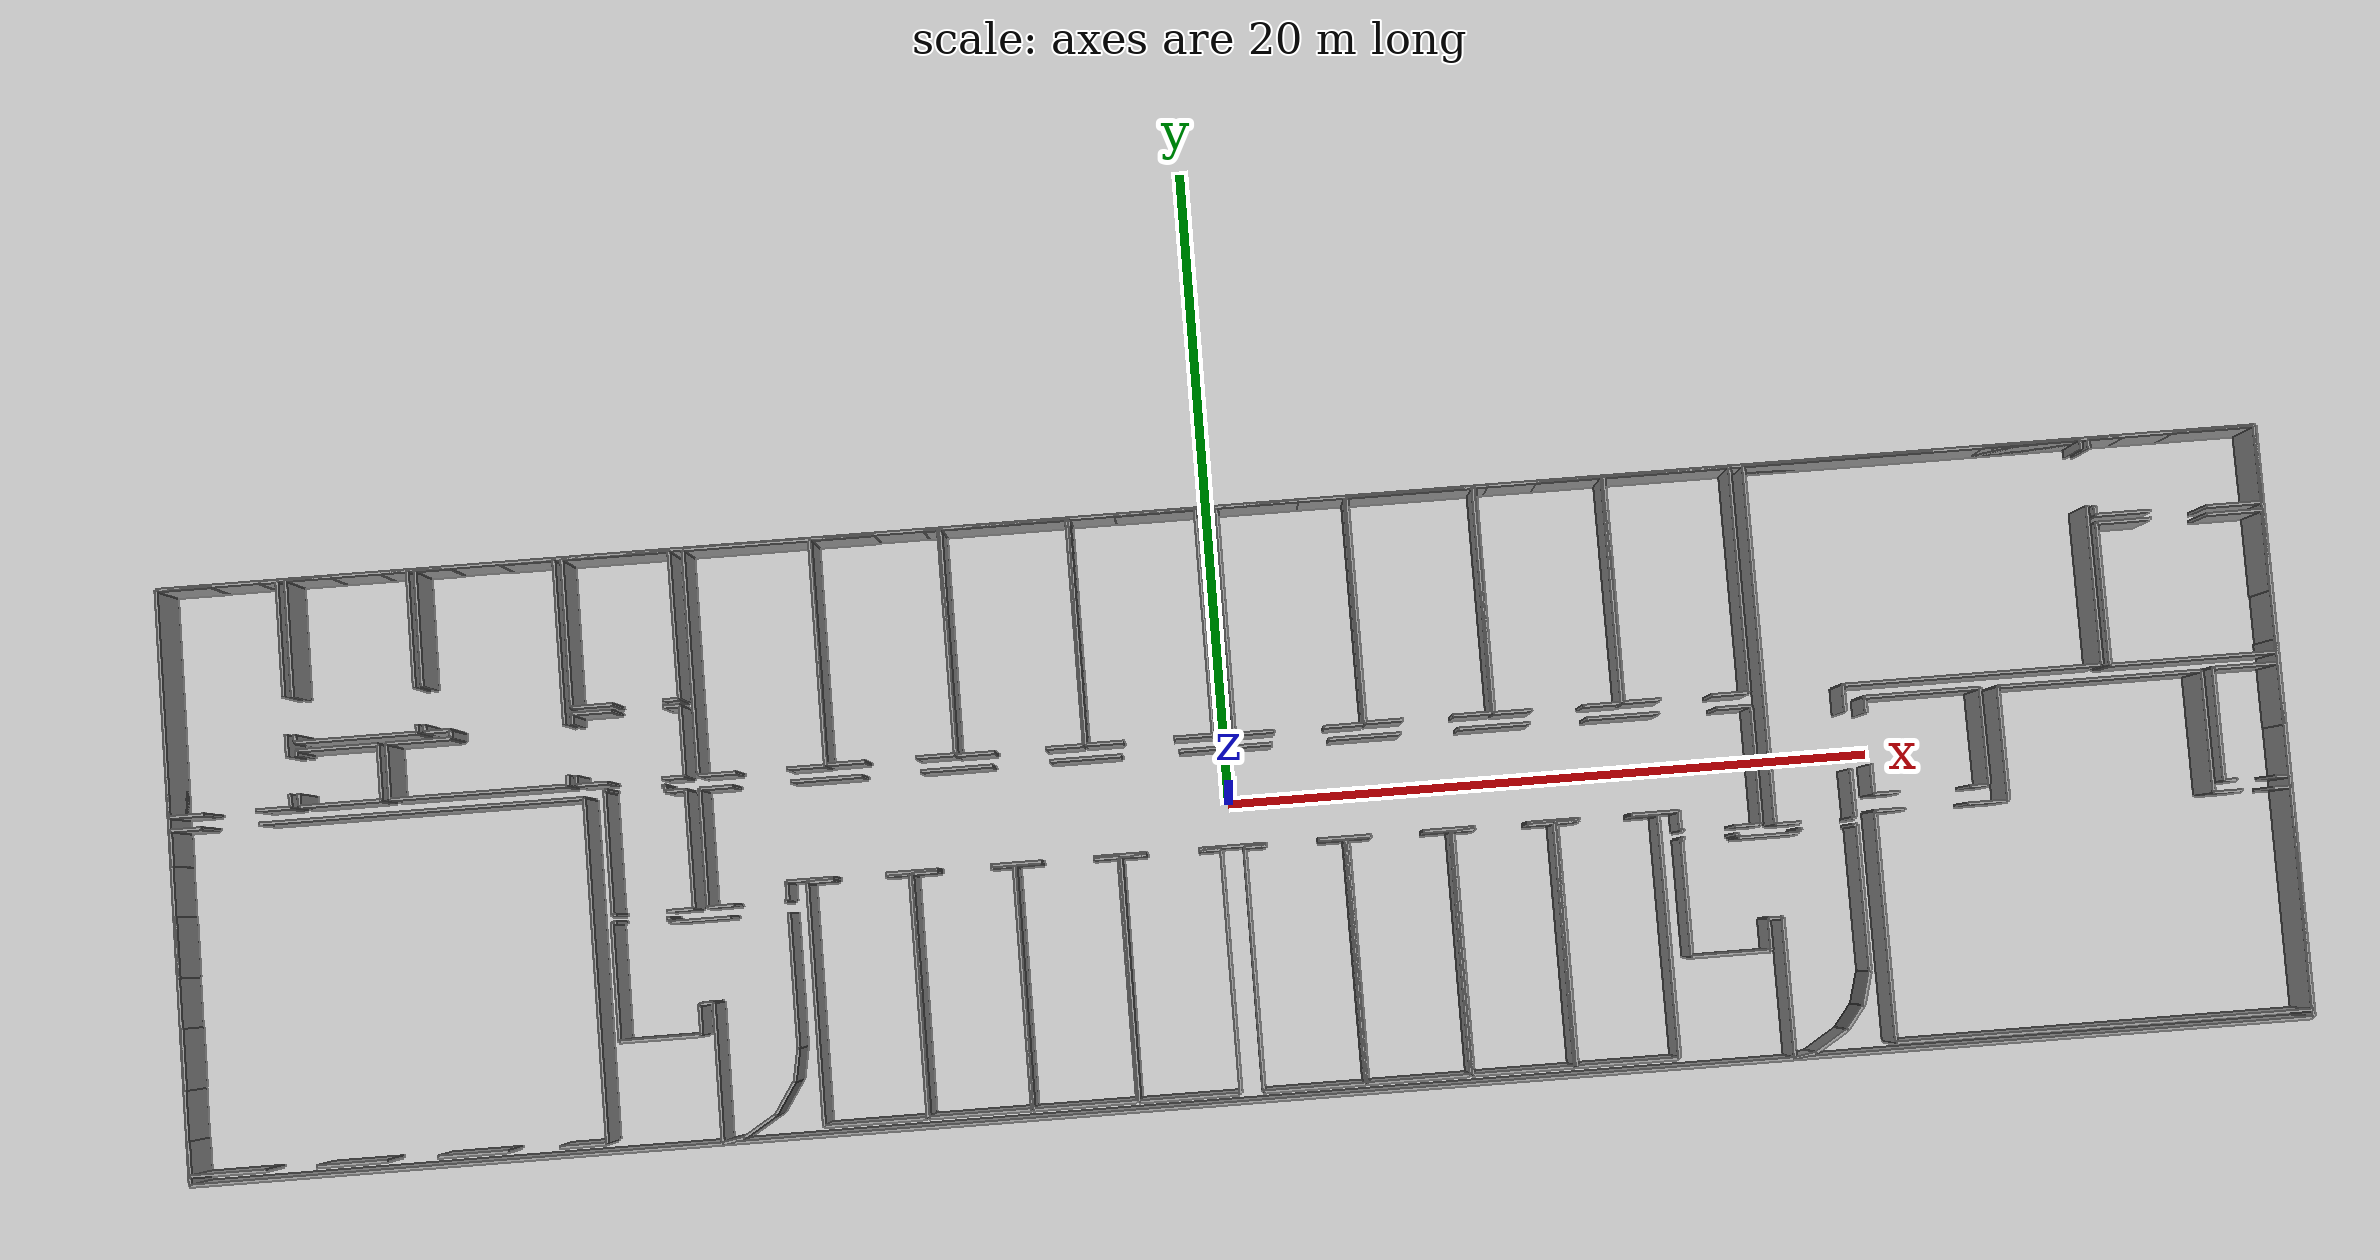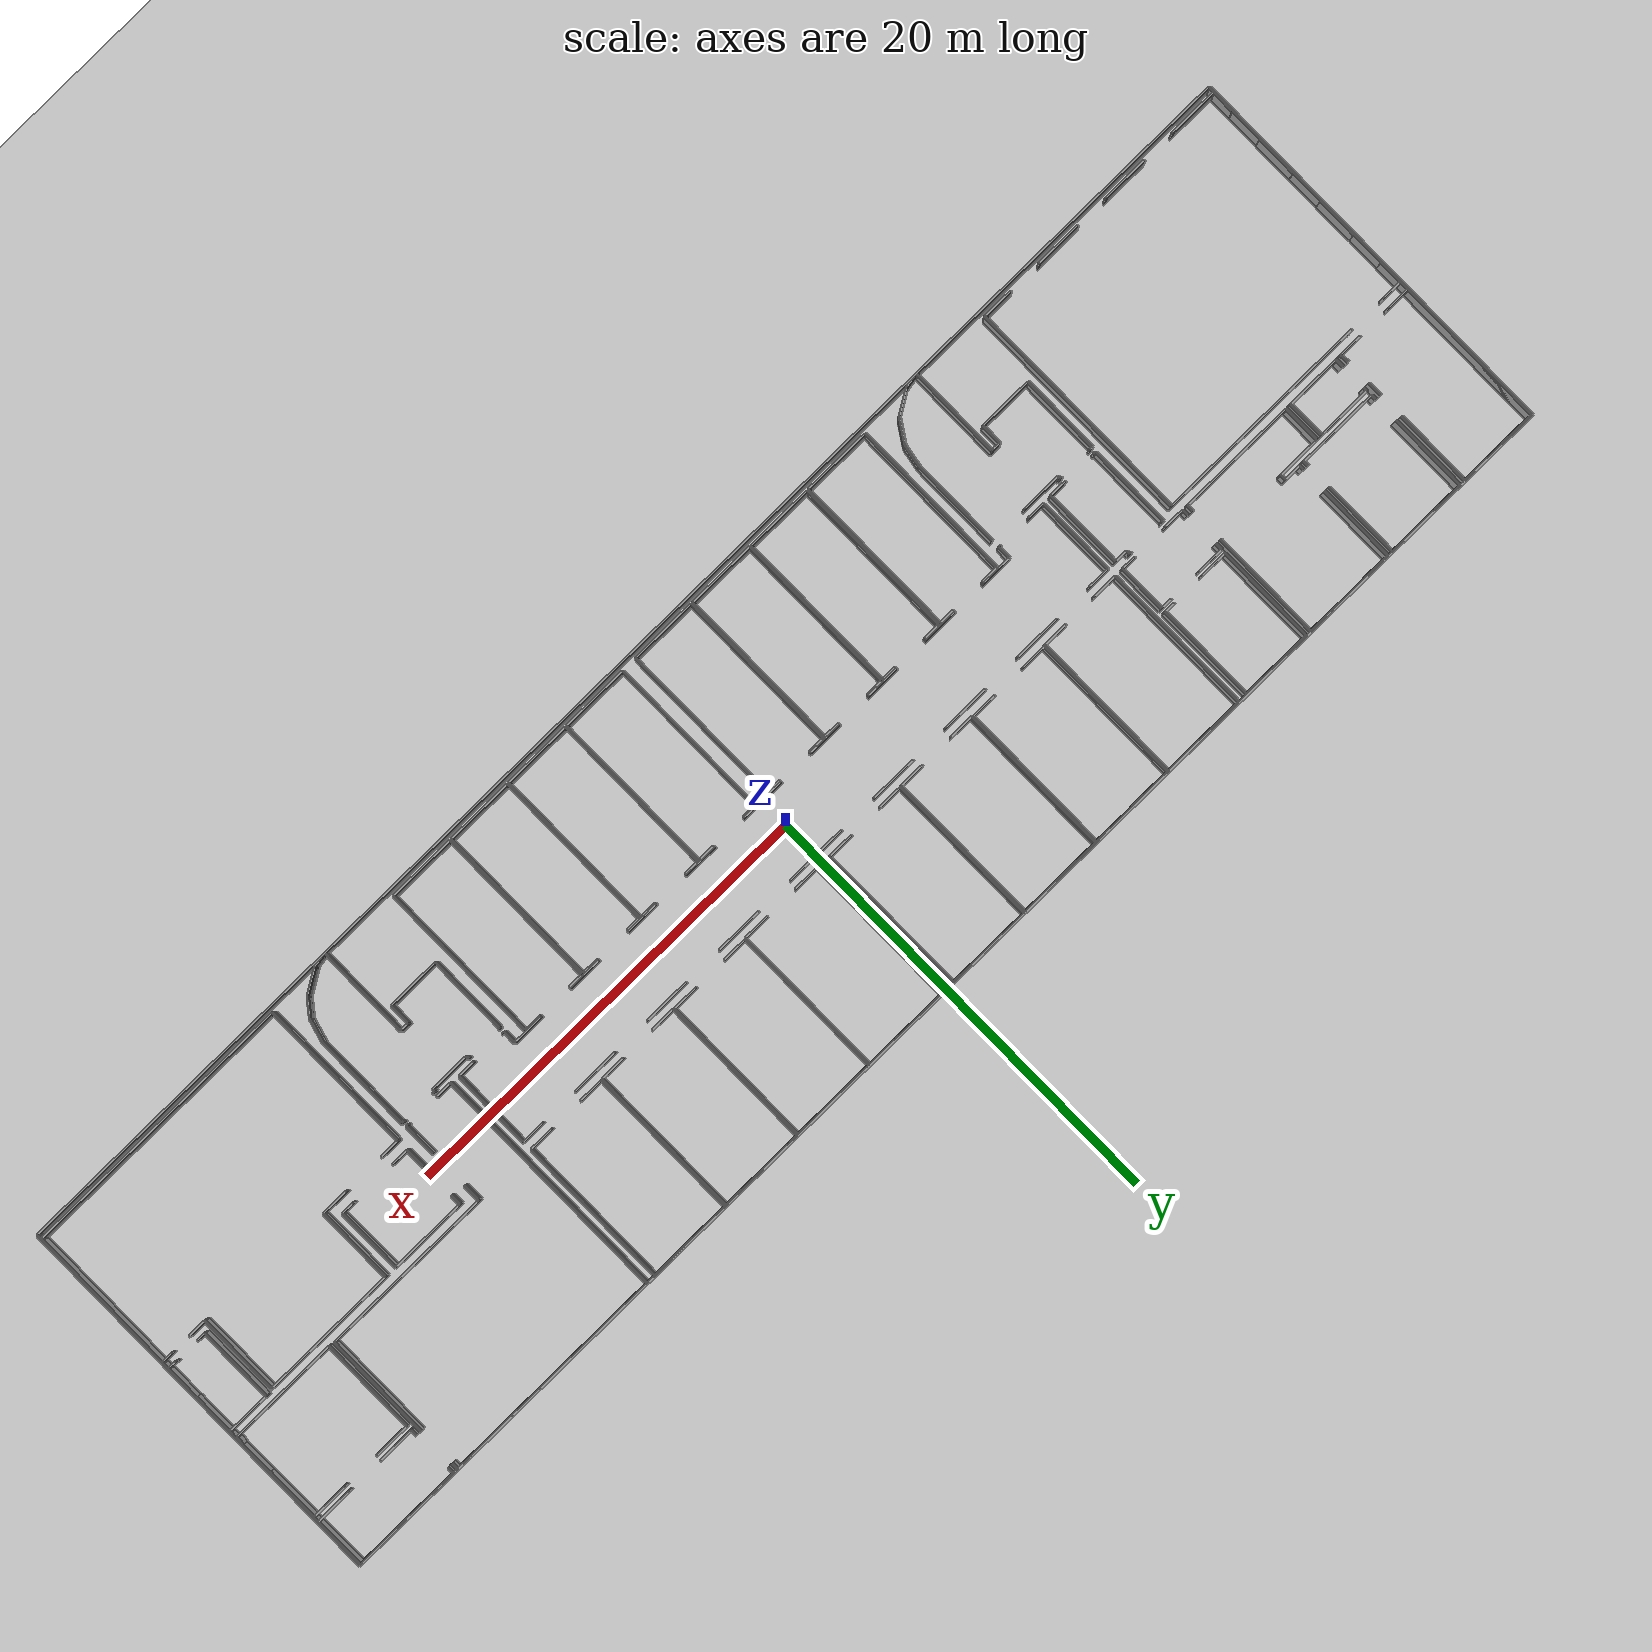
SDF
<sdf version="1.6">
  <world name="default">
    <light name="sun" type="directional">
      <cast_shadows>1</cast_shadows>
      <pose frame="">0 0 10 0 -0 0</pose>
      <diffuse>0.8 0.8 0.8 1</diffuse>
      <specular>0.1 0.1 0.1 1</specular>
      <attenuation>
        <range>1000</range>
        <constant>0.9</constant>
        <linear>0.01</linear>
        <quadratic>0.001</quadratic>
      </attenuation>
      <direction>-0.5 0.5 -1</direction>
    </light>
    <model name="ground_plane">
      <static>1</static>
      <link name="link">
        <collision name="collision">
          <geometry>
            <plane>
              <normal>0 0 1</normal>
              <size>100 100</size>
            </plane>
          </geometry>
          <surface>
            <friction>
              <ode>
                <mu>100</mu>
                <mu2>50</mu2>
              </ode>
              <torsional>
                <ode />
              </torsional>
            </friction>
            <contact>
              <ode />
            </contact>
            <bounce />
          </surface>
          <max_contacts>10</max_contacts>
        </collision>
        <visual name="visual">
          <cast_shadows>0</cast_shadows>
          <geometry>
            <plane>
              <normal>0 0 1</normal>
              <size>100 100</size>
            </plane>
          </geometry>
          <material>
            <script>
              <uri>file://media/materials/scripts/gazebo.material</uri>
              <name>Gazebo/Grey</name>
            </script>
          </material>
        </visual>
        <self_collide>0</self_collide>
        <kinematic>0</kinematic>
        <gravity>1</gravity>
      </link>
    </model>
    <gravity>0 0 -9.8</gravity>
    <magnetic_field>6e-06 2.3e-05 -4.2e-05</magnetic_field>
    <atmosphere type="adiabatic" />
    <physics default="0" name="default_physics" type="ode">
      <max_step_size>0.001</max_step_size>
      <real_time_factor>1</real_time_factor>
      <real_time_update_rate>1000</real_time_update_rate>
    </physics>
    <scene>
      <ambient>0.4 0.4 0.4 1</ambient>
      <background>0.7 0.7 0.7 1</background>
      <shadows>1</shadows>
    </scene>
    <spherical_coordinates>
      <surface_model>EARTH_WGS84</surface_model>
      <latitude_deg>0</latitude_deg>
      <longitude_deg>0</longitude_deg>
      <elevation>0</elevation>
      <heading_deg>0</heading_deg>
    </spherical_coordinates>
  <model name="0510034839_A-40">
		<static>1</static>
		<link name="Wall_0">
			<collision name="Wall_0_Collision">
				<geometry>
					<box>
						<size>1.09109604692 0.1 2.5</size>
					</box>
				</geometry>
				<pose frame="">0.54554802346 0 1.25 0 0 0</pose>
			</collision>
			<visual name="Wall_0_Visual">
				<pose frame="">0.54554802346 0 1.25 0 0 0</pose>
				<geometry>
					<box>
						<size>1.09109604692 0.1 2.5</size>
					</box>
				</geometry>
				<material>
					<script>
						<uri>file://media/materials/scripts/gazebo.material</uri>
						<name>Gazebo/Grey</name>
					</script>
					<ambient>1 1 1 1</ambient>
				</material>
			</visual>
			<pose frame="">3.7589813898 -7.01970193211 0 0 0 3.14159265359</pose>
		</link>
		<link name="Wall_1">
			<collision name="Wall_1_Collision">
				<geometry>
					<box>
						<size>1.08144819357 0.1 2.5</size>
					</box>
				</geometry>
				<pose frame="">0.540724096783 0 1.25 0 0 0</pose>
			</collision>
			<visual name="Wall_1_Visual">
				<pose frame="">0.540724096783 0 1.25 0 0 0</pose>
				<geometry>
					<box>
						<size>1.08144819357 0.1 2.5</size>
					</box>
				</geometry>
				<material>
					<script>
						<uri>file://media/materials/scripts/gazebo.material</uri>
						<name>Gazebo/Grey</name>
					</script>
					<ambient>1 1 1 1</ambient>
				</material>
			</visual>
			<pose frame="">1.08144819357 -7.01970193211 0 0 0 3.14159265359</pose>
		</link>
		<link name="Wall_2">
			<collision name="Wall_2_Collision">
				<geometry>
					<box>
						<size>7.00865767893 0.1 2.5</size>
					</box>
				</geometry>
				<pose frame="">3.50432883946 0 1.25 0 0 0</pose>
			</collision>
			<visual name="Wall_2_Visual">
				<pose frame="">3.50432883946 0 1.25 0 0 0</pose>
				<geometry>
					<box>
						<size>7.00865767893 0.1 2.5</size>
					</box>
				</geometry>
				<material>
					<script>
						<uri>file://media/materials/scripts/gazebo.material</uri>
						<name>Gazebo/Grey</name>
					</script>
					<ambient>1 1 1 1</ambient>
				</material>
			</visual>
			<pose frame="">0.0 -7.01970193211 0 0 0 1.57079632679</pose>
		</link>
		<link name="Wall_3">
			<collision name="Wall_3_Collision">
				<geometry>
					<box>
						<size>1.69116713636 0.1 2.5</size>
					</box>
				</geometry>
				<pose frame="">0.845583568182 0 1.25 0 0 0</pose>
			</collision>
			<visual name="Wall_3_Visual">
				<pose frame="">0.845583568182 0 1.25 0 0 0</pose>
				<geometry>
					<box>
						<size>1.69116713636 0.1 2.5</size>
					</box>
				</geometry>
				<material>
					<script>
						<uri>file://media/materials/scripts/gazebo.material</uri>
						<name>Gazebo/Grey</name>
					</script>
					<ambient>1 1 1 1</ambient>
				</material>
			</visual>
			<pose frame="">0.0 -0.01104425318 0 0 0 0.0</pose>
		</link>
		<link name="Wall_4">
			<collision name="Wall_4_Collision">
				<geometry>
					<box>
						<size>0.53444029756 0.1 2.5</size>
					</box>
				</geometry>
				<pose frame="">0.26722014878 0 1.25 0 0 0</pose>
			</collision>
			<visual name="Wall_4_Visual">
				<pose frame="">0.26722014878 0 1.25 0 0 0</pose>
				<geometry>
					<box>
						<size>0.53444029756 0.1 2.5</size>
					</box>
				</geometry>
				<material>
					<script>
						<uri>file://media/materials/scripts/gazebo.material</uri>
						<name>Gazebo/Grey</name>
					</script>
					<ambient>1 1 1 1</ambient>
				</material>
			</visual>
			<pose frame="">3.19775560464 -0.01104425318 0 0 0 0.0</pose>
		</link>
		<link name="Wall_5">
			<collision name="Wall_5_Collision">
				<geometry>
					<box>
						<size>3.59141341052 0.1 2.5</size>
					</box>
				</geometry>
				<pose frame="">1.79570670526 0 1.25 0 0 0</pose>
			</collision>
			<visual name="Wall_5_Visual">
				<pose frame="">1.79570670526 0 1.25 0 0 0</pose>
				<geometry>
					<box>
						<size>3.59141341052 0.1 2.5</size>
					</box>
				</geometry>
				<material>
					<script>
						<uri>file://media/materials/scripts/gazebo.material</uri>
						<name>Gazebo/Grey</name>
					</script>
					<ambient>1 1 1 1</ambient>
				</material>
			</visual>
			<pose frame="">3.7321959022 -0.01104425318 0 0 0 -1.57079632679</pose>
		</link>
		<link name="Wall_6">
			<collision name="Wall_6_Collision">
				<geometry>
					<box>
						<size>0.691598750857 0.1 2.5</size>
					</box>
				</geometry>
				<pose frame="">0.345799375428 0 1.25 0 0 0</pose>
			</collision>
			<visual name="Wall_6_Visual">
				<pose frame="">0.345799375428 0 1.25 0 0 0</pose>
				<geometry>
					<box>
						<size>0.691598750857 0.1 2.5</size>
					</box>
				</geometry>
				<material>
					<script>
						<uri>file://media/materials/scripts/gazebo.material</uri>
						<name>Gazebo/Grey</name>
					</script>
					<ambient>1 1 1 1</ambient>
				</material>
			</visual>
			<pose frame="">3.7321959022 -4.76845151954 0 0 0 -1.57079632679</pose>
		</link>
		<link name="Wall_7">
			<collision name="Wall_7_Collision">
				<geometry>
					<box>
						<size>0.419015281077 0.1 2.5</size>
					</box>
				</geometry>
				<pose frame="">0.209507640539 0 1.25 0 0 0</pose>
			</collision>
			<visual name="Wall_7_Visual">
				<pose frame="">0.209507640539 0 1.25 0 0 0</pose>
				<geometry>
					<box>
						<size>0.419015281077 0.1 2.5</size>
					</box>
				</geometry>
				<material>
					<script>
						<uri>file://media/materials/scripts/gazebo.material</uri>
						<name>Gazebo/Grey</name>
					</script>
					<ambient>1 1 1 1</ambient>
				</material>
			</visual>
			<pose frame="">3.7321959022 -6.60154365654 0 0 0 -1.50682786293</pose>
		</link>
		<link name="Wall_8">
			<collision name="Wall_8_Collision">
				<geometry>
					<box>
						<size>3.77281844263 0.1 2.5</size>
					</box>
				</geometry>
				<pose frame="">1.88640922132 0 1.25 0 0 0</pose>
			</collision>
			<visual name="Wall_8_Visual">
				<pose frame="">1.88640922132 0 1.25 0 0 0</pose>
				<geometry>
					<box>
						<size>3.77281844263 0.1 2.5</size>
					</box>
				</geometry>
				<material>
					<script>
						<uri>file://media/materials/scripts/gazebo.material</uri>
						<name>Gazebo/Grey</name>
					</script>
					<ambient>1 1 1 1</ambient>
				</material>
			</visual>
			<pose frame="">7.77096503923 -5.0267854876 0 0 0 3.14159265359</pose>
		</link>
		<link name="Wall_9">
			<collision name="Wall_9_Collision">
				<geometry>
					<box>
						<size>0.233706552924 0.1 2.5</size>
					</box>
				</geometry>
				<pose frame="">0.116853276462 0 1.25 0 0 0</pose>
			</collision>
			<visual name="Wall_9_Visual">
				<pose frame="">0.116853276462 0 1.25 0 0 0</pose>
				<geometry>
					<box>
						<size>0.233706552924 0.1 2.5</size>
					</box>
				</geometry>
				<material>
					<script>
						<uri>file://media/materials/scripts/gazebo.material</uri>
						<name>Gazebo/Grey</name>
					</script>
					<ambient>1 1 1 1</ambient>
				</material>
			</visual>
			<pose frame="">3.99814659659 -5.0267854876 0 0 0 1.57079632679</pose>
		</link>
		<link name="Wall_10">
			<collision name="Wall_10_Collision">
				<geometry>
					<box>
						<size>3.62848147866 0.1 2.5</size>
					</box>
				</geometry>
				<pose frame="">1.81424073933 0 1.25 0 0 0</pose>
			</collision>
			<visual name="Wall_10_Visual">
				<pose frame="">1.81424073933 0 1.25 0 0 0</pose>
				<geometry>
					<box>
						<size>3.62848147866 0.1 2.5</size>
					</box>
				</geometry>
				<material>
					<script>
						<uri>file://media/materials/scripts/gazebo.material</uri>
						<name>Gazebo/Grey</name>
					</script>
					<ambient>1 1 1 1</ambient>
				</material>
			</visual>
			<pose frame="">3.99814659659 -3.63127427832 0 0 0 1.57079632679</pose>
		</link>
		<link name="Wall_11">
			<collision name="Wall_11_Collision">
				<geometry>
					<box>
						<size>1.40922131668 0.1 2.5</size>
					</box>
				</geometry>
				<pose frame="">0.704610658339 0 1.25 0 0 0</pose>
			</collision>
			<visual name="Wall_11_Visual">
				<pose frame="">0.704610658339 0 1.25 0 0 0</pose>
				<geometry>
					<box>
						<size>1.40922131668 0.1 2.5</size>
					</box>
				</geometry>
				<material>
					<script>
						<uri>file://media/materials/scripts/gazebo.material</uri>
						<name>Gazebo/Grey</name>
					</script>
					<ambient>1 1 1 1</ambient>
				</material>
			</visual>
			<pose frame="">3.99814659659 -0.00279279965471 0 0 0 0.0</pose>
		</link>
		<link name="Wall_12">
			<collision name="Wall_12_Collision">
				<geometry>
					<box>
						<size>0.842029095895 0.1 2.5</size>
					</box>
				</geometry>
				<pose frame="">0.421014547947 0 1.25 0 0 0</pose>
			</collision>
			<visual name="Wall_12_Visual">
				<pose frame="">0.421014547947 0 1.25 0 0 0</pose>
				<geometry>
					<box>
						<size>0.842029095895 0.1 2.5</size>
					</box>
				</geometry>
				<material>
					<script>
						<uri>file://media/materials/scripts/gazebo.material</uri>
						<name>Gazebo/Grey</name>
					</script>
					<ambient>1 1 1 1</ambient>
				</material>
			</visual>
			<pose frame="">6.91700307208 -0.00279279965471 0 0 0 0.0</pose>
		</link>
		<link name="Wall_13">
			<collision name="Wall_13_Collision">
				<geometry>
					<box>
						<size>3.63013176937 0.1 2.5</size>
					</box>
				</geometry>
				<pose frame="">1.81506588468 0 1.25 0 0 0</pose>
			</collision>
			<visual name="Wall_13_Visual">
				<pose frame="">1.81506588468 0 1.25 0 0 0</pose>
				<geometry>
					<box>
						<size>3.63013176937 0.1 2.5</size>
					</box>
				</geometry>
				<material>
					<script>
						<uri>file://media/materials/scripts/gazebo.material</uri>
						<name>Gazebo/Grey</name>
					</script>
					<ambient>1 1 1 1</ambient>
				</material>
			</visual>
			<pose frame="">7.75903216797 -0.00279279965471 0 0 0 -1.57079632679</pose>
		</link>
		<link name="Wall_14">
			<collision name="Wall_14_Collision">
				<geometry>
					<box>
						<size>0.258609420691 0.1 2.5</size>
					</box>
				</geometry>
				<pose frame="">0.129304710346 0 1.25 0 0 0</pose>
			</collision>
			<visual name="Wall_14_Visual">
				<pose frame="">0.129304710346 0 1.25 0 0 0</pose>
				<geometry>
					<box>
						<size>0.258609420691 0.1 2.5</size>
					</box>
				</geometry>
				<material>
					<script>
						<uri>file://media/materials/scripts/gazebo.material</uri>
						<name>Gazebo/Grey</name>
					</script>
					<ambient>1 1 1 1</ambient>
				</material>
			</visual>
			<pose frame="">7.75903216797 -4.76845151954 0 0 0 -1.52463749116</pose>
		</link>
		<link name="Wall_15">
			<collision name="Wall_15_Collision">
				<geometry>
					<box>
						<size>2.52304059715 0.1 2.5</size>
					</box>
				</geometry>
				<pose frame="">1.26152029858 0 1.25 0 0 0</pose>
			</collision>
			<visual name="Wall_15_Visual">
				<pose frame="">1.26152029858 0 1.25 0 0 0</pose>
				<geometry>
					<box>
						<size>2.52304059715 0.1 2.5</size>
					</box>
				</geometry>
				<material>
					<script>
						<uri>file://media/materials/scripts/gazebo.material</uri>
						<name>Gazebo/Grey</name>
					</script>
					<ambient>1 1 1 1</ambient>
				</material>
			</visual>
			<pose frame="">6.53730926448 -7.01259298753 0 0 0 3.14159265359</pose>
		</link>
		<link name="Wall_16">
			<collision name="Wall_16_Collision">
				<geometry>
					<box>
						<size>0.398354787113 0.1 2.5</size>
					</box>
				</geometry>
				<pose frame="">0.199177393556 0 1.25 0 0 0</pose>
			</collision>
			<visual name="Wall_16_Visual">
				<pose frame="">0.199177393556 0 1.25 0 0 0</pose>
				<geometry>
					<box>
						<size>0.398354787113 0.1 2.5</size>
					</box>
				</geometry>
				<material>
					<script>
						<uri>file://media/materials/scripts/gazebo.material</uri>
						<name>Gazebo/Grey</name>
					</script>
					<ambient>1 1 1 1</ambient>
				</material>
			</visual>
			<pose frame="">4.01426866733 -7.01259298753 0 0 0 1.57079632679</pose>
		</link>
		<link name="Wall_17">
			<collision name="Wall_17_Collision">
				<geometry>
					<box>
						<size>0.17010688806 0.1 2.5</size>
					</box>
				</geometry>
				<pose frame="">0.0850534440298 0 1.25 0 0 0</pose>
			</collision>
			<visual name="Wall_17_Visual">
				<pose frame="">0.0850534440298 0 1.25 0 0 0</pose>
				<geometry>
					<box>
						<size>0.17010688806 0.1 2.5</size>
					</box>
				</geometry>
				<material>
					<script>
						<uri>file://media/materials/scripts/gazebo.material</uri>
						<name>Gazebo/Grey</name>
					</script>
					<ambient>1 1 1 1</ambient>
				</material>
			</visual>
			<pose frame="">4.01426866733 -5.45446467108 0 0 0 1.57079632679</pose>
		</link>
		<link name="Wall_18">
			<collision name="Wall_18_Collision">
				<geometry>
					<box>
						<size>2.51643943433 0.1 2.5</size>
					</box>
				</geometry>
				<pose frame="">1.25821971717 0 1.25 0 0 0</pose>
			</collision>
			<visual name="Wall_18_Visual">
				<pose frame="">1.25821971717 0 1.25 0 0 0</pose>
				<geometry>
					<box>
						<size>2.51643943433 0.1 2.5</size>
					</box>
				</geometry>
				<material>
					<script>
						<uri>file://media/materials/scripts/gazebo.material</uri>
						<name>Gazebo/Grey</name>
					</script>
					<ambient>1 1 1 1</ambient>
				</material>
			</visual>
			<pose frame="">4.01426866733 -5.28435778302 0 0 0 0.0</pose>
		</link>
		<link name="Wall_19">
			<collision name="Wall_19_Collision">
				<geometry>
					<box>
						<size>1.72824781136 0.1 2.5</size>
					</box>
				</geometry>
				<pose frame="">0.864123905678 0 1.25 0 0 0</pose>
			</collision>
			<visual name="Wall_19_Visual">
				<pose frame="">0.864123905678 0 1.25 0 0 0</pose>
				<geometry>
					<box>
						<size>1.72824781136 0.1 2.5</size>
					</box>
				</geometry>
				<material>
					<script>
						<uri>file://media/materials/scripts/gazebo.material</uri>
						<name>Gazebo/Grey</name>
					</script>
					<ambient>1 1 1 1</ambient>
				</material>
			</visual>
			<pose frame="">6.53070810166 -5.28435778302 0 0 0 -1.5669767479</pose>
		</link>
		<link name="Wall_20">
			<collision name="Wall_20_Collision">
				<geometry>
					<box>
						<size>1.45162109325 0.1 2.5</size>
					</box>
				</geometry>
				<pose frame="">0.725810546627 0 1.25 0 0 0</pose>
			</collision>
			<visual name="Wall_20_Visual">
				<pose frame="">0.725810546627 0 1.25 0 0 0</pose>
				<geometry>
					<box>
						<size>1.45162109325 0.1 2.5</size>
					</box>
				</geometry>
				<material>
					<script>
						<uri>file://media/materials/scripts/gazebo.material</uri>
						<name>Gazebo/Grey</name>
					</script>
					<ambient>1 1 1 1</ambient>
				</material>
			</visual>
			<pose frame="">12.7597938406 -17.9983243202 0 0 0 3.14159265359</pose>
		</link>
		<link name="Wall_21">
			<collision name="Wall_21_Collision">
				<geometry>
					<box>
						<size>2.18092263945 0.1 2.5</size>
					</box>
				</geometry>
				<pose frame="">1.09046131972 0 1.25 0 0 0</pose>
			</collision>
			<visual name="Wall_21_Visual">
				<pose frame="">1.09046131972 0 1.25 0 0 0</pose>
				<geometry>
					<box>
						<size>2.18092263945 0.1 2.5</size>
					</box>
				</geometry>
				<material>
					<script>
						<uri>file://media/materials/scripts/gazebo.material</uri>
						<name>Gazebo/Grey</name>
					</script>
					<ambient>1 1 1 1</ambient>
				</material>
			</visual>
			<pose frame="">9.75969228426 -17.9983243202 0 0 0 3.14159265359</pose>
		</link>
		<link name="Wall_22">
			<collision name="Wall_22_Collision">
				<geometry>
					<box>
						<size>2.17432147663 0.1 2.5</size>
					</box>
				</geometry>
				<pose frame="">1.08716073831 0 1.25 0 0 0</pose>
			</collision>
			<visual name="Wall_22_Visual">
				<pose frame="">1.08716073831 0 1.25 0 0 0</pose>
				<geometry>
					<box>
						<size>2.17432147663 0.1 2.5</size>
					</box>
				</geometry>
				<material>
					<script>
						<uri>file://media/materials/scripts/gazebo.material</uri>
						<name>Gazebo/Grey</name>
					</script>
					<ambient>1 1 1 1</ambient>
				</material>
			</visual>
			<pose frame="">6.05161601544 -17.9983243202 0 0 0 3.14159265359</pose>
		</link>
		<link name="Wall_23">
			<collision name="Wall_23_Collision">
				<geometry>
					<box>
						<size>2.3238632036 0.1 2.5</size>
					</box>
				</geometry>
				<pose frame="">1.1619316018 0 1.25 0 0 0</pose>
			</collision>
			<visual name="Wall_23_Visual">
				<pose frame="">1.1619316018 0 1.25 0 0 0</pose>
				<geometry>
					<box>
						<size>2.3238632036 0.1 2.5</size>
					</box>
				</geometry>
				<material>
					<script>
						<uri>file://media/materials/scripts/gazebo.material</uri>
						<name>Gazebo/Grey</name>
					</script>
					<ambient>1 1 1 1</ambient>
				</material>
			</visual>
			<pose frame="">2.34176251047 -17.9983243202 0 0 0 3.14159265359</pose>
		</link>
		<link name="Wall_24">
			<collision name="Wall_24_Collision">
				<geometry>
					<box>
						<size>1.06761114073 0.1 2.5</size>
					</box>
				</geometry>
				<pose frame="">0.533805570366 0 1.25 0 0 0</pose>
			</collision>
			<visual name="Wall_24_Visual">
				<pose frame="">0.533805570366 0 1.25 0 0 0</pose>
				<geometry>
					<box>
						<size>1.06761114073 0.1 2.5</size>
					</box>
				</geometry>
				<material>
					<script>
						<uri>file://media/materials/scripts/gazebo.material</uri>
						<name>Gazebo/Grey</name>
					</script>
					<ambient>1 1 1 1</ambient>
				</material>
			</visual>
			<pose frame="">0.0178993068779 -17.9983243202 0 0 0 1.57079632679</pose>
		</link>
		<link name="Wall_25">
			<collision name="Wall_25_Collision">
				<geometry>
					<box>
						<size>1.8922487115 0.1 2.5</size>
					</box>
				</geometry>
				<pose frame="">0.946124355752 0 1.25 0 0 0</pose>
			</collision>
			<visual name="Wall_25_Visual">
				<pose frame="">0.946124355752 0 1.25 0 0 0</pose>
				<geometry>
					<box>
						<size>1.8922487115 0.1 2.5</size>
					</box>
				</geometry>
				<material>
					<script>
						<uri>file://media/materials/scripts/gazebo.material</uri>
						<name>Gazebo/Grey</name>
					</script>
					<ambient>1 1 1 1</ambient>
				</material>
			</visual>
			<pose frame="">0.0178993068779 -15.3911188971 0 0 0 1.57079632679</pose>
		</link>
		<link name="Wall_26">
			<collision name="Wall_26_Collision">
				<geometry>
					<box>
						<size>1.88742478483 0.1 2.5</size>
					</box>
				</geometry>
				<pose frame="">0.943712392414 0 1.25 0 0 0</pose>
			</collision>
			<visual name="Wall_26_Visual">
				<pose frame="">0.943712392414 0 1.25 0 0 0</pose>
				<geometry>
					<box>
						<size>1.88742478483 0.1 2.5</size>
					</box>
				</geometry>
				<material>
					<script>
						<uri>file://media/materials/scripts/gazebo.material</uri>
						<name>Gazebo/Grey</name>
					</script>
					<ambient>1 1 1 1</ambient>
				</material>
			</visual>
			<pose frame="">0.0178993068779 -11.9582603397 0 0 0 1.57079632679</pose>
		</link>
		<link name="Wall_27">
			<collision name="Wall_27_Collision">
				<geometry>
					<box>
						<size>1.0890649199 0.1 2.5</size>
					</box>
				</geometry>
				<pose frame="">0.544532459949 0 1.25 0 0 0</pose>
			</collision>
			<visual name="Wall_27_Visual">
				<pose frame="">0.544532459949 0 1.25 0 0 0</pose>
				<geometry>
					<box>
						<size>1.0890649199 0.1 2.5</size>
					</box>
				</geometry>
				<material>
					<script>
						<uri>file://media/materials/scripts/gazebo.material</uri>
						<name>Gazebo/Grey</name>
					</script>
					<ambient>1 1 1 1</ambient>
				</material>
			</visual>
			<pose frame="">0.0178993068779 -8.52489400056 0 0 0 1.57079632679</pose>
		</link>
		<link name="Wall_28">
			<collision name="Wall_28_Collision">
				<geometry>
					<box>
						<size>0.954502754716 0.1 2.5</size>
					</box>
				</geometry>
				<pose frame="">0.477251377358 0 1.25 0 0 0</pose>
			</collision>
			<visual name="Wall_28_Visual">
				<pose frame="">0.477251377358 0 1.25 0 0 0</pose>
				<geometry>
					<box>
						<size>0.954502754716 0.1 2.5</size>
					</box>
				</geometry>
				<material>
					<script>
						<uri>file://media/materials/scripts/gazebo.material</uri>
						<name>Gazebo/Grey</name>
					</script>
					<ambient>1 1 1 1</ambient>
				</material>
			</visual>
			<pose frame="">0.0178993068779 -7.43582908066 0 0 0 0.0</pose>
		</link>
		<link name="Wall_29">
			<collision name="Wall_29_Collision">
				<geometry>
					<box>
						<size>10.0184070886 0.1 2.5</size>
					</box>
				</geometry>
				<pose frame="">5.00920354432 0 1.25 0 0 0</pose>
			</collision>
			<visual name="Wall_29_Visual">
				<pose frame="">5.00920354432 0 1.25 0 0 0</pose>
				<geometry>
					<box>
						<size>10.0184070886 0.1 2.5</size>
					</box>
				</geometry>
				<material>
					<script>
						<uri>file://media/materials/scripts/gazebo.material</uri>
						<name>Gazebo/Grey</name>
					</script>
					<ambient>1 1 1 1</ambient>
				</material>
			</visual>
			<pose frame="">2.72907304441 -7.43582908066 0 0 0 0.0</pose>
		</link>
		<link name="Wall_30">
			<collision name="Wall_30_Collision">
				<geometry>
					<box>
						<size>10.5625024172 0.1 2.5</size>
					</box>
				</geometry>
				<pose frame="">5.28125120859 0 1.25 0 0 0</pose>
			</collision>
			<visual name="Wall_30_Visual">
				<pose frame="">5.28125120859 0 1.25 0 0 0</pose>
				<geometry>
					<box>
						<size>10.5625024172 0.1 2.5</size>
					</box>
				</geometry>
				<material>
					<script>
						<uri>file://media/materials/scripts/gazebo.material</uri>
						<name>Gazebo/Grey</name>
					</script>
					<ambient>1 1 1 1</ambient>
				</material>
			</visual>
			<pose frame="">12.747480133 -7.43582908066 0 0 0 -1.569630532</pose>
		</link>
		<link name="Wall_31">
			<collision name="Wall_31_Collision">
				<geometry>
					<box>
						<size>5.48455074009 0.1 2.5</size>
					</box>
				</geometry>
				<pose frame="">2.74227537005 0 1.25 0 0 0</pose>
			</collision>
			<visual name="Wall_31_Visual">
				<pose frame="">2.74227537005 0 1.25 0 0 0</pose>
				<geometry>
					<box>
						<size>5.48455074009 0.1 2.5</size>
					</box>
				</geometry>
				<material>
					<script>
						<uri>file://media/materials/scripts/gazebo.material</uri>
						<name>Gazebo/Grey</name>
					</script>
					<ambient>1 1 1 1</ambient>
				</material>
			</visual>
			<pose frame="">12.2738467007 -7.0101810242 0 0 0 3.14159265359</pose>
		</link>
		<link name="Wall_32">
			<collision name="Wall_32_Collision">
				<geometry>
					<box>
						<size>1.72937771346 0.1 2.5</size>
					</box>
				</geometry>
				<pose frame="">0.864688856729 0 1.25 0 0 0</pose>
			</collision>
			<visual name="Wall_32_Visual">
				<pose frame="">0.864688856729 0 1.25 0 0 0</pose>
				<geometry>
					<box>
						<size>1.72937771346 0.1 2.5</size>
					</box>
				</geometry>
				<material>
					<script>
						<uri>file://media/materials/scripts/gazebo.material</uri>
						<name>Gazebo/Grey</name>
					</script>
					<ambient>1 1 1 1</ambient>
				</material>
			</visual>
			<pose frame="">6.7892959606 -7.0101810242 0 0 0 1.57079632679</pose>
		</link>
		<link name="Wall_33">
			<collision name="Wall_33_Collision">
				<geometry>
					<box>
						<size>2.00066011628 0.1 2.5</size>
					</box>
				</geometry>
				<pose frame="">1.00033005814 0 1.25 0 0 0</pose>
			</collision>
			<visual name="Wall_33_Visual">
				<pose frame="">1.00033005814 0 1.25 0 0 0</pose>
				<geometry>
					<box>
						<size>2.00066011628 0.1 2.5</size>
					</box>
				</geometry>
				<material>
					<script>
						<uri>file://media/materials/scripts/gazebo.material</uri>
						<name>Gazebo/Grey</name>
					</script>
					<ambient>1 1 1 1</ambient>
				</material>
			</visual>
			<pose frame="">6.7892959606 -5.28080331074 0 0 0 0.0</pose>
		</link>
		<link name="Wall_34">
			<collision name="Wall_34_Collision">
				<geometry>
					<box>
						<size>0.252494477873 0.1 2.5</size>
					</box>
				</geometry>
				<pose frame="">0.126247238937 0 1.25 0 0 0</pose>
			</collision>
			<visual name="Wall_34_Visual">
				<pose frame="">0.126247238937 0 1.25 0 0 0</pose>
				<geometry>
					<box>
						<size>0.252494477873 0.1 2.5</size>
					</box>
				</geometry>
				<material>
					<script>
						<uri>file://media/materials/scripts/gazebo.material</uri>
						<name>Gazebo/Grey</name>
					</script>
					<ambient>1 1 1 1</ambient>
				</material>
			</visual>
			<pose frame="">8.78995607688 -5.28080331074 0 0 0 1.57079632679</pose>
		</link>
		<link name="Wall_35">
			<collision name="Wall_35_Collision">
				<geometry>
					<box>
						<size>0.788965902455 0.1 2.5</size>
					</box>
				</geometry>
				<pose frame="">0.394482951228 0 1.25 0 0 0</pose>
			</collision>
			<visual name="Wall_35_Visual">
				<pose frame="">0.394482951228 0 1.25 0 0 0</pose>
				<geometry>
					<box>
						<size>0.788965902455 0.1 2.5</size>
					</box>
				</geometry>
				<material>
					<script>
						<uri>file://media/materials/scripts/gazebo.material</uri>
						<name>Gazebo/Grey</name>
					</script>
					<ambient>1 1 1 1</ambient>
				</material>
			</visual>
			<pose frame="">8.78995607688 -5.02830883286 0 0 0 3.14159265359</pose>
		</link>
		<link name="Wall_36">
			<collision name="Wall_36_Collision">
				<geometry>
					<box>
						<size>0.227105390103 0.1 2.5</size>
					</box>
				</geometry>
				<pose frame="">0.113552695052 0 1.25 0 0 0</pose>
			</collision>
			<visual name="Wall_36_Visual">
				<pose frame="">0.113552695052 0 1.25 0 0 0</pose>
				<geometry>
					<box>
						<size>0.227105390103 0.1 2.5</size>
					</box>
				</geometry>
				<material>
					<script>
						<uri>file://media/materials/scripts/gazebo.material</uri>
						<name>Gazebo/Grey</name>
					</script>
					<ambient>1 1 1 1</ambient>
				</material>
			</visual>
			<pose frame="">8.00099017442 -5.02830883286 0 0 0 1.57079632679</pose>
		</link>
		<link name="Wall_37">
			<collision name="Wall_37_Collision">
				<geometry>
					<box>
						<size>3.60004570036 0.1 2.5</size>
					</box>
				</geometry>
				<pose frame="">1.80002285018 0 1.25 0 0 0</pose>
			</collision>
			<visual name="Wall_37_Visual">
				<pose frame="">1.80002285018 0 1.25 0 0 0</pose>
				<geometry>
					<box>
						<size>3.60004570036 0.1 2.5</size>
					</box>
				</geometry>
				<material>
					<script>
						<uri>file://media/materials/scripts/gazebo.material</uri>
						<name>Gazebo/Grey</name>
					</script>
					<ambient>1 1 1 1</ambient>
				</material>
			</visual>
			<pose frame="">8.00099017442 -3.61832584355 0 0 0 1.57079632679</pose>
		</link>
		<link name="Wall_38">
			<collision name="Wall_38_Collision">
				<geometry>
					<box>
						<size>1.1152156803 0.1 2.5</size>
					</box>
				</geometry>
				<pose frame="">0.55760784015 0 1.25 0 0 0</pose>
			</collision>
			<visual name="Wall_38_Visual">
				<pose frame="">0.55760784015 0 1.25 0 0 0</pose>
				<geometry>
					<box>
						<size>1.1152156803 0.1 2.5</size>
					</box>
				</geometry>
				<material>
					<script>
						<uri>file://media/materials/scripts/gazebo.material</uri>
						<name>Gazebo/Grey</name>
					</script>
					<ambient>1 1 1 1</ambient>
				</material>
			</visual>
			<pose frame="">8.00099017442 -0.0182801431945 0 0 0 0.0</pose>
		</link>
		<link name="Wall_39">
			<collision name="Wall_39_Collision">
				<geometry>
					<box>
						<size>1.6560032498 0.1 2.5</size>
					</box>
				</geometry>
				<pose frame="">0.828001624902 0 1.25 0 0 0</pose>
			</collision>
			<visual name="Wall_39_Visual">
				<pose frame="">0.828001624902 0 1.25 0 0 0</pose>
				<geometry>
					<box>
						<size>1.6560032498 0.1 2.5</size>
					</box>
				</geometry>
				<material>
					<script>
						<uri>file://media/materials/scripts/gazebo.material</uri>
						<name>Gazebo/Grey</name>
					</script>
					<ambient>1 1 1 1</ambient>
				</material>
			</visual>
			<pose frame="">10.6330769035 -0.0182801431945 0 0 0 0.0</pose>
		</link>
		<link name="Wall_40">
			<collision name="Wall_40_Collision">
				<geometry>
					<box>
						<size>5.12427958463 0.1 2.5</size>
					</box>
				</geometry>
				<pose frame="">2.56213979232 0 1.25 0 0 0</pose>
			</collision>
			<visual name="Wall_40_Visual">
				<pose frame="">2.56213979232 0 1.25 0 0 0</pose>
				<geometry>
					<box>
						<size>5.12427958463 0.1 2.5</size>
					</box>
				</geometry>
				<material>
					<script>
						<uri>file://media/materials/scripts/gazebo.material</uri>
						<name>Gazebo/Grey</name>
					</script>
					<ambient>1 1 1 1</ambient>
				</material>
			</visual>
			<pose frame="">12.2890801534 -0.0182801431945 0 0 0 -1.57079632679</pose>
		</link>
		<link name="Wall_41">
			<collision name="Wall_41_Collision">
				<geometry>
					<box>
						<size>0.321152616837 0.1 2.5</size>
					</box>
				</geometry>
				<pose frame="">0.160576308418 0 1.25 0 0 0</pose>
			</collision>
			<visual name="Wall_41_Visual">
				<pose frame="">0.160576308418 0 1.25 0 0 0</pose>
				<geometry>
					<box>
						<size>0.321152616837 0.1 2.5</size>
					</box>
				</geometry>
				<material>
					<script>
						<uri>file://media/materials/scripts/gazebo.material</uri>
						<name>Gazebo/Grey</name>
					</script>
					<ambient>1 1 1 1</ambient>
				</material>
			</visual>
			<pose frame="">12.2890801534 -6.68938990022 0 0 0 -1.61824781896</pose>
		</link>
		<link name="Wall_42">
			<collision name="Wall_42_Collision">
				<geometry>
					<box>
						<size>0.511336227689 0.1 2.5</size>
					</box>
				</geometry>
				<pose frame="">0.255668113845 0 1.25 0 0 0</pose>
			</collision>
			<visual name="Wall_42_Visual">
				<pose frame="">0.255668113845 0 1.25 0 0 0</pose>
				<geometry>
					<box>
						<size>0.511336227689 0.1 2.5</size>
					</box>
				</geometry>
				<material>
					<script>
						<uri>file://media/materials/scripts/gazebo.material</uri>
						<name>Gazebo/Grey</name>
					</script>
					<ambient>1 1 1 1</ambient>
				</material>
			</visual>
			<pose frame="">15.8651331658 -4.62436844644 0 0 0 3.14159265359</pose>
		</link>
		<link name="Wall_43">
			<collision name="Wall_43_Collision">
				<geometry>
					<box>
						<size>1.28240282327 0.1 2.5</size>
					</box>
				</geometry>
				<pose frame="">0.641201411633 0 1.25 0 0 0</pose>
			</collision>
			<visual name="Wall_43_Visual">
				<pose frame="">0.641201411633 0 1.25 0 0 0</pose>
				<geometry>
					<box>
						<size>1.28240282327 0.1 2.5</size>
					</box>
				</geometry>
				<material>
					<script>
						<uri>file://media/materials/scripts/gazebo.material</uri>
						<name>Gazebo/Grey</name>
					</script>
					<ambient>1 1 1 1</ambient>
				</material>
			</visual>
			<pose frame="">13.8204229822 -4.62436844644 0 0 0 3.14159265359</pose>
		</link>
		<link name="Wall_44">
			<collision name="Wall_44_Collision">
				<geometry>
					<box>
						<size>4.60101048569 0.1 2.5</size>
					</box>
				</geometry>
				<pose frame="">2.30050524285 0 1.25 0 0 0</pose>
			</collision>
			<visual name="Wall_44_Visual">
				<pose frame="">2.30050524285 0 1.25 0 0 0</pose>
				<geometry>
					<box>
						<size>4.60101048569 0.1 2.5</size>
					</box>
				</geometry>
				<material>
					<script>
						<uri>file://media/materials/scripts/gazebo.material</uri>
						<name>Gazebo/Grey</name>
					</script>
					<ambient>1 1 1 1</ambient>
				</material>
			</visual>
			<pose frame="">12.5380201589 -4.62436844644 0 0 0 1.57079632679</pose>
		</link>
		<link name="Wall_45">
			<collision name="Wall_45_Collision">
				<geometry>
					<box>
						<size>3.308071191 0.1 2.5</size>
					</box>
				</geometry>
				<pose frame="">1.6540355955 0 1.25 0 0 0</pose>
			</collision>
			<visual name="Wall_45_Visual">
				<pose frame="">1.6540355955 0 1.25 0 0 0</pose>
				<geometry>
					<box>
						<size>3.308071191 0.1 2.5</size>
					</box>
				</geometry>
				<material>
					<script>
						<uri>file://media/materials/scripts/gazebo.material</uri>
						<name>Gazebo/Grey</name>
					</script>
					<ambient>1 1 1 1</ambient>
				</material>
			</visual>
			<pose frame="">12.5380201589 -0.0233579607485 0 0 0 0.0</pose>
		</link>
		<link name="Wall_46">
			<collision name="Wall_46_Collision">
				<geometry>
					<box>
						<size>4.60104988891 0.1 2.5</size>
					</box>
				</geometry>
				<pose frame="">2.30052494445 0 1.25 0 0 0</pose>
			</collision>
			<visual name="Wall_46_Visual">
				<pose frame="">2.30052494445 0 1.25 0 0 0</pose>
				<geometry>
					<box>
						<size>4.60104988891 0.1 2.5</size>
					</box>
				</geometry>
				<material>
					<script>
						<uri>file://media/materials/scripts/gazebo.material</uri>
						<name>Gazebo/Grey</name>
					</script>
					<ambient>1 1 1 1</ambient>
				</material>
			</visual>
			<pose frame="">15.8460913499 -0.0233579607485 0 0 0 -1.56665773438</pose>
		</link>
		<link name="Wall_47">
			<collision name="Wall_47_Collision">
				<geometry>
					<box>
						<size>0.696676568411 0.1 2.5</size>
					</box>
				</geometry>
				<pose frame="">0.348338284205 0 1.25 0 0 0</pose>
			</collision>
			<visual name="Wall_47_Visual">
				<pose frame="">0.348338284205 0 1.25 0 0 0</pose>
				<geometry>
					<box>
						<size>0.696676568411 0.1 2.5</size>
					</box>
				</geometry>
				<material>
					<script>
						<uri>file://media/materials/scripts/gazebo.material</uri>
						<name>Gazebo/Grey</name>
					</script>
					<ambient>1 1 1 1</ambient>
				</material>
			</visual>
			<pose frame="">15.8713534923 -7.02059055018 0 0 0 3.14159265359</pose>
		</link>
		<link name="Wall_48">
			<collision name="Wall_48_Collision">
				<geometry>
					<box>
						<size>0.968212862112 0.1 2.5</size>
					</box>
				</geometry>
				<pose frame="">0.484106431056 0 1.25 0 0 0</pose>
			</collision>
			<visual name="Wall_48_Visual">
				<pose frame="">0.484106431056 0 1.25 0 0 0</pose>
				<geometry>
					<box>
						<size>0.968212862112 0.1 2.5</size>
					</box>
				</geometry>
				<material>
					<script>
						<uri>file://media/materials/scripts/gazebo.material</uri>
						<name>Gazebo/Grey</name>
					</script>
					<ambient>1 1 1 1</ambient>
				</material>
			</visual>
			<pose frame="">13.5052174575 -7.02059055018 0 0 0 3.14159265359</pose>
		</link>
		<link name="Wall_49">
			<collision name="Wall_49_Collision">
				<geometry>
					<box>
						<size>0.303780435169 0.1 2.5</size>
					</box>
				</geometry>
				<pose frame="">0.151890217584 0 1.25 0 0 0</pose>
			</collision>
			<visual name="Wall_49_Visual">
				<pose frame="">0.151890217584 0 1.25 0 0 0</pose>
				<geometry>
					<box>
						<size>0.303780435169 0.1 2.5</size>
					</box>
				</geometry>
				<material>
					<script>
						<uri>file://media/materials/scripts/gazebo.material</uri>
						<name>Gazebo/Grey</name>
					</script>
					<ambient>1 1 1 1</ambient>
				</material>
			</visual>
			<pose frame="">12.5370045954 -7.02059055018 0 0 0 1.57079632679</pose>
		</link>
		<link name="Wall_50">
			<collision name="Wall_50_Collision">
				<geometry>
					<box>
						<size>0.335897631198 0.1 2.5</size>
					</box>
				</geometry>
				<pose frame="">0.167948815599 0 1.25 0 0 0</pose>
			</collision>
			<visual name="Wall_50_Visual">
				<pose frame="">0.167948815599 0 1.25 0 0 0</pose>
				<geometry>
					<box>
						<size>0.335897631198 0.1 2.5</size>
					</box>
				</geometry>
				<material>
					<script>
						<uri>file://media/materials/scripts/gazebo.material</uri>
						<name>Gazebo/Grey</name>
					</script>
					<ambient>1 1 1 1</ambient>
				</material>
			</visual>
			<pose frame="">12.5370045954 -5.15741234417 0 0 0 1.57079632679</pose>
		</link>
		<link name="Wall_51">
			<collision name="Wall_51_Collision">
				<geometry>
					<box>
						<size>1.2433036281 0.1 2.5</size>
					</box>
				</geometry>
				<pose frame="">0.62165181405 0 1.25 0 0 0</pose>
			</collision>
			<visual name="Wall_51_Visual">
				<pose frame="">0.62165181405 0 1.25 0 0 0</pose>
				<geometry>
					<box>
						<size>1.2433036281 0.1 2.5</size>
					</box>
				</geometry>
				<material>
					<script>
						<uri>file://media/materials/scripts/gazebo.material</uri>
						<name>Gazebo/Grey</name>
					</script>
					<ambient>1 1 1 1</ambient>
				</material>
			</visual>
			<pose frame="">12.5370045954 -4.82151471298 0 0 0 0.0</pose>
		</link>
		<link name="Wall_52">
			<collision name="Wall_52_Collision">
				<geometry>
					<box>
						<size>0.527966080179 0.1 2.5</size>
					</box>
				</geometry>
				<pose frame="">0.263983040089 0 1.25 0 0 0</pose>
			</collision>
			<visual name="Wall_52_Visual">
				<pose frame="">0.263983040089 0 1.25 0 0 0</pose>
				<geometry>
					<box>
						<size>0.527966080179 0.1 2.5</size>
					</box>
				</geometry>
				<material>
					<script>
						<uri>file://media/materials/scripts/gazebo.material</uri>
						<name>Gazebo/Grey</name>
					</script>
					<ambient>1 1 1 1</ambient>
				</material>
			</visual>
			<pose frame="">15.3449107574 -4.82151471298 0 0 0 0.0</pose>
		</link>
		<link name="Wall_53">
			<collision name="Wall_53_Collision">
				<geometry>
					<box>
						<size>2.19907636483 0.1 2.5</size>
					</box>
				</geometry>
				<pose frame="">1.09953818242 0 1.25 0 0 0</pose>
			</collision>
			<visual name="Wall_53_Visual">
				<pose frame="">1.09953818242 0 1.25 0 0 0</pose>
				<geometry>
					<box>
						<size>2.19907636483 0.1 2.5</size>
					</box>
				</geometry>
				<material>
					<script>
						<uri>file://media/materials/scripts/gazebo.material</uri>
						<name>Gazebo/Grey</name>
					</script>
					<ambient>1 1 1 1</ambient>
				</material>
			</visual>
			<pose frame="">15.8728768375 -4.82151471298 0 0 0 -1.57148904734</pose>
		</link>
		<link name="Wall_54">
			<collision name="Wall_54_Collision">
				<geometry>
					<box>
						<size>0.83149262447 0.1 2.5</size>
					</box>
				</geometry>
				<pose frame="">0.415746312235 0 1.25 0 0 0</pose>
			</collision>
			<visual name="Wall_54_Visual">
				<pose frame="">0.415746312235 0 1.25 0 0 0</pose>
				<geometry>
					<box>
						<size>0.83149262447 0.1 2.5</size>
					</box>
				</geometry>
				<material>
					<script>
						<uri>file://media/materials/scripts/gazebo.material</uri>
						<name>Gazebo/Grey</name>
					</script>
					<ambient>1 1 1 1</ambient>
				</material>
			</visual>
			<pose frame="">15.8823977454 -11.0895727017 0 0 0 3.14159265359</pose>
		</link>
		<link name="Wall_55">
			<collision name="Wall_55_Collision">
				<geometry>
					<box>
						<size>0.114631731282 0.1 2.5</size>
					</box>
				</geometry>
				<pose frame="">0.0573158656409 0 1.25 0 0 0</pose>
			</collision>
			<visual name="Wall_55_Visual">
				<pose frame="">0.0573158656409 0 1.25 0 0 0</pose>
				<geometry>
					<box>
						<size>0.114631731282 0.1 2.5</size>
					</box>
				</geometry>
				<material>
					<script>
						<uri>file://media/materials/scripts/gazebo.material</uri>
						<name>Gazebo/Grey</name>
					</script>
					<ambient>1 1 1 1</ambient>
				</material>
			</visual>
			<pose frame="">13.5012821489 -11.0895727017 0 0 0 3.14159265359</pose>
		</link>
		<link name="Wall_56">
			<collision name="Wall_56_Collision">
				<geometry>
					<box>
						<size>3.83921090715 0.1 2.5</size>
					</box>
				</geometry>
				<pose frame="">1.91960545358 0 1.25 0 0 0</pose>
			</collision>
			<visual name="Wall_56_Visual">
				<pose frame="">1.91960545358 0 1.25 0 0 0</pose>
				<geometry>
					<box>
						<size>3.83921090715 0.1 2.5</size>
					</box>
				</geometry>
				<material>
					<script>
						<uri>file://media/materials/scripts/gazebo.material</uri>
						<name>Gazebo/Grey</name>
					</script>
					<ambient>1 1 1 1</ambient>
				</material>
			</visual>
			<pose frame="">13.3866504177 -11.0895727017 0 0 0 1.57079632679</pose>
		</link>
		<link name="Wall_57">
			<collision name="Wall_57_Collision">
				<geometry>
					<box>
						<size>0.100286896692 0.1 2.5</size>
					</box>
				</geometry>
				<pose frame="">0.0501434483459 0 1.25 0 0 0</pose>
			</collision>
			<visual name="Wall_57_Visual">
				<pose frame="">0.0501434483459 0 1.25 0 0 0</pose>
				<geometry>
					<box>
						<size>0.100286896692 0.1 2.5</size>
					</box>
				</geometry>
				<material>
					<script>
						<uri>file://media/materials/scripts/gazebo.material</uri>
						<name>Gazebo/Grey</name>
					</script>
					<ambient>1 1 1 1</ambient>
				</material>
			</visual>
			<pose frame="">13.3866504177 -7.2503617945 0 0 0 0.0</pose>
		</link>
		<link name="Wall_58">
			<collision name="Wall_58_Collision">
				<geometry>
					<box>
						<size>0.109807804606 0.1 2.5</size>
					</box>
				</geometry>
				<pose frame="">0.0549039023028 0 1.25 0 0 0</pose>
			</collision>
			<visual name="Wall_58_Visual">
				<pose frame="">0.0549039023028 0 1.25 0 0 0</pose>
				<geometry>
					<box>
						<size>0.109807804606 0.1 2.5</size>
					</box>
				</geometry>
				<material>
					<script>
						<uri>file://media/materials/scripts/gazebo.material</uri>
						<name>Gazebo/Grey</name>
					</script>
					<ambient>1 1 1 1</ambient>
				</material>
			</visual>
			<pose frame="">15.1524614721 -7.2503617945 0 0 0 0.0</pose>
		</link>
		<link name="Wall_59">
			<collision name="Wall_59_Collision">
				<geometry>
					<box>
						<size>0.176581105441 0.1 2.5</size>
					</box>
				</geometry>
				<pose frame="">0.0882905527204 0 1.25 0 0 0</pose>
			</collision>
			<visual name="Wall_59_Visual">
				<pose frame="">0.0882905527204 0 1.25 0 0 0</pose>
				<geometry>
					<box>
						<size>0.176581105441 0.1 2.5</size>
					</box>
				</geometry>
				<material>
					<script>
						<uri>file://media/materials/scripts/gazebo.material</uri>
						<name>Gazebo/Grey</name>
					</script>
					<ambient>1 1 1 1</ambient>
				</material>
			</visual>
			<pose frame="">15.2622692767 -7.2503617945 0 0 0 -1.57079632679</pose>
		</link>
		<link name="Wall_60">
			<collision name="Wall_60_Collision">
				<geometry>
					<box>
						<size>0.610861451748 0.1 2.5</size>
					</box>
				</geometry>
				<pose frame="">0.305430725874 0 1.25 0 0 0</pose>
			</collision>
			<visual name="Wall_60_Visual">
				<pose frame="">0.305430725874 0 1.25 0 0 0</pose>
				<geometry>
					<box>
						<size>0.610861451748 0.1 2.5</size>
					</box>
				</geometry>
				<material>
					<script>
						<uri>file://media/materials/scripts/gazebo.material</uri>
						<name>Gazebo/Grey</name>
					</script>
					<ambient>1 1 1 1</ambient>
				</material>
			</visual>
			<pose frame="">15.2622692767 -7.42694289994 0 0 0 0.0</pose>
		</link>
		<link name="Wall_61">
			<collision name="Wall_61_Collision">
				<geometry>
					<box>
						<size>3.66264152518 0.1 2.5</size>
					</box>
				</geometry>
				<pose frame="">1.83132076259 0 1.25 0 0 0</pose>
			</collision>
			<visual name="Wall_61_Visual">
				<pose frame="">1.83132076259 0 1.25 0 0 0</pose>
				<geometry>
					<box>
						<size>3.66264152518 0.1 2.5</size>
					</box>
				</geometry>
				<material>
					<script>
						<uri>file://media/materials/scripts/gazebo.material</uri>
						<name>Gazebo/Grey</name>
					</script>
					<ambient>1 1 1 1</ambient>
				</material>
			</visual>
			<pose frame="">15.8731307284 -7.42694289994 0 0 0 -1.56826617831</pose>
		</link>
		<link name="Wall_62">
			<collision name="Wall_62_Collision">
				<geometry>
					<box>
						<size>0.441516236322 0.1 2.5</size>
					</box>
				</geometry>
				<pose frame="">0.220758118161 0 1.25 0 0 0</pose>
			</collision>
			<visual name="Wall_62_Visual">
				<pose frame="">0.220758118161 0 1.25 0 0 0</pose>
				<geometry>
					<box>
						<size>0.441516236322 0.1 2.5</size>
					</box>
				</geometry>
				<material>
					<script>
						<uri>file://media/materials/scripts/gazebo.material</uri>
						<name>Gazebo/Grey</name>
					</script>
					<ambient>1 1 1 1</ambient>
				</material>
			</visual>
			<pose frame="">16.2909081677 -13.9971310331 0 0 0 3.14159265359</pose>
		</link>
		<link name="Wall_63">
			<collision name="Wall_63_Collision">
				<geometry>
					<box>
						<size>0.949297991723 0.1 2.5</size>
					</box>
				</geometry>
				<pose frame="">0.474648995862 0 1.25 0 0 0</pose>
			</collision>
			<visual name="Wall_63_Visual">
				<pose frame="">0.474648995862 0 1.25 0 0 0</pose>
				<geometry>
					<box>
						<size>0.949297991723 0.1 2.5</size>
					</box>
				</geometry>
				<material>
					<script>
						<uri>file://media/materials/scripts/gazebo.material</uri>
						<name>Gazebo/Grey</name>
					</script>
					<ambient>1 1 1 1</ambient>
				</material>
			</visual>
			<pose frame="">15.8493919313 -13.9971310331 0 0 0 -1.57079632679</pose>
		</link>
		<link name="Wall_64">
			<collision name="Wall_64_Collision">
				<geometry>
					<box>
						<size>2.50590296291 0.1 2.5</size>
					</box>
				</geometry>
				<pose frame="">1.25295148145 0 1.25 0 0 0</pose>
			</collision>
			<visual name="Wall_64_Visual">
				<pose frame="">1.25295148145 0 1.25 0 0 0</pose>
				<geometry>
					<box>
						<size>2.50590296291 0.1 2.5</size>
					</box>
				</geometry>
				<material>
					<script>
						<uri>file://media/materials/scripts/gazebo.material</uri>
						<name>Gazebo/Grey</name>
					</script>
					<ambient>1 1 1 1</ambient>
				</material>
			</visual>
			<pose frame="">15.8493919313 -14.9464290248 0 0 0 3.14159265359</pose>
		</link>
		<link name="Wall_65">
			<collision name="Wall_65_Collision">
				<geometry>
					<box>
						<size>3.63178206007 0.1 2.5</size>
					</box>
				</geometry>
				<pose frame="">1.81589103004 0 1.25 0 0 0</pose>
			</collision>
			<visual name="Wall_65_Visual">
				<pose frame="">1.81589103004 0 1.25 0 0 0</pose>
				<geometry>
					<box>
						<size>3.63178206007 0.1 2.5</size>
					</box>
				</geometry>
				<material>
					<script>
						<uri>file://media/materials/scripts/gazebo.material</uri>
						<name>Gazebo/Grey</name>
					</script>
					<ambient>1 1 1 1</ambient>
				</material>
			</visual>
			<pose frame="">13.3434889684 -14.9464290248 0 0 0 1.57079632679</pose>
		</link>
		<link name="Wall_66">
			<collision name="Wall_66_Collision">
				<geometry>
					<box>
						<size>0.148526163455 0.1 2.5</size>
					</box>
				</geometry>
				<pose frame="">0.0742630817275 0 1.25 0 0 0</pose>
			</collision>
			<visual name="Wall_66_Visual">
				<pose frame="">0.0742630817275 0 1.25 0 0 0</pose>
				<geometry>
					<box>
						<size>0.148526163455 0.1 2.5</size>
					</box>
				</geometry>
				<material>
					<script>
						<uri>file://media/materials/scripts/gazebo.material</uri>
						<name>Gazebo/Grey</name>
					</script>
					<ambient>1 1 1 1</ambient>
				</material>
			</visual>
			<pose frame="">13.3434889684 -11.3146469647 0 0 0 0.0</pose>
		</link>
		<link name="Wall_67">
			<collision name="Wall_67_Collision">
				<geometry>
					<box>
						<size>0.104603041613 0.1 2.5</size>
					</box>
				</geometry>
				<pose frame="">0.0523015208064 0 1.25 0 0 0</pose>
			</collision>
			<visual name="Wall_67_Visual">
				<pose frame="">0.0523015208064 0 1.25 0 0 0</pose>
				<geometry>
					<box>
						<size>0.104603041613 0.1 2.5</size>
					</box>
				</geometry>
				<material>
					<script>
						<uri>file://media/materials/scripts/gazebo.material</uri>
						<name>Gazebo/Grey</name>
					</script>
					<ambient>1 1 1 1</ambient>
				</material>
			</visual>
			<pose frame="">15.039353086 -11.3146469647 0 0 0 0.0</pose>
		</link>
		<link name="Wall_68">
			<collision name="Wall_68_Collision">
				<geometry>
					<box>
						<size>0.120471221469 0.1 2.5</size>
					</box>
				</geometry>
				<pose frame="">0.0602356107345 0 1.25 0 0 0</pose>
			</collision>
			<visual name="Wall_68_Visual">
				<pose frame="">0.0602356107345 0 1.25 0 0 0</pose>
				<geometry>
					<box>
						<size>0.120471221469 0.1 2.5</size>
					</box>
				</geometry>
				<material>
					<script>
						<uri>file://media/materials/scripts/gazebo.material</uri>
						<name>Gazebo/Grey</name>
					</script>
					<ambient>1 1 1 1</ambient>
				</material>
			</visual>
			<pose frame="">15.1439561277 -11.3146469647 0 0 0 -1.57079632679</pose>
		</link>
		<link name="Wall_69">
			<collision name="Wall_69_Collision">
				<geometry>
					<box>
						<size>1.84731002615 0.1 2.5</size>
					</box>
				</geometry>
				<pose frame="">0.923655013075 0 1.25 0 0 0</pose>
			</collision>
			<visual name="Wall_69_Visual">
				<pose frame="">0.923655013075 0 1.25 0 0 0</pose>
				<geometry>
					<box>
						<size>1.84731002615 0.1 2.5</size>
					</box>
				</geometry>
				<material>
					<script>
						<uri>file://media/materials/scripts/gazebo.material</uri>
						<name>Gazebo/Grey</name>
					</script>
					<ambient>1 1 1 1</ambient>
				</material>
			</visual>
			<pose frame="">15.1439561277 -11.4351181862 0 0 0 0.0</pose>
		</link>
		<link name="Wall_70">
			<collision name="Wall_70_Collision">
				<geometry>
					<box>
						<size>4.13385127072 0.1 2.5</size>
					</box>
				</geometry>
				<pose frame="">2.06692563536 0 1.25 0 0 0</pose>
			</collision>
			<visual name="Wall_70_Visual">
				<pose frame="">2.06692563536 0 1.25 0 0 0</pose>
				<geometry>
					<box>
						<size>4.13385127072 0.1 2.5</size>
					</box>
				</geometry>
				<material>
					<script>
						<uri>file://media/materials/scripts/gazebo.material</uri>
						<name>Gazebo/Grey</name>
					</script>
					<ambient>1 1 1 1</ambient>
				</material>
			</visual>
			<pose frame="">18.780435169 -11.4351181862 0 0 0 -1.57079632679</pose>
		</link>
		<link name="Wall_71">
			<collision name="Wall_71_Collision">
				<geometry>
					<box>
						<size>1.01828139375 0.1 2.5</size>
					</box>
				</geometry>
				<pose frame="">0.509140696876 0 1.25 0 0 0</pose>
			</collision>
			<visual name="Wall_71_Visual">
				<pose frame="">0.509140696876 0 1.25 0 0 0</pose>
				<geometry>
					<box>
						<size>1.01828139375 0.1 2.5</size>
					</box>
				</geometry>
				<material>
					<script>
						<uri>file://media/materials/scripts/gazebo.material</uri>
						<name>Gazebo/Grey</name>
					</script>
					<ambient>1 1 1 1</ambient>
				</material>
			</visual>
			<pose frame="">18.780435169 -15.5689694569 0 0 0 -1.75205478987</pose>
		</link>
		<link name="Wall_72">
			<collision name="Wall_72_Collision">
				<geometry>
					<box>
						<size>1.15751088469 0.1 2.5</size>
					</box>
				</geometry>
				<pose frame="">0.578755442347 0 1.25 0 0 0</pose>
			</collision>
			<visual name="Wall_72_Visual">
				<pose frame="">0.578755442347 0 1.25 0 0 0</pose>
				<geometry>
					<box>
						<size>1.15751088469 0.1 2.5</size>
					</box>
				</geometry>
				<material>
					<script>
						<uri>file://media/materials/scripts/gazebo.material</uri>
						<name>Gazebo/Grey</name>
					</script>
					<ambient>1 1 1 1</ambient>
				</material>
			</visual>
			<pose frame="">18.5968720644 -16.5705689695 0 0 0 -2.150799101</pose>
		</link>
		<link name="Wall_73">
			<collision name="Wall_73_Collision">
				<geometry>
					<box>
						<size>1.2025057377 0.1 2.5</size>
					</box>
				</geometry>
				<pose frame="">0.601252868848 0 1.25 0 0 0</pose>
			</collision>
			<visual name="Wall_73_Visual">
				<pose frame="">0.601252868848 0 1.25 0 0 0</pose>
				<geometry>
					<box>
						<size>1.2025057377 0.1 2.5</size>
					</box>
				</geometry>
				<material>
					<script>
						<uri>file://media/materials/scripts/gazebo.material</uri>
						<name>Gazebo/Grey</name>
					</script>
					<ambient>1 1 1 1</ambient>
				</material>
			</visual>
			<pose frame="">17.9625257065 -17.5387818316 0 0 0 -2.59409417031</pose>
		</link>
		<link name="Wall_74">
			<collision name="Wall_74_Collision">
				<geometry>
					<box>
						<size>0.668228310078 0.1 2.5</size>
					</box>
				</geometry>
				<pose frame="">0.334114155039 0 1.25 0 0 0</pose>
			</collision>
			<visual name="Wall_74_Visual">
				<pose frame="">0.334114155039 0 1.25 0 0 0</pose>
				<geometry>
					<box>
						<size>0.668228310078 0.1 2.5</size>
					</box>
				</geometry>
				<material>
					<script>
						<uri>file://media/materials/scripts/gazebo.material</uri>
						<name>Gazebo/Grey</name>
					</script>
					<ambient>1 1 1 1</ambient>
				</material>
			</visual>
			<pose frame="">16.935790997 -18.1647497905 0 0 0 -2.97844278672</pose>
		</link>
		<link name="Wall_75">
			<collision name="Wall_75_Collision">
				<geometry>
					<box>
						<size>4.276181596 0.1 2.5</size>
					</box>
				</geometry>
				<pose frame="">2.138090798 0 1.25 0 0 0</pose>
			</collision>
			<visual name="Wall_75_Visual">
				<pose frame="">2.138090798 0 1.25 0 0 0</pose>
				<geometry>
					<box>
						<size>4.276181596 0.1 2.5</size>
					</box>
				</geometry>
				<material>
					<script>
						<uri>file://media/materials/scripts/gazebo.material</uri>
						<name>Gazebo/Grey</name>
					</script>
					<ambient>1 1 1 1</ambient>
				</material>
			</visual>
			<pose frame="">16.2764363876 -18.2732881408 0 0 0 1.56741204403</pose>
		</link>
		<link name="Wall_76">
			<collision name="Wall_76_Collision">
				<geometry>
					<box>
						<size>0.828065097621 0.1 2.5</size>
					</box>
				</geometry>
				<pose frame="">0.414032548811 0 1.25 0 0 0</pose>
			</collision>
			<visual name="Wall_76_Visual">
				<pose frame="">0.414032548811 0 1.25 0 0 0</pose>
				<geometry>
					<box>
						<size>0.828065097621 0.1 2.5</size>
					</box>
				</geometry>
				<material>
					<script>
						<uri>file://media/materials/scripts/gazebo.material</uri>
						<name>Gazebo/Grey</name>
					</script>
					<ambient>1 1 1 1</ambient>
				</material>
			</visual>
			<pose frame="">48.7299108843 -11.0799248483 0 0 0 3.14159265359</pose>
		</link>
		<link name="Wall_77">
			<collision name="Wall_77_Collision">
				<geometry>
					<box>
						<size>0.116789803742 0.1 2.5</size>
					</box>
				</geometry>
				<pose frame="">0.0583949018712 0 1.25 0 0 0</pose>
			</collision>
			<visual name="Wall_77_Visual">
				<pose frame="">0.0583949018712 0 1.25 0 0 0</pose>
				<geometry>
					<box>
						<size>0.116789803742 0.1 2.5</size>
					</box>
				</geometry>
				<material>
					<script>
						<uri>file://media/materials/scripts/gazebo.material</uri>
						<name>Gazebo/Grey</name>
					</script>
					<ambient>1 1 1 1</ambient>
				</material>
			</visual>
			<pose frame="">46.3418132886 -11.0799248483 0 0 0 3.14159265359</pose>
		</link>
		<link name="Wall_78">
			<collision name="Wall_78_Collision">
				<geometry>
					<box>
						<size>0.602609998223 0.1 2.5</size>
					</box>
				</geometry>
				<pose frame="">0.301304999111 0 1.25 0 0 0</pose>
			</collision>
			<visual name="Wall_78_Visual">
				<pose frame="">0.301304999111 0 1.25 0 0 0</pose>
				<geometry>
					<box>
						<size>0.602609998223 0.1 2.5</size>
					</box>
				</geometry>
				<material>
					<script>
						<uri>file://media/materials/scripts/gazebo.material</uri>
						<name>Gazebo/Grey</name>
					</script>
					<ambient>1 1 1 1</ambient>
				</material>
			</visual>
			<pose frame="">46.2250234849 -11.0799248483 0 0 0 1.57079632679</pose>
		</link>
		<link name="Wall_79">
			<collision name="Wall_79_Collision">
				<geometry>
					<box>
						<size>1.46076116485 0.1 2.5</size>
					</box>
				</geometry>
				<pose frame="">0.730380582426 0 1.25 0 0 0</pose>
			</collision>
			<visual name="Wall_79_Visual">
				<pose frame="">0.730380582426 0 1.25 0 0 0</pose>
				<geometry>
					<box>
						<size>1.46076116485 0.1 2.5</size>
					</box>
				</geometry>
				<material>
					<script>
						<uri>file://media/materials/scripts/gazebo.material</uri>
						<name>Gazebo/Grey</name>
					</script>
					<ambient>1 1 1 1</ambient>
				</material>
			</visual>
			<pose frame="">46.2250234849 -10.4773148501 0 0 0 3.14159265359</pose>
		</link>
		<link name="Wall_80">
			<collision name="Wall_80_Collision">
				<geometry>
					<box>
						<size>1.59049940336 0.1 2.5</size>
					</box>
				</geometry>
				<pose frame="">0.795249701678 0 1.25 0 0 0</pose>
			</collision>
			<visual name="Wall_80_Visual">
				<pose frame="">0.795249701678 0 1.25 0 0 0</pose>
				<geometry>
					<box>
						<size>1.59049940336 0.1 2.5</size>
					</box>
				</geometry>
				<material>
					<script>
						<uri>file://media/materials/scripts/gazebo.material</uri>
						<name>Gazebo/Grey</name>
					</script>
					<ambient>1 1 1 1</ambient>
				</material>
			</visual>
			<pose frame="">43.1620839363 -10.4773148501 0 0 0 3.14159265359</pose>
		</link>
		<link name="Wall_81">
			<collision name="Wall_81_Collision">
				<geometry>
					<box>
						<size>1.58097849544 0.1 2.5</size>
					</box>
				</geometry>
				<pose frame="">0.790489247721 0 1.25 0 0 0</pose>
			</collision>
			<visual name="Wall_81_Visual">
				<pose frame="">0.790489247721 0 1.25 0 0 0</pose>
				<geometry>
					<box>
						<size>1.58097849544 0.1 2.5</size>
					</box>
				</geometry>
				<material>
					<script>
						<uri>file://media/materials/scripts/gazebo.material</uri>
						<name>Gazebo/Grey</name>
					</script>
					<ambient>1 1 1 1</ambient>
				</material>
			</visual>
			<pose frame="">39.9488409881 -10.4773148501 0 0 0 3.14159265359</pose>
		</link>
		<link name="Wall_82">
			<collision name="Wall_82_Collision">
				<geometry>
					<box>
						<size>1.62452078097 0.1 2.5</size>
					</box>
				</geometry>
				<pose frame="">0.812260390484 0 1.25 0 0 0</pose>
			</collision>
			<visual name="Wall_82_Visual">
				<pose frame="">0.812260390484 0 1.25 0 0 0</pose>
				<geometry>
					<box>
						<size>1.62452078097 0.1 2.5</size>
					</box>
				</geometry>
				<material>
					<script>
						<uri>file://media/materials/scripts/gazebo.material</uri>
						<name>Gazebo/Grey</name>
					</script>
					<ambient>1 1 1 1</ambient>
				</material>
			</visual>
			<pose frame="">36.7488003656 -10.4773148501 0 0 0 3.14159265359</pose>
		</link>
		<link name="Wall_83">
			<collision name="Wall_83_Collision">
				<geometry>
					<box>
						<size>2.07314596187 0.1 2.5</size>
					</box>
				</geometry>
				<pose frame="">1.03657298093 0 1.25 0 0 0</pose>
			</collision>
			<visual name="Wall_83_Visual">
				<pose frame="">1.03657298093 0 1.25 0 0 0</pose>
				<geometry>
					<box>
						<size>2.07314596187 0.1 2.5</size>
					</box>
				</geometry>
				<material>
					<script>
						<uri>file://media/materials/scripts/gazebo.material</uri>
						<name>Gazebo/Grey</name>
					</script>
					<ambient>1 1 1 1</ambient>
				</material>
			</visual>
			<pose frame="">33.5210856374 -10.4773148501 0 0 0 3.14159265359</pose>
		</link>
		<link name="Wall_84">
			<collision name="Wall_84_Collision">
				<geometry>
					<box>
						<size>1.62452078097 0.1 2.5</size>
					</box>
				</geometry>
				<pose frame="">0.812260390484 0 1.25 0 0 0</pose>
			</collision>
			<visual name="Wall_84_Visual">
				<pose frame="">0.812260390484 0 1.25 0 0 0</pose>
				<geometry>
					<box>
						<size>1.62452078097 0.1 2.5</size>
					</box>
				</geometry>
				<material>
					<script>
						<uri>file://media/materials/scripts/gazebo.material</uri>
						<name>Gazebo/Grey</name>
					</script>
					<ambient>1 1 1 1</ambient>
				</material>
			</visual>
			<pose frame="">29.8337014751 -10.4773148501 0 0 0 3.14159265359</pose>
		</link>
		<link name="Wall_85">
			<collision name="Wall_85_Collision">
				<geometry>
					<box>
						<size>1.56054027979 0.1 2.5</size>
					</box>
				</geometry>
				<pose frame="">0.780270139894 0 1.25 0 0 0</pose>
			</collision>
			<visual name="Wall_85_Visual">
				<pose frame="">0.780270139894 0 1.25 0 0 0</pose>
				<geometry>
					<box>
						<size>1.56054027979 0.1 2.5</size>
					</box>
				</geometry>
				<material>
					<script>
						<uri>file://media/materials/scripts/gazebo.material</uri>
						<name>Gazebo/Grey</name>
					</script>
					<ambient>1 1 1 1</ambient>
				</material>
			</visual>
			<pose frame="">26.6011628202 -10.4773148501 0 0 0 3.14159265359</pose>
		</link>
		<link name="Wall_86">
			<collision name="Wall_86_Collision">
				<geometry>
					<box>
						<size>1.60408256531 0.1 2.5</size>
					</box>
				</geometry>
				<pose frame="">0.802041282657 0 1.25 0 0 0</pose>
			</collision>
			<visual name="Wall_86_Visual">
				<pose frame="">0.802041282657 0 1.25 0 0 0</pose>
				<geometry>
					<box>
						<size>1.60408256531 0.1 2.5</size>
					</box>
				</geometry>
				<material>
					<script>
						<uri>file://media/materials/scripts/gazebo.material</uri>
						<name>Gazebo/Grey</name>
					</script>
					<ambient>1 1 1 1</ambient>
				</material>
			</visual>
			<pose frame="">23.4148323051 -10.4773148501 0 0 0 3.14159265359</pose>
		</link>
		<link name="Wall_87">
			<collision name="Wall_87_Collision">
				<geometry>
					<box>
						<size>1.43892654937 0.1 2.5</size>
					</box>
				</geometry>
				<pose frame="">0.719463274685 0 1.25 0 0 0</pose>
			</collision>
			<visual name="Wall_87_Visual">
				<pose frame="">0.719463274685 0 1.25 0 0 0</pose>
				<geometry>
					<box>
						<size>1.43892654937 0.1 2.5</size>
					</box>
				</geometry>
				<material>
					<script>
						<uri>file://media/materials/scripts/gazebo.material</uri>
						<name>Gazebo/Grey</name>
					</script>
					<ambient>1 1 1 1</ambient>
				</material>
			</visual>
			<pose frame="">20.2073019016 -10.4773148501 0 0 0 3.14159265359</pose>
		</link>
		<link name="Wall_88">
			<collision name="Wall_88_Collision">
				<geometry>
					<box>
						<size>0.593850762942 0.1 2.5</size>
					</box>
				</geometry>
				<pose frame="">0.296925381471 0 1.25 0 0 0</pose>
			</collision>
			<visual name="Wall_88_Visual">
				<pose frame="">0.296925381471 0 1.25 0 0 0</pose>
				<geometry>
					<box>
						<size>0.593850762942 0.1 2.5</size>
					</box>
				</geometry>
				<material>
					<script>
						<uri>file://media/materials/scripts/gazebo.material</uri>
						<name>Gazebo/Grey</name>
					</script>
					<ambient>1 1 1 1</ambient>
				</material>
			</visual>
			<pose frame="">18.7683753523 -10.4773148501 0 0 0 -1.57079632679</pose>
		</link>
		<link name="Wall_89">
			<collision name="Wall_89_Collision">
				<geometry>
					<box>
						<size>0.105110823368 0.1 2.5</size>
					</box>
				</geometry>
				<pose frame="">0.0525554116841 0 1.25 0 0 0</pose>
			</collision>
			<visual name="Wall_89_Visual">
				<pose frame="">0.0525554116841 0 1.25 0 0 0</pose>
				<geometry>
					<box>
						<size>0.105110823368 0.1 2.5</size>
					</box>
				</geometry>
				<material>
					<script>
						<uri>file://media/materials/scripts/gazebo.material</uri>
						<name>Gazebo/Grey</name>
					</script>
					<ambient>1 1 1 1</ambient>
				</material>
			</visual>
			<pose frame="">18.7683753523 -11.071165613 0 0 0 3.14159265359</pose>
		</link>
		<link name="Wall_90">
			<collision name="Wall_90_Collision">
				<geometry>
					<box>
						<size>0.816132226369 0.1 2.5</size>
					</box>
				</geometry>
				<pose frame="">0.408066113185 0 1.25 0 0 0</pose>
			</collision>
			<visual name="Wall_90_Visual">
				<pose frame="">0.408066113185 0 1.25 0 0 0</pose>
				<geometry>
					<box>
						<size>0.816132226369 0.1 2.5</size>
					</box>
				</geometry>
				<material>
					<script>
						<uri>file://media/materials/scripts/gazebo.material</uri>
						<name>Gazebo/Grey</name>
					</script>
					<ambient>1 1 1 1</ambient>
				</material>
			</visual>
			<pose frame="">17.1187193744 -11.071165613 0 0 0 3.14159265359</pose>
		</link>
		<link name="Wall_91">
			<collision name="Wall_91_Collision">
				<geometry>
					<box>
						<size>3.64447660396 0.1 2.5</size>
					</box>
				</geometry>
				<pose frame="">1.82223830198 0 1.25 0 0 0</pose>
			</collision>
			<visual name="Wall_91_Visual">
				<pose frame="">1.82223830198 0 1.25 0 0 0</pose>
				<geometry>
					<box>
						<size>3.64447660396 0.1 2.5</size>
					</box>
				</geometry>
				<material>
					<script>
						<uri>file://media/materials/scripts/gazebo.material</uri>
						<name>Gazebo/Grey</name>
					</script>
					<ambient>1 1 1 1</ambient>
				</material>
			</visual>
			<pose frame="">16.302587148 -11.071165613 0 0 0 1.57079632679</pose>
		</link>
		<link name="Wall_92">
			<collision name="Wall_92_Collision">
				<geometry>
					<box>
						<size>1.02673470942 0.1 2.5</size>
					</box>
				</geometry>
				<pose frame="">0.513367354711 0 1.25 0 0 0</pose>
			</collision>
			<visual name="Wall_92_Visual">
				<pose frame="">0.513367354711 0 1.25 0 0 0</pose>
				<geometry>
					<box>
						<size>1.02673470942 0.1 2.5</size>
					</box>
				</geometry>
				<material>
					<script>
						<uri>file://media/materials/scripts/gazebo.material</uri>
						<name>Gazebo/Grey</name>
					</script>
					<ambient>1 1 1 1</ambient>
				</material>
			</visual>
			<pose frame="">16.302587148 -7.42668900906 0 0 0 0.0</pose>
		</link>
		<link name="Wall_93">
			<collision name="Wall_93_Collision">
				<geometry>
					<box>
						<size>2.20415365476 0.1 2.5</size>
					</box>
				</geometry>
				<pose frame="">1.10207682738 0 1.25 0 0 0</pose>
			</collision>
			<visual name="Wall_93_Visual">
				<pose frame="">1.10207682738 0 1.25 0 0 0</pose>
				<geometry>
					<box>
						<size>2.20415365476 0.1 2.5</size>
					</box>
				</geometry>
				<material>
					<script>
						<uri>file://media/materials/scripts/gazebo.material</uri>
						<name>Gazebo/Grey</name>
					</script>
					<ambient>1 1 1 1</ambient>
				</material>
			</visual>
			<pose frame="">19.1077005103 -7.42668900906 0 0 0 0.0</pose>
		</link>
		<link name="Wall_94">
			<collision name="Wall_94_Collision">
				<geometry>
					<box>
						<size>2.22027572549 0.1 2.5</size>
					</box>
				</geometry>
				<pose frame="">1.11013786275 0 1.25 0 0 0</pose>
			</collision>
			<visual name="Wall_94_Visual">
				<pose frame="">1.11013786275 0 1.25 0 0 0</pose>
				<geometry>
					<box>
						<size>2.22027572549 0.1 2.5</size>
					</box>
				</geometry>
				<material>
					<script>
						<uri>file://media/materials/scripts/gazebo.material</uri>
						<name>Gazebo/Grey</name>
					</script>
					<ambient>1 1 1 1</ambient>
				</material>
			</visual>
			<pose frame="">23.1041968162 -7.42668900906 0 0 0 0.0</pose>
		</link>
		<link name="Wall_95">
			<collision name="Wall_95_Collision">
				<geometry>
					<box>
						<size>2.20351892756 0.1 2.5</size>
					</box>
				</geometry>
				<pose frame="">1.10175946378 0 1.25 0 0 0</pose>
			</collision>
			<visual name="Wall_95_Visual">
				<pose frame="">1.10175946378 0 1.25 0 0 0</pose>
				<geometry>
					<box>
						<size>2.20351892756 0.1 2.5</size>
					</box>
				</geometry>
				<material>
					<script>
						<uri>file://media/materials/scripts/gazebo.material</uri>
						<name>Gazebo/Grey</name>
					</script>
					<ambient>1 1 1 1</ambient>
				</material>
			</visual>
			<pose frame="">27.0939650138 -7.42668900906 0 0 0 0.0</pose>
		</link>
		<link name="Wall_96">
			<collision name="Wall_96_Collision">
				<geometry>
					<box>
						<size>2.86998248153 0.1 2.5</size>
					</box>
				</geometry>
				<pose frame="">1.43499124076 0 1.25 0 0 0</pose>
			</collision>
			<visual name="Wall_96_Visual">
				<pose frame="">1.43499124076 0 1.25 0 0 0</pose>
				<geometry>
					<box>
						<size>2.86998248153 0.1 2.5</size>
					</box>
				</geometry>
				<material>
					<script>
						<uri>file://media/materials/scripts/gazebo.material</uri>
						<name>Gazebo/Grey</name>
					</script>
					<ambient>1 1 1 1</ambient>
				</material>
			</visual>
			<pose frame="">31.0718003402 -7.42668900906 0 0 0 0.0</pose>
		</link>
		<link name="Wall_97">
			<collision name="Wall_97_Collision">
				<geometry>
					<box>
						<size>2.21189732653 0.1 2.5</size>
					</box>
				</geometry>
				<pose frame="">1.10594866326 0 1.25 0 0 0</pose>
			</collision>
			<visual name="Wall_97_Visual">
				<pose frame="">1.10594866326 0 1.25 0 0 0</pose>
				<geometry>
					<box>
						<size>2.21189732653 0.1 2.5</size>
					</box>
				</geometry>
				<material>
					<script>
						<uri>file://media/materials/scripts/gazebo.material</uri>
						<name>Gazebo/Grey</name>
					</script>
					<ambient>1 1 1 1</ambient>
				</material>
			</visual>
			<pose frame="">35.6912179145 -7.42668900906 0 0 0 0.0</pose>
		</link>
		<link name="Wall_98">
			<collision name="Wall_98_Collision">
				<geometry>
					<box>
						<size>2.20770812705 0.1 2.5</size>
					</box>
				</geometry>
				<pose frame="">1.10385406352 0 1.25 0 0 0</pose>
			</collision>
			<visual name="Wall_98_Visual">
				<pose frame="">1.10385406352 0 1.25 0 0 0</pose>
				<geometry>
					<box>
						<size>2.20770812705 0.1 2.5</size>
					</box>
				</geometry>
				<material>
					<script>
						<uri>file://media/materials/scripts/gazebo.material</uri>
						<name>Gazebo/Grey</name>
					</script>
					<ambient>1 1 1 1</ambient>
				</material>
			</visual>
			<pose frame="">39.6877142204 -7.42668900906 0 0 0 0.0</pose>
		</link>
		<link name="Wall_99">
			<collision name="Wall_99_Collision">
				<geometry>
					<box>
						<size>2.23436666921 0.1 2.5</size>
					</box>
				</geometry>
				<pose frame="">1.1171833346 0 1.25 0 0 0</pose>
			</collision>
			<visual name="Wall_99_Visual">
				<pose frame="">1.1171833346 0 1.25 0 0 0</pose>
				<geometry>
					<box>
						<size>2.23436666921 0.1 2.5</size>
					</box>
				</geometry>
				<material>
					<script>
						<uri>file://media/materials/scripts/gazebo.material</uri>
						<name>Gazebo/Grey</name>
					</script>
					<ambient>1 1 1 1</ambient>
				</material>
			</visual>
			<pose frame="">43.6542514027 -7.42668900906 0 0 0 0.0</pose>
		</link>
		<link name="Wall_100">
			<collision name="Wall_100_Collision">
				<geometry>
					<box>
						<size>1.08182902988 0.1 2.5</size>
					</box>
				</geometry>
				<pose frame="">0.540914514941 0 1.25 0 0 0</pose>
			</collision>
			<visual name="Wall_100_Visual">
				<pose frame="">0.540914514941 0 1.25 0 0 0</pose>
				<geometry>
					<box>
						<size>1.08182902988 0.1 2.5</size>
					</box>
				</geometry>
				<material>
					<script>
						<uri>file://media/materials/scripts/gazebo.material</uri>
						<name>Gazebo/Grey</name>
					</script>
					<ambient>1 1 1 1</ambient>
				</material>
			</visual>
			<pose frame="">47.6518902176 -7.42668900906 0 0 0 0.0</pose>
		</link>
		<link name="Wall_101">
			<collision name="Wall_101_Collision">
				<geometry>
					<box>
						<size>3.65323782427 0.1 2.5</size>
					</box>
				</geometry>
				<pose frame="">1.82661891214 0 1.25 0 0 0</pose>
			</collision>
			<visual name="Wall_101_Visual">
				<pose frame="">1.82661891214 0 1.25 0 0 0</pose>
				<geometry>
					<box>
						<size>3.65323782427 0.1 2.5</size>
					</box>
				</geometry>
				<material>
					<script>
						<uri>file://media/materials/scripts/gazebo.material</uri>
						<name>Gazebo/Grey</name>
					</script>
					<ambient>1 1 1 1</ambient>
				</material>
			</visual>
			<pose frame="">48.7337192475 -7.42668900906 0 0 0 -1.57183878941</pose>
		</link>
		<link name="Wall_102">
			<collision name="Wall_102_Collision">
				<geometry>
					<box>
						<size>1.18071952675 0.1 2.5</size>
					</box>
				</geometry>
				<pose frame="">0.590359763374 0 1.25 0 0 0</pose>
			</collision>
			<visual name="Wall_102_Visual">
				<pose frame="">0.590359763374 0 1.25 0 0 0</pose>
				<geometry>
					<box>
						<size>1.18071952675 0.1 2.5</size>
					</box>
				</geometry>
				<material>
					<script>
						<uri>file://media/materials/scripts/gazebo.material</uri>
						<name>Gazebo/Grey</name>
					</script>
					<ambient>1 1 1 1</ambient>
				</material>
			</visual>
			<pose frame="">20.2019701932 -7.01970193211 0 0 0 3.14159265359</pose>
		</link>
		<link name="Wall_103">
			<collision name="Wall_103_Collision">
				<geometry>
					<box>
						<size>1.17107167339 0.1 2.5</size>
					</box>
				</geometry>
				<pose frame="">0.585535836697 0 1.25 0 0 0</pose>
			</collision>
			<visual name="Wall_103_Visual">
				<pose frame="">0.585535836697 0 1.25 0 0 0</pose>
				<geometry>
					<box>
						<size>1.17107167339 0.1 2.5</size>
					</box>
				</geometry>
				<material>
					<script>
						<uri>file://media/materials/scripts/gazebo.material</uri>
						<name>Gazebo/Grey</name>
					</script>
					<ambient>1 1 1 1</ambient>
				</material>
			</visual>
			<pose frame="">17.4566481326 -7.01970193211 0 0 0 3.14159265359</pose>
		</link>
		<link name="Wall_104">
			<collision name="Wall_104_Collision">
				<geometry>
					<box>
						<size>7.0010409526 0.1 2.5</size>
					</box>
				</geometry>
				<pose frame="">3.5005204763 0 1.25 0 0 0</pose>
			</collision>
			<visual name="Wall_104_Visual">
				<pose frame="">3.5005204763 0 1.25 0 0 0</pose>
				<geometry>
					<box>
						<size>7.0010409526 0.1 2.5</size>
					</box>
				</geometry>
				<material>
					<script>
						<uri>file://media/materials/scripts/gazebo.material</uri>
						<name>Gazebo/Grey</name>
					</script>
					<ambient>1 1 1 1</ambient>
				</material>
			</visual>
			<pose frame="">16.2855764592 -7.01970193211 0 0 0 1.57079632679</pose>
		</link>
		<link name="Wall_105">
			<collision name="Wall_105_Collision">
				<geometry>
					<box>
						<size>3.90915784396 0.1 2.5</size>
					</box>
				</geometry>
				<pose frame="">1.95457892198 0 1.25 0 0 0</pose>
			</collision>
			<visual name="Wall_105_Visual">
				<pose frame="">1.95457892198 0 1.25 0 0 0</pose>
				<geometry>
					<box>
						<size>3.90915784396 0.1 2.5</size>
					</box>
				</geometry>
				<material>
					<script>
						<uri>file://media/materials/scripts/gazebo.material</uri>
						<name>Gazebo/Grey</name>
					</script>
					<ambient>1 1 1 1</ambient>
				</material>
			</visual>
			<pose frame="">16.2855764592 -0.018660979511 0 0 0 0.0</pose>
		</link>
		<link name="Wall_106">
			<collision name="Wall_106_Collision">
				<geometry>
					<box>
						<size>7.00104469191 0.1 2.5</size>
					</box>
				</geometry>
				<pose frame="">3.50052234595 0 1.25 0 0 0</pose>
			</collision>
			<visual name="Wall_106_Visual">
				<pose frame="">3.50052234595 0 1.25 0 0 0</pose>
				<geometry>
					<box>
						<size>7.00104469191 0.1 2.5</size>
					</box>
				</geometry>
				<material>
					<script>
						<uri>file://media/materials/scripts/gazebo.material</uri>
						<name>Gazebo/Grey</name>
					</script>
					<ambient>1 1 1 1</ambient>
				</material>
			</visual>
			<pose frame="">20.1947343032 -0.018660979511 0 0 0 -1.56976278229</pose>
		</link>
		<link name="Wall_107">
			<collision name="Wall_107_Collision">
				<geometry>
					<box>
						<size>1.20141163328 0.1 2.5</size>
					</box>
				</geometry>
				<pose frame="">0.60070581664 0 1.25 0 0 0</pose>
			</collision>
			<visual name="Wall_107_Visual">
				<pose frame="">0.60070581664 0 1.25 0 0 0</pose>
				<geometry>
					<box>
						<size>1.20141163328 0.1 2.5</size>
					</box>
				</geometry>
				<material>
					<script>
						<uri>file://media/materials/scripts/gazebo.material</uri>
						<name>Gazebo/Grey</name>
					</script>
					<ambient>1 1 1 1</ambient>
				</material>
			</visual>
			<pose frame="">24.2046868256 -6.99088531749 0 0 0 3.14159265359</pose>
		</link>
		<link name="Wall_108">
			<collision name="Wall_108_Collision">
				<geometry>
					<box>
						<size>1.20191941504 0.1 2.5</size>
					</box>
				</geometry>
				<pose frame="">0.600959707518 0 1.25 0 0 0</pose>
			</collision>
			<visual name="Wall_108_Visual">
				<pose frame="">0.600959707518 0 1.25 0 0 0</pose>
				<geometry>
					<box>
						<size>1.20191941504 0.1 2.5</size>
					</box>
				</geometry>
				<material>
					<script>
						<uri>file://media/materials/scripts/gazebo.material</uri>
						<name>Gazebo/Grey</name>
					</script>
					<ambient>1 1 1 1</ambient>
				</material>
			</visual>
			<pose frame="">21.4347373499 -6.99088531749 0 0 0 3.14159265359</pose>
		</link>
		<link name="Wall_109">
			<collision name="Wall_109_Collision">
				<geometry>
					<box>
						<size>6.97374768325 0.1 2.5</size>
					</box>
				</geometry>
				<pose frame="">3.48687384162 0 1.25 0 0 0</pose>
			</collision>
			<visual name="Wall_109_Visual">
				<pose frame="">3.48687384162 0 1.25 0 0 0</pose>
				<geometry>
					<box>
						<size>6.97374768325 0.1 2.5</size>
					</box>
				</geometry>
				<material>
					<script>
						<uri>file://media/materials/scripts/gazebo.material</uri>
						<name>Gazebo/Grey</name>
					</script>
					<ambient>1 1 1 1</ambient>
				</material>
			</visual>
			<pose frame="">20.2328179349 -6.99088531749 0 0 0 1.57079632679</pose>
		</link>
		<link name="Wall_110">
			<collision name="Wall_110_Collision">
				<geometry>
					<box>
						<size>1.98783862696 0.1 2.5</size>
					</box>
				</geometry>
				<pose frame="">0.993919313479 0 1.25 0 0 0</pose>
			</collision>
			<visual name="Wall_110_Visual">
				<pose frame="">0.993919313479 0 1.25 0 0 0</pose>
				<geometry>
					<box>
						<size>1.98783862696 0.1 2.5</size>
					</box>
				</geometry>
				<material>
					<script>
						<uri>file://media/materials/scripts/gazebo.material</uri>
						<name>Gazebo/Grey</name>
					</script>
					<ambient>1 1 1 1</ambient>
				</material>
			</visual>
			<pose frame="">20.2328179349 -0.0171376342448 0 0 0 0.0</pose>
		</link>
		<link name="Wall_111">
			<collision name="Wall_111_Collision">
				<geometry>
					<box>
						<size>0.448117399142 0.1 2.5</size>
					</box>
				</geometry>
				<pose frame="">0.224058699571 0 1.25 0 0 0</pose>
			</collision>
			<visual name="Wall_111_Visual">
				<pose frame="">0.224058699571 0 1.25 0 0 0</pose>
				<geometry>
					<box>
						<size>0.448117399142 0.1 2.5</size>
					</box>
				</geometry>
				<material>
					<script>
						<uri>file://media/materials/scripts/gazebo.material</uri>
						<name>Gazebo/Grey</name>
					</script>
					<ambient>1 1 1 1</ambient>
				</material>
			</visual>
			<pose frame="">23.7480640821 -0.0171376342448 0 0 0 0.0</pose>
		</link>
		<link name="Wall_112">
			<collision name="Wall_112_Collision">
				<geometry>
					<box>
						<size>6.9737528699 0.1 2.5</size>
					</box>
				</geometry>
				<pose frame="">3.48687643495 0 1.25 0 0 0</pose>
			</collision>
			<visual name="Wall_112_Visual">
				<pose frame="">3.48687643495 0 1.25 0 0 0</pose>
				<geometry>
					<box>
						<size>6.9737528699 0.1 2.5</size>
					</box>
				</geometry>
				<material>
					<script>
						<uri>file://media/materials/scripts/gazebo.material</uri>
						<name>Gazebo/Grey</name>
					</script>
					<ambient>1 1 1 1</ambient>
				</material>
			</visual>
			<pose frame="">24.1961814812 -0.0171376342448 0 0 0 -1.56957670421</pose>
		</link>
		<link name="Wall_113">
			<collision name="Wall_113_Collision">
				<geometry>
					<box>
						<size>1.18833625308 0.1 2.5</size>
					</box>
				</geometry>
				<pose frame="">0.594168126539 0 1.25 0 0 0</pose>
			</collision>
			<visual name="Wall_113_Visual">
				<pose frame="">0.594168126539 0 1.25 0 0 0</pose>
				<geometry>
					<box>
						<size>1.18833625308 0.1 2.5</size>
					</box>
				</geometry>
				<material>
					<script>
						<uri>file://media/materials/scripts/gazebo.material</uri>
						<name>Gazebo/Grey</name>
					</script>
					<ambient>1 1 1 1</ambient>
				</material>
			</visual>
			<pose frame="">28.1790946251 -7.02173305913 0 0 0 3.14159265359</pose>
		</link>
		<link name="Wall_114">
			<collision name="Wall_114_Collision">
				<geometry>
					<box>
						<size>1.16853276462 0.1 2.5</size>
					</box>
				</geometry>
				<pose frame="">0.584266382309 0 1.25 0 0 0</pose>
			</collision>
			<visual name="Wall_114_Visual">
				<pose frame="">0.584266382309 0 1.25 0 0 0</pose>
				<geometry>
					<box>
						<size>1.16853276462 0.1 2.5</size>
					</box>
				</geometry>
				<material>
					<script>
						<uri>file://media/materials/scripts/gazebo.material</uri>
						<name>Gazebo/Grey</name>
					</script>
					<ambient>1 1 1 1</ambient>
				</material>
			</visual>
			<pose frame="">25.4252672201 -7.02173305913 0 0 0 3.14159265359</pose>
		</link>
		<link name="Wall_115">
			<collision name="Wall_115_Collision">
				<geometry>
					<box>
						<size>7.01132353315 0.1 2.5</size>
					</box>
				</geometry>
				<pose frame="">3.50566176657 0 1.25 0 0 0</pose>
			</collision>
			<visual name="Wall_115_Visual">
				<pose frame="">3.50566176657 0 1.25 0 0 0</pose>
				<geometry>
					<box>
						<size>7.01132353315 0.1 2.5</size>
					</box>
				</geometry>
				<material>
					<script>
						<uri>file://media/materials/scripts/gazebo.material</uri>
						<name>Gazebo/Grey</name>
					</script>
					<ambient>1 1 1 1</ambient>
				</material>
			</visual>
			<pose frame="">24.2567344555 -7.02173305913 0 0 0 1.57079632679</pose>
		</link>
		<link name="Wall_116">
			<collision name="Wall_116_Collision">
				<geometry>
					<box>
						<size>3.90306446289 0.1 2.5</size>
					</box>
				</geometry>
				<pose frame="">1.95153223145 0 1.25 0 0 0</pose>
			</collision>
			<visual name="Wall_116_Visual">
				<pose frame="">1.95153223145 0 1.25 0 0 0</pose>
				<geometry>
					<box>
						<size>3.90306446289 0.1 2.5</size>
					</box>
				</geometry>
				<material>
					<script>
						<uri>file://media/materials/scripts/gazebo.material</uri>
						<name>Gazebo/Grey</name>
					</script>
					<ambient>1 1 1 1</ambient>
				</material>
			</visual>
			<pose frame="">24.2567344555 -0.0104095259857 0 0 0 0.0</pose>
		</link>
		<link name="Wall_117">
			<collision name="Wall_117_Collision">
				<geometry>
					<box>
						<size>7.01135008474 0.1 2.5</size>
					</box>
				</geometry>
				<pose frame="">3.50567504237 0 1.25 0 0 0</pose>
			</collision>
			<visual name="Wall_117_Visual">
				<pose frame="">3.50567504237 0 1.25 0 0 0</pose>
				<geometry>
					<box>
						<size>7.01135008474 0.1 2.5</size>
					</box>
				</geometry>
				<material>
					<script>
						<uri>file://media/materials/scripts/gazebo.material</uri>
						<name>Gazebo/Grey</name>
					</script>
					<ambient>1 1 1 1</ambient>
				</material>
			</visual>
			<pose frame="">28.1597989184 -0.0104095259857 0 0 0 -1.56804425611</pose>
		</link>
		<link name="Wall_118">
			<collision name="Wall_118_Collision">
				<geometry>
					<box>
						<size>1.20471221469 0.1 2.5</size>
					</box>
				</geometry>
				<pose frame="">0.602356107345 0 1.25 0 0 0</pose>
			</collision>
			<visual name="Wall_118_Visual">
				<pose frame="">0.602356107345 0 1.25 0 0 0</pose>
				<geometry>
					<box>
						<size>1.20471221469 0.1 2.5</size>
					</box>
				</geometry>
				<material>
					<script>
						<uri>file://media/materials/scripts/gazebo.material</uri>
						<name>Gazebo/Grey</name>
					</script>
					<ambient>1 1 1 1</ambient>
				</material>
			</visual>
			<pose frame="">32.1535024247 -7.009546297 0 0 0 3.14159265359</pose>
		</link>
		<link name="Wall_119">
			<collision name="Wall_119_Collision">
				<geometry>
					<box>
						<size>1.16853276462 0.1 2.5</size>
					</box>
				</geometry>
				<pose frame="">0.584266382309 0 1.25 0 0 0</pose>
			</collision>
			<visual name="Wall_119_Visual">
				<pose frame="">0.584266382309 0 1.25 0 0 0</pose>
				<geometry>
					<box>
						<size>1.16853276462 0.1 2.5</size>
					</box>
				</geometry>
				<material>
					<script>
						<uri>file://media/materials/scripts/gazebo.material</uri>
						<name>Gazebo/Grey</name>
					</script>
					<ambient>1 1 1 1</ambient>
				</material>
			</visual>
			<pose frame="">29.3954858202 -7.009546297 0 0 0 3.14159265359</pose>
		</link>
		<link name="Wall_120">
			<collision name="Wall_120_Collision">
				<geometry>
					<box>
						<size>7.00357986138 0.1 2.5</size>
					</box>
				</geometry>
				<pose frame="">3.50178993069 0 1.25 0 0 0</pose>
			</collision>
			<visual name="Wall_120_Visual">
				<pose frame="">3.50178993069 0 1.25 0 0 0</pose>
				<geometry>
					<box>
						<size>7.00357986138 0.1 2.5</size>
					</box>
				</geometry>
				<material>
					<script>
						<uri>file://media/materials/scripts/gazebo.material</uri>
						<name>Gazebo/Grey</name>
					</script>
					<ambient>1 1 1 1</ambient>
				</material>
			</visual>
			<pose frame="">28.2269530556 -7.009546297 0 0 0 1.57079632679</pose>
		</link>
		<link name="Wall_121">
			<collision name="Wall_121_Collision">
				<geometry>
					<box>
						<size>2.50069819991 0.1 2.5</size>
					</box>
				</geometry>
				<pose frame="">1.25034909996 0 1.25 0 0 0</pose>
			</collision>
			<visual name="Wall_121_Visual">
				<pose frame="">1.25034909996 0 1.25 0 0 0</pose>
				<geometry>
					<box>
						<size>2.50069819991 0.1 2.5</size>
					</box>
				</geometry>
				<material>
					<script>
						<uri>file://media/materials/scripts/gazebo.material</uri>
						<name>Gazebo/Grey</name>
					</script>
					<ambient>1 1 1 1</ambient>
				</material>
			</visual>
			<pose frame="">29.6413791352 -0.00596643562597 0 0 0 0.0</pose>
		</link>
		<link name="Wall_122">
			<collision name="Wall_122_Collision">
				<geometry>
					<box>
						<size>7.00358918037 0.1 2.5</size>
					</box>
				</geometry>
				<pose frame="">3.50179459018 0 1.25 0 0 0</pose>
			</collision>
			<visual name="Wall_122_Visual">
				<pose frame="">3.50179459018 0 1.25 0 0 0</pose>
				<geometry>
					<box>
						<size>7.00358918037 0.1 2.5</size>
					</box>
				</geometry>
				<material>
					<script>
						<uri>file://media/materials/scripts/gazebo.material</uri>
						<name>Gazebo/Grey</name>
					</script>
					<ambient>1 1 1 1</ambient>
				</material>
			</visual>
			<pose frame="">32.1420773352 -0.00596643562597 0 0 0 -1.56916500687</pose>
		</link>
		<link name="Wall_123">
			<collision name="Wall_123_Collision">
				<geometry>
					<box>
						<size>1.22527737578 0.1 2.5</size>
					</box>
				</geometry>
				<pose frame="">0.612638687892 0 1.25 0 0 0</pose>
			</collision>
			<visual name="Wall_123_Visual">
				<pose frame="">0.612638687892 0 1.25 0 0 0</pose>
				<geometry>
					<box>
						<size>1.22527737578 0.1 2.5</size>
					</box>
				</geometry>
				<material>
					<script>
						<uri>file://media/materials/scripts/gazebo.material</uri>
						<name>Gazebo/Grey</name>
					</script>
					<ambient>1 1 1 1</ambient>
				</material>
			</visual>
			<pose frame="">36.8008479955 -7.04267905654 0 0 0 3.14159265359</pose>
		</link>
		<link name="Wall_124">
			<collision name="Wall_124_Collision">
				<geometry>
					<box>
						<size>1.23632162896 0.1 2.5</size>
					</box>
				</geometry>
				<pose frame="">0.618160814482 0 1.25 0 0 0</pose>
			</collision>
			<visual name="Wall_124_Visual">
				<pose frame="">0.618160814482 0 1.25 0 0 0</pose>
				<geometry>
					<box>
						<size>1.23632162896 0.1 2.5</size>
					</box>
				</geometry>
				<material>
					<script>
						<uri>file://media/materials/scripts/gazebo.material</uri>
						<name>Gazebo/Grey</name>
					</script>
					<ambient>1 1 1 1</ambient>
				</material>
			</visual>
			<pose frame="">34.0411811004 -7.04267905654 0 0 0 3.14159265359</pose>
		</link>
		<link name="Wall_125">
			<collision name="Wall_125_Collision">
				<geometry>
					<box>
						<size>7.04064792952 0.1 2.5</size>
					</box>
				</geometry>
				<pose frame="">3.52032396476 0 1.25 0 0 0</pose>
			</collision>
			<visual name="Wall_125_Visual">
				<pose frame="">3.52032396476 0 1.25 0 0 0</pose>
				<geometry>
					<box>
						<size>7.04064792952 0.1 2.5</size>
					</box>
				</geometry>
				<material>
					<script>
						<uri>file://media/materials/scripts/gazebo.material</uri>
						<name>Gazebo/Grey</name>
					</script>
					<ambient>1 1 1 1</ambient>
				</material>
			</visual>
			<pose frame="">32.8048594714 -7.04267905654 0 0 0 1.57079632679</pose>
		</link>
		<link name="Wall_126">
			<collision name="Wall_126_Collision">
				<geometry>
					<box>
						<size>2.52748368751 0.1 2.5</size>
					</box>
				</geometry>
				<pose frame="">1.26374184376 0 1.25 0 0 0</pose>
			</collision>
			<visual name="Wall_126_Visual">
				<pose frame="">1.26374184376 0 1.25 0 0 0</pose>
				<geometry>
					<box>
						<size>2.52748368751 0.1 2.5</size>
					</box>
				</geometry>
				<material>
					<script>
						<uri>file://media/materials/scripts/gazebo.material</uri>
						<name>Gazebo/Grey</name>
					</script>
					<ambient>1 1 1 1</ambient>
				</material>
			</visual>
			<pose frame="">32.8048594714 -0.00203112702161 0 0 0 0.0</pose>
		</link>
		<link name="Wall_127">
			<collision name="Wall_127_Collision">
				<geometry>
					<box>
						<size>7.04066638811 0.1 2.5</size>
					</box>
				</geometry>
				<pose frame="">3.52033319405 0 1.25 0 0 0</pose>
			</collision>
			<visual name="Wall_127_Visual">
				<pose frame="">3.52033319405 0 1.25 0 0 0</pose>
				<geometry>
					<box>
						<size>7.04066638811 0.1 2.5</size>
					</box>
				</geometry>
				<material>
					<script>
						<uri>file://media/materials/scripts/gazebo.material</uri>
						<name>Gazebo/Grey</name>
					</script>
					<ambient>1 1 1 1</ambient>
				</material>
			</visual>
			<pose frame="">36.7847259248 -0.00203112702161 0 0 0 -1.56850647468</pose>
		</link>
		<link name="Wall_128">
			<collision name="Wall_128_Collision">
				<geometry>
					<box>
						<size>1.19646076116 0.1 2.5</size>
					</box>
				</geometry>
				<pose frame="">0.598230380582 0 1.25 0 0 0</pose>
			</collision>
			<visual name="Wall_128_Visual">
				<pose frame="">0.598230380582 0 1.25 0 0 0</pose>
				<geometry>
					<box>
						<size>1.19646076116 0.1 2.5</size>
					</box>
				</geometry>
				<material>
					<script>
						<uri>file://media/materials/scripts/gazebo.material</uri>
						<name>Gazebo/Grey</name>
					</script>
					<ambient>1 1 1 1</ambient>
				</material>
			</visual>
			<pose frame="">40.7606570696 -7.00764211542 0 0 0 3.14159265359</pose>
		</link>
		<link name="Wall_129">
			<collision name="Wall_129_Collision">
				<geometry>
					<box>
						<size>1.16764414655 0.1 2.5</size>
					</box>
				</geometry>
				<pose frame="">0.583822073273 0 1.25 0 0 0</pose>
			</collision>
			<visual name="Wall_129_Visual">
				<pose frame="">0.583822073273 0 1.25 0 0 0</pose>
				<geometry>
					<box>
						<size>1.16764414655 0.1 2.5</size>
					</box>
				</geometry>
				<material>
					<script>
						<uri>file://media/materials/scripts/gazebo.material</uri>
						<name>Gazebo/Grey</name>
					</script>
					<ambient>1 1 1 1</ambient>
				</material>
			</visual>
			<pose frame="">38.0119074822 -7.00764211542 0 0 0 3.14159265359</pose>
		</link>
		<link name="Wall_130">
			<collision name="Wall_130_Collision">
				<geometry>
					<box>
						<size>6.99735953487 0.1 2.5</size>
					</box>
				</geometry>
				<pose frame="">3.49867976744 0 1.25 0 0 0</pose>
			</collision>
			<visual name="Wall_130_Visual">
				<pose frame="">3.49867976744 0 1.25 0 0 0</pose>
				<geometry>
					<box>
						<size>6.99735953487 0.1 2.5</size>
					</box>
				</geometry>
				<material>
					<script>
						<uri>file://media/materials/scripts/gazebo.material</uri>
						<name>Gazebo/Grey</name>
					</script>
					<ambient>1 1 1 1</ambient>
				</material>
			</visual>
			<pose frame="">36.8442633356 -7.00764211542 0 0 0 1.57079632679</pose>
		</link>
		<link name="Wall_131">
			<collision name="Wall_131_Collision">
				<geometry>
					<box>
						<size>3.90547642623 0.1 2.5</size>
					</box>
				</geometry>
				<pose frame="">1.95273821312 0 1.25 0 0 0</pose>
			</collision>
			<visual name="Wall_131_Visual">
				<pose frame="">1.95273821312 0 1.25 0 0 0</pose>
				<geometry>
					<box>
						<size>3.90547642623 0.1 2.5</size>
					</box>
				</geometry>
				<material>
					<script>
						<uri>file://media/materials/scripts/gazebo.material</uri>
						<name>Gazebo/Grey</name>
					</script>
					<ambient>1 1 1 1</ambient>
				</material>
			</visual>
			<pose frame="">36.8442633356 -0.0102825805469 0 0 0 0.0</pose>
		</link>
		<link name="Wall_132">
			<collision name="Wall_132_Collision">
				<geometry>
					<box>
						<size>6.99736805148 0.1 2.5</size>
					</box>
				</geometry>
				<pose frame="">3.49868402574 0 1.25 0 0 0</pose>
			</collision>
			<visual name="Wall_132_Visual">
				<pose frame="">3.49868402574 0 1.25 0 0 0</pose>
				<geometry>
					<box>
						<size>6.99736805148 0.1 2.5</size>
					</box>
				</geometry>
				<material>
					<script>
						<uri>file://media/materials/scripts/gazebo.material</uri>
						<name>Gazebo/Grey</name>
					</script>
					<ambient>1 1 1 1</ambient>
				</material>
			</visual>
			<pose frame="">40.7497397619 -0.0102825805469 0 0 0 -1.56923612415</pose>
		</link>
		<link name="Wall_133">
			<collision name="Wall_133_Collision">
				<geometry>
					<box>
						<size>1.19341407063 0.1 2.5</size>
					</box>
				</geometry>
				<pose frame="">0.596707035316 0 1.25 0 0 0</pose>
			</collision>
			<visual name="Wall_133_Visual">
				<pose frame="">0.596707035316 0 1.25 0 0 0</pose>
				<geometry>
					<box>
						<size>1.19341407063 0.1 2.5</size>
					</box>
				</geometry>
				<material>
					<script>
						<uri>file://media/materials/scripts/gazebo.material</uri>
						<name>Gazebo/Grey</name>
					</script>
					<ambient>1 1 1 1</ambient>
				</material>
			</visual>
			<pose frame="">44.7713712646 -7.02998451266 0 0 0 3.14159265359</pose>
		</link>
		<link name="Wall_134">
			<collision name="Wall_134_Collision">
				<geometry>
					<box>
						<size>1.1903673801 0.1 2.5</size>
					</box>
				</geometry>
				<pose frame="">0.59518369005 0 1.25 0 0 0</pose>
			</collision>
			<visual name="Wall_134_Visual">
				<pose frame="">0.59518369005 0 1.25 0 0 0</pose>
				<geometry>
					<box>
						<size>1.1903673801 0.1 2.5</size>
					</box>
				</geometry>
				<material>
					<script>
						<uri>file://media/materials/scripts/gazebo.material</uri>
						<name>Gazebo/Grey</name>
					</script>
					<ambient>1 1 1 1</ambient>
				</material>
			</visual>
			<pose frame="">42.0029451342 -7.02998451266 0 0 0 3.14159265359</pose>
		</link>
		<link name="Wall_135">
			<collision name="Wall_135_Collision">
				<geometry>
					<box>
						<size>7.0255414223 0.1 2.5</size>
					</box>
				</geometry>
				<pose frame="">3.51277071115 0 1.25 0 0 0</pose>
			</collision>
			<visual name="Wall_135_Visual">
				<pose frame="">3.51277071115 0 1.25 0 0 0</pose>
				<geometry>
					<box>
						<size>7.0255414223 0.1 2.5</size>
					</box>
				</geometry>
				<material>
					<script>
						<uri>file://media/materials/scripts/gazebo.material</uri>
						<name>Gazebo/Grey</name>
					</script>
					<ambient>1 1 1 1</ambient>
				</material>
			</visual>
			<pose frame="">40.8125777541 -7.02998451266 0 0 0 1.57079632679</pose>
		</link>
		<link name="Wall_136">
			<collision name="Wall_136_Collision">
				<geometry>
					<box>
						<size>0.399243405184 0.1 2.5</size>
					</box>
				</geometry>
				<pose frame="">0.199621702592 0 1.25 0 0 0</pose>
			</collision>
			<visual name="Wall_136_Visual">
				<pose frame="">0.199621702592 0 1.25 0 0 0</pose>
				<geometry>
					<box>
						<size>0.399243405184 0.1 2.5</size>
					</box>
				</geometry>
				<material>
					<script>
						<uri>file://media/materials/scripts/gazebo.material</uri>
						<name>Gazebo/Grey</name>
					</script>
					<ambient>1 1 1 1</ambient>
				</material>
			</visual>
			<pose frame="">40.8125777541 -0.00444309035977 0 0 0 0.0</pose>
		</link>
		<link name="Wall_137">
			<collision name="Wall_137_Collision">
				<geometry>
					<box>
						<size>2.02503364054 0.1 2.5</size>
					</box>
				</geometry>
				<pose frame="">1.01251682027 0 1.25 0 0 0</pose>
			</collision>
			<visual name="Wall_137_Visual">
				<pose frame="">1.01251682027 0 1.25 0 0 0</pose>
				<geometry>
					<box>
						<size>2.02503364054 0.1 2.5</size>
					</box>
				</geometry>
				<material>
					<script>
						<uri>file://media/materials/scripts/gazebo.material</uri>
						<name>Gazebo/Grey</name>
					</script>
					<ambient>1 1 1 1</ambient>
				</material>
			</visual>
			<pose frame="">42.730977226 -0.00444309035977 0 0 0 0.0</pose>
		</link>
		<link name="Wall_138">
			<collision name="Wall_138_Collision">
				<geometry>
					<box>
						<size>7.025558214 0.1 2.5</size>
					</box>
				</geometry>
				<pose frame="">3.512779107 0 1.25 0 0 0</pose>
			</collision>
			<visual name="Wall_138_Visual">
				<pose frame="">3.512779107 0 1.25 0 0 0</pose>
				<geometry>
					<box>
						<size>7.025558214 0.1 2.5</size>
					</box>
				</geometry>
				<material>
					<script>
						<uri>file://media/materials/scripts/gazebo.material</uri>
						<name>Gazebo/Grey</name>
					</script>
					<ambient>1 1 1 1</ambient>
				</material>
			</visual>
			<pose frame="">44.7560108665 -0.00444309035977 0 0 0 -1.56860996525</pose>
		</link>
		<link name="Wall_139">
			<collision name="Wall_139_Collision">
				<geometry>
					<box>
						<size>1.16142382004 0.1 2.5</size>
					</box>
				</geometry>
				<pose frame="">0.580711910021 0 1.25 0 0 0</pose>
			</collision>
			<visual name="Wall_139_Visual">
				<pose frame="">0.580711910021 0 1.25 0 0 0</pose>
				<geometry>
					<box>
						<size>1.16142382004 0.1 2.5</size>
					</box>
				</geometry>
				<material>
					<script>
						<uri>file://media/materials/scripts/gazebo.material</uri>
						<name>Gazebo/Grey</name>
					</script>
					<ambient>1 1 1 1</ambient>
				</material>
			</visual>
			<pose frame="">48.7202630309 -7.01005407876 0 0 0 3.14159265359</pose>
		</link>
		<link name="Wall_140">
			<collision name="Wall_140_Collision">
				<geometry>
					<box>
						<size>1.17018305532 0.1 2.5</size>
					</box>
				</geometry>
				<pose frame="">0.585091527661 0 1.25 0 0 0</pose>
			</collision>
			<visual name="Wall_140_Visual">
				<pose frame="">0.585091527661 0 1.25 0 0 0</pose>
				<geometry>
					<box>
						<size>1.17018305532 0.1 2.5</size>
					</box>
				</geometry>
				<material>
					<script>
						<uri>file://media/materials/scripts/gazebo.material</uri>
						<name>Gazebo/Grey</name>
					</script>
					<ambient>1 1 1 1</ambient>
				</material>
			</visual>
			<pose frame="">45.9850966055 -7.01005407876 0 0 0 3.14159265359</pose>
		</link>
		<link name="Wall_141">
			<collision name="Wall_141_Collision">
				<geometry>
					<box>
						<size>7.0033259705 0.1 2.5</size>
					</box>
				</geometry>
				<pose frame="">3.50166298525 0 1.25 0 0 0</pose>
			</collision>
			<visual name="Wall_141_Visual">
				<pose frame="">3.50166298525 0 1.25 0 0 0</pose>
				<geometry>
					<box>
						<size>7.0033259705 0.1 2.5</size>
					</box>
				</geometry>
				<material>
					<script>
						<uri>file://media/materials/scripts/gazebo.material</uri>
						<name>Gazebo/Grey</name>
					</script>
					<ambient>1 1 1 1</ambient>
				</material>
			</visual>
			<pose frame="">44.8149135502 -7.01005407876 0 0 0 1.57079632679</pose>
		</link>
		<link name="Wall_142">
			<collision name="Wall_142_Collision">
				<geometry>
					<box>
						<size>3.89747886358 0.1 2.5</size>
					</box>
				</geometry>
				<pose frame="">1.94873943179 0 1.25 0 0 0</pose>
			</collision>
			<visual name="Wall_142_Visual">
				<pose frame="">1.94873943179 0 1.25 0 0 0</pose>
				<geometry>
					<box>
						<size>3.89747886358 0.1 2.5</size>
					</box>
				</geometry>
				<material>
					<script>
						<uri>file://media/materials/scripts/gazebo.material</uri>
						<name>Gazebo/Grey</name>
					</script>
					<ambient>1 1 1 1</ambient>
				</material>
			</visual>
			<pose frame="">44.8149135502 -0.00672810825908 0 0 0 0.0</pose>
		</link>
		<link name="Wall_143">
			<collision name="Wall_143_Collision">
				<geometry>
					<box>
						<size>7.00333039315 0.1 2.5</size>
					</box>
				</geometry>
				<pose frame="">3.50166519658 0 1.25 0 0 0</pose>
			</collision>
			<visual name="Wall_143_Visual">
				<pose frame="">3.50166519658 0 1.25 0 0 0</pose>
				<geometry>
					<box>
						<size>7.00333039315 0.1 2.5</size>
					</box>
				</geometry>
				<material>
					<script>
						<uri>file://media/materials/scripts/gazebo.material</uri>
						<name>Gazebo/Grey</name>
					</script>
					<ambient>1 1 1 1</ambient>
				</material>
			</visual>
			<pose frame="">48.7123924137 -0.00672810825908 0 0 0 -1.56967248736</pose>
		</link>
		<link name="Wall_144">
			<collision name="Wall_144_Collision">
				<geometry>
					<box>
						<size>3.16766953563 0.1 2.5</size>
					</box>
				</geometry>
				<pose frame="">1.58383476782 0 1.25 0 0 0</pose>
			</collision>
			<visual name="Wall_144_Visual">
				<pose frame="">1.58383476782 0 1.25 0 0 0</pose>
				<geometry>
					<box>
						<size>3.16766953563 0.1 2.5</size>
					</box>
				</geometry>
				<material>
					<script>
						<uri>file://media/materials/scripts/gazebo.material</uri>
						<name>Gazebo/Grey</name>
					</script>
					<ambient>1 1 1 1</ambient>
				</material>
			</visual>
			<pose frame="">22.5632823013 -18.0007362835 0 0 0 3.14159265359</pose>
		</link>
		<link name="Wall_145">
			<collision name="Wall_145_Collision">
				<geometry>
					<box>
						<size>7.44992002437 0.1 2.5</size>
					</box>
				</geometry>
				<pose frame="">3.72496001219 0 1.25 0 0 0</pose>
			</collision>
			<visual name="Wall_145_Visual">
				<pose frame="">3.72496001219 0 1.25 0 0 0</pose>
				<geometry>
					<box>
						<size>7.44992002437 0.1 2.5</size>
					</box>
				</geometry>
				<material>
					<script>
						<uri>file://media/materials/scripts/gazebo.material</uri>
						<name>Gazebo/Grey</name>
					</script>
					<ambient>1 1 1 1</ambient>
				</material>
			</visual>
			<pose frame="">19.3956127656 -18.0007362835 0 0 0 1.57079632679</pose>
		</link>
		<link name="Wall_146">
			<collision name="Wall_146_Collision">
				<geometry>
					<box>
						<size>0.805468809506 0.1 2.5</size>
					</box>
				</geometry>
				<pose frame="">0.402734404753 0 1.25 0 0 0</pose>
			</collision>
			<visual name="Wall_146_Visual">
				<pose frame="">0.402734404753 0 1.25 0 0 0</pose>
				<geometry>
					<box>
						<size>0.805468809506 0.1 2.5</size>
					</box>
				</geometry>
				<material>
					<script>
						<uri>file://media/materials/scripts/gazebo.material</uri>
						<name>Gazebo/Grey</name>
					</script>
					<ambient>1 1 1 1</ambient>
				</material>
			</visual>
			<pose frame="">19.3956127656 -10.5508162592 0 0 0 0.0</pose>
		</link>
		<link name="Wall_147">
			<collision name="Wall_147_Collision">
				<geometry>
					<box>
						<size>0.74643918044 0.1 2.5</size>
					</box>
				</geometry>
				<pose frame="">0.37321959022 0 1.25 0 0 0</pose>
			</collision>
			<visual name="Wall_147_Visual">
				<pose frame="">0.37321959022 0 1.25 0 0 0</pose>
				<geometry>
					<box>
						<size>0.74643918044 0.1 2.5</size>
					</box>
				</geometry>
				<material>
					<script>
						<uri>file://media/materials/scripts/gazebo.material</uri>
						<name>Gazebo/Grey</name>
					</script>
					<ambient>1 1 1 1</ambient>
				</material>
			</visual>
			<pose frame="">21.8044024678 -10.5508162592 0 0 0 0.0</pose>
		</link>
		<link name="Wall_148">
			<collision name="Wall_148_Collision">
				<geometry>
					<box>
						<size>7.44993041172 0.1 2.5</size>
					</box>
				</geometry>
				<pose frame="">3.72496520586 0 1.25 0 0 0</pose>
			</collision>
			<visual name="Wall_148_Visual">
				<pose frame="">3.72496520586 0 1.25 0 0 0</pose>
				<geometry>
					<box>
						<size>7.44993041172 0.1 2.5</size>
					</box>
				</geometry>
				<material>
					<script>
						<uri>file://media/materials/scripts/gazebo.material</uri>
						<name>Gazebo/Grey</name>
					</script>
					<ambient>1 1 1 1</ambient>
				</material>
			</visual>
			<pose frame="">22.5508416483 -10.5508162592 0 0 0 -1.56912642411</pose>
		</link>
		<link name="Wall_149">
			<collision name="Wall_149_Collision">
				<geometry>
					<box>
						<size>3.13542539417 0.1 2.5</size>
					</box>
				</geometry>
				<pose frame="">1.56771269708 0 1.25 0 0 0</pose>
			</collision>
			<visual name="Wall_149_Visual">
				<pose frame="">1.56771269708 0 1.25 0 0 0</pose>
				<geometry>
					<box>
						<size>3.13542539417 0.1 2.5</size>
					</box>
				</geometry>
				<material>
					<script>
						<uri>file://media/materials/scripts/gazebo.material</uri>
						<name>Gazebo/Grey</name>
					</script>
					<ambient>1 1 1 1</ambient>
				</material>
			</visual>
			<pose frame="">25.7591337243 -17.9895650849 0 0 0 3.14159265359</pose>
		</link>
		<link name="Wall_150">
			<collision name="Wall_150_Collision">
				<geometry>
					<box>
						<size>7.44496915226 0.1 2.5</size>
					</box>
				</geometry>
				<pose frame="">3.72248457613 0 1.25 0 0 0</pose>
			</collision>
			<visual name="Wall_150_Visual">
				<pose frame="">3.72248457613 0 1.25 0 0 0</pose>
				<geometry>
					<box>
						<size>7.44496915226 0.1 2.5</size>
					</box>
				</geometry>
				<material>
					<script>
						<uri>file://media/materials/scripts/gazebo.material</uri>
						<name>Gazebo/Grey</name>
					</script>
					<ambient>1 1 1 1</ambient>
				</material>
			</visual>
			<pose frame="">22.6237083302 -17.9895650849 0 0 0 1.57079632679</pose>
		</link>
		<link name="Wall_151">
			<collision name="Wall_151_Collision">
				<geometry>
					<box>
						<size>0.79620179247 0.1 2.5</size>
					</box>
				</geometry>
				<pose frame="">0.398100896235 0 1.25 0 0 0</pose>
			</collision>
			<visual name="Wall_151_Visual">
				<pose frame="">0.398100896235 0 1.25 0 0 0</pose>
				<geometry>
					<box>
						<size>0.79620179247 0.1 2.5</size>
					</box>
				</geometry>
				<material>
					<script>
						<uri>file://media/materials/scripts/gazebo.material</uri>
						<name>Gazebo/Grey</name>
					</script>
					<ambient>1 1 1 1</ambient>
				</material>
			</visual>
			<pose frame="">22.6237083302 -10.5445959327 0 0 0 0.0</pose>
		</link>
		<link name="Wall_152">
			<collision name="Wall_152_Collision">
				<geometry>
					<box>
						<size>0.717876456699 0.1 2.5</size>
					</box>
				</geometry>
				<pose frame="">0.358938228349 0 1.25 0 0 0</pose>
			</collision>
			<visual name="Wall_152_Visual">
				<pose frame="">0.358938228349 0 1.25 0 0 0</pose>
				<geometry>
					<box>
						<size>0.717876456699 0.1 2.5</size>
					</box>
				</geometry>
				<material>
					<script>
						<uri>file://media/materials/scripts/gazebo.material</uri>
						<name>Gazebo/Grey</name>
					</script>
					<ambient>1 1 1 1</ambient>
				</material>
			</visual>
			<pose frame="">25.0322441415 -10.5445959327 0 0 0 0.0</pose>
		</link>
		<link name="Wall_153">
			<collision name="Wall_153_Collision">
				<geometry>
					<box>
						<size>7.44497460805 0.1 2.5</size>
					</box>
				</geometry>
				<pose frame="">3.72248730403 0 1.25 0 0 0</pose>
			</collision>
			<visual name="Wall_153_Visual">
				<pose frame="">3.72248730403 0 1.25 0 0 0</pose>
				<geometry>
					<box>
						<size>7.44497460805 0.1 2.5</size>
					</box>
				</geometry>
				<material>
					<script>
						<uri>file://media/materials/scripts/gazebo.material</uri>
						<name>Gazebo/Grey</name>
					</script>
					<ambient>1 1 1 1</ambient>
				</material>
			</visual>
			<pose frame="">25.7501205982 -10.5445959327 0 0 0 -1.56958569428</pose>
		</link>
		<link name="Wall_154">
			<collision name="Wall_154_Collision">
				<geometry>
					<box>
						<size>3.17503237109 0.1 2.5</size>
					</box>
				</geometry>
				<pose frame="">1.58751618554 0 1.25 0 0 0</pose>
			</collision>
			<visual name="Wall_154_Visual">
				<pose frame="">1.58751618554 0 1.25 0 0 0</pose>
				<geometry>
					<box>
						<size>3.17503237109 0.1 2.5</size>
					</box>
				</geometry>
				<material>
					<script>
						<uri>file://media/materials/scripts/gazebo.material</uri>
						<name>Gazebo/Grey</name>
					</script>
					<ambient>1 1 1 1</ambient>
				</material>
			</visual>
			<pose frame="">28.9803742352 -17.9978165385 0 0 0 3.14159265359</pose>
		</link>
		<link name="Wall_155">
			<collision name="Wall_155_Collision">
				<geometry>
					<box>
						<size>7.46121816843 0.1 2.5</size>
					</box>
				</geometry>
				<pose frame="">3.73060908422 0 1.25 0 0 0</pose>
			</collision>
			<visual name="Wall_155_Visual">
				<pose frame="">3.73060908422 0 1.25 0 0 0</pose>
				<geometry>
					<box>
						<size>7.46121816843 0.1 2.5</size>
					</box>
				</geometry>
				<material>
					<script>
						<uri>file://media/materials/scripts/gazebo.material</uri>
						<name>Gazebo/Grey</name>
					</script>
					<ambient>1 1 1 1</ambient>
				</material>
			</visual>
			<pose frame="">25.8053418641 -17.9978165385 0 0 0 1.57079632679</pose>
		</link>
		<link name="Wall_156">
			<collision name="Wall_156_Collision">
				<geometry>
					<box>
						<size>0.795694010714 0.1 2.5</size>
					</box>
				</geometry>
				<pose frame="">0.397847005357 0 1.25 0 0 0</pose>
			</collision>
			<visual name="Wall_156_Visual">
				<pose frame="">0.397847005357 0 1.25 0 0 0</pose>
				<geometry>
					<box>
						<size>0.795694010714 0.1 2.5</size>
					</box>
				</geometry>
				<material>
					<script>
						<uri>file://media/materials/scripts/gazebo.material</uri>
						<name>Gazebo/Grey</name>
					</script>
					<ambient>1 1 1 1</ambient>
				</material>
			</visual>
			<pose frame="">25.8053418641 -10.53659837 0 0 0 0.0</pose>
		</link>
		<link name="Wall_157">
			<collision name="Wall_157_Collision">
				<geometry>
					<box>
						<size>0.769924086628 0.1 2.5</size>
					</box>
				</geometry>
				<pose frame="">0.384962043314 0 1.25 0 0 0</pose>
			</collision>
			<visual name="Wall_157_Visual">
				<pose frame="">0.384962043314 0 1.25 0 0 0</pose>
				<geometry>
					<box>
						<size>0.769924086628 0.1 2.5</size>
					</box>
				</geometry>
				<material>
					<script>
						<uri>file://media/materials/scripts/gazebo.material</uri>
						<name>Gazebo/Grey</name>
					</script>
					<ambient>1 1 1 1</ambient>
				</material>
			</visual>
			<pose frame="">28.2039759311 -10.53659837 0 0 0 0.0</pose>
		</link>
		<link name="Wall_158">
			<collision name="Wall_158_Collision">
				<geometry>
					<box>
						<size>7.46122097732 0.1 2.5</size>
					</box>
				</geometry>
				<pose frame="">3.73061048866 0 1.25 0 0 0</pose>
			</collision>
			<visual name="Wall_158_Visual">
				<pose frame="">3.73061048866 0 1.25 0 0 0</pose>
				<geometry>
					<box>
						<size>7.46122097732 0.1 2.5</size>
					</box>
				</geometry>
				<material>
					<script>
						<uri>file://media/materials/scripts/gazebo.material</uri>
						<name>Gazebo/Grey</name>
					</script>
					<ambient>1 1 1 1</ambient>
				</material>
			</visual>
			<pose frame="">28.9739000178 -10.53659837 0 0 0 -1.56992861115</pose>
		</link>
		<link name="Wall_159">
			<collision name="Wall_159_Collision">
				<geometry>
					<box>
						<size>3.09823038058 0.1 2.5</size>
					</box>
				</geometry>
				<pose frame="">1.54911519029 0 1.25 0 0 0</pose>
			</collision>
			<visual name="Wall_159_Visual">
				<pose frame="">1.54911519029 0 1.25 0 0 0</pose>
				<geometry>
					<box>
						<size>3.09823038058 0.1 2.5</size>
					</box>
				</geometry>
				<material>
					<script>
						<uri>file://media/materials/scripts/gazebo.material</uri>
						<name>Gazebo/Grey</name>
					</script>
					<ambient>1 1 1 1</ambient>
				</material>
			</visual>
			<pose frame="">32.1429659532 -18.0103841369 0 0 0 3.14159265359</pose>
		</link>
		<link name="Wall_160">
			<collision name="Wall_160_Collision">
				<geometry>
					<box>
						<size>7.47023129459 0.1 2.5</size>
					</box>
				</geometry>
				<pose frame="">3.73511564729 0 1.25 0 0 0</pose>
			</collision>
			<visual name="Wall_160_Visual">
				<pose frame="">3.73511564729 0 1.25 0 0 0</pose>
				<geometry>
					<box>
						<size>7.47023129459 0.1 2.5</size>
					</box>
				</geometry>
				<material>
					<script>
						<uri>file://media/materials/scripts/gazebo.material</uri>
						<name>Gazebo/Grey</name>
					</script>
					<ambient>1 1 1 1</ambient>
				</material>
			</visual>
			<pose frame="">29.0447355727 -18.0103841369 0 0 0 1.57079632679</pose>
		</link>
		<link name="Wall_161">
			<collision name="Wall_161_Collision">
				<geometry>
					<box>
						<size>0.796963465103 0.1 2.5</size>
					</box>
				</geometry>
				<pose frame="">0.398481732551 0 1.25 0 0 0</pose>
			</collision>
			<visual name="Wall_161_Visual">
				<pose frame="">0.398481732551 0 1.25 0 0 0</pose>
				<geometry>
					<box>
						<size>0.796963465103 0.1 2.5</size>
					</box>
				</geometry>
				<material>
					<script>
						<uri>file://media/materials/scripts/gazebo.material</uri>
						<name>Gazebo/Grey</name>
					</script>
					<ambient>1 1 1 1</ambient>
				</material>
			</visual>
			<pose frame="">29.0447355727 -10.5401528423 0 0 0 0.0</pose>
		</link>
		<link name="Wall_162">
			<collision name="Wall_162_Collision">
				<geometry>
					<box>
						<size>0.682204788382 0.1 2.5</size>
					</box>
				</geometry>
				<pose frame="">0.341102394191 0 1.25 0 0 0</pose>
			</collision>
			<visual name="Wall_162_Visual">
				<pose frame="">0.341102394191 0 1.25 0 0 0</pose>
				<geometry>
					<box>
						<size>0.682204788382 0.1 2.5</size>
					</box>
				</geometry>
				<material>
					<script>
						<uri>file://media/materials/scripts/gazebo.material</uri>
						<name>Gazebo/Grey</name>
					</script>
					<ambient>1 1 1 1</ambient>
				</material>
			</visual>
			<pose frame="">31.4495899662 -10.5401528423 0 0 0 0.0</pose>
		</link>
		<link name="Wall_163">
			<collision name="Wall_163_Collision">
				<geometry>
					<box>
						<size>7.47023964745 0.1 2.5</size>
					</box>
				</geometry>
				<pose frame="">3.73511982373 0 1.25 0 0 0</pose>
			</collision>
			<visual name="Wall_163_Visual">
				<pose frame="">3.73511982373 0 1.25 0 0 0</pose>
				<geometry>
					<box>
						<size>7.47023964745 0.1 2.5</size>
					</box>
				</geometry>
				<material>
					<script>
						<uri>file://media/materials/scripts/gazebo.material</uri>
						<name>Gazebo/Grey</name>
					</script>
					<ambient>1 1 1 1</ambient>
				</material>
			</visual>
			<pose frame="">32.1317947546 -10.5401528423 0 0 0 -1.56930089916</pose>
		</link>
		<link name="Wall_164">
			<collision name="Wall_164_Collision">
				<geometry>
					<box>
						<size>3.1270469952 0.1 2.5</size>
					</box>
				</geometry>
				<pose frame="">1.5635234976 0 1.25 0 0 0</pose>
			</collision>
			<visual name="Wall_164_Visual">
				<pose frame="">1.5635234976 0 1.25 0 0 0</pose>
				<geometry>
					<box>
						<size>3.1270469952 0.1 2.5</size>
					</box>
				</geometry>
				<material>
					<script>
						<uri>file://media/materials/scripts/gazebo.material</uri>
						<name>Gazebo/Grey</name>
					</script>
					<ambient>1 1 1 1</ambient>
				</material>
			</visual>
			<pose frame="">35.9825576967 -18.0103841369 0 0 0 3.14159265359</pose>
		</link>
		<link name="Wall_165">
			<collision name="Wall_165_Collision">
				<geometry>
					<box>
						<size>7.47378576688 0.1 2.5</size>
					</box>
				</geometry>
				<pose frame="">3.73689288344 0 1.25 0 0 0</pose>
			</collision>
			<visual name="Wall_165_Visual">
				<pose frame="">3.73689288344 0 1.25 0 0 0</pose>
				<geometry>
					<box>
						<size>7.47378576688 0.1 2.5</size>
					</box>
				</geometry>
				<material>
					<script>
						<uri>file://media/materials/scripts/gazebo.material</uri>
						<name>Gazebo/Grey</name>
					</script>
					<ambient>1 1 1 1</ambient>
				</material>
			</visual>
			<pose frame="">32.8555107015 -18.0103841369 0 0 0 1.57079632679</pose>
		</link>
		<link name="Wall_166">
			<collision name="Wall_166_Collision">
				<geometry>
					<box>
						<size>0.666209663087 0.1 2.5</size>
					</box>
				</geometry>
				<pose frame="">0.333104831543 0 1.25 0 0 0</pose>
			</collision>
			<visual name="Wall_166_Visual">
				<pose frame="">0.333104831543 0 1.25 0 0 0</pose>
				<geometry>
					<box>
						<size>0.666209663087 0.1 2.5</size>
					</box>
				</geometry>
				<material>
					<script>
						<uri>file://media/materials/scripts/gazebo.material</uri>
						<name>Gazebo/Grey</name>
					</script>
					<ambient>1 1 1 1</ambient>
				</material>
			</visual>
			<pose frame="">32.8555107015 -10.53659837 0 0 0 0.0</pose>
		</link>
		<link name="Wall_167">
			<collision name="Wall_167_Collision">
				<geometry>
					<box>
						<size>0.817909462513 0.1 2.5</size>
					</box>
				</geometry>
				<pose frame="">0.408954731257 0 1.25 0 0 0</pose>
			</collision>
			<visual name="Wall_167_Visual">
				<pose frame="">0.408954731257 0 1.25 0 0 0</pose>
				<geometry>
					<box>
						<size>0.817909462513 0.1 2.5</size>
					</box>
				</geometry>
				<material>
					<script>
						<uri>file://media/materials/scripts/gazebo.material</uri>
						<name>Gazebo/Grey</name>
					</script>
					<ambient>1 1 1 1</ambient>
				</material>
			</visual>
			<pose frame="">35.1404016554 -10.53659837 0 0 0 0.0</pose>
		</link>
		<link name="Wall_168">
			<collision name="Wall_168_Collision">
				<geometry>
					<box>
						<size>7.47382509735 0.1 2.5</size>
					</box>
				</geometry>
				<pose frame="">3.73691254867 0 1.25 0 0 0</pose>
			</collision>
			<visual name="Wall_168_Visual">
				<pose frame="">3.73691254867 0 1.25 0 0 0</pose>
				<geometry>
					<box>
						<size>7.47382509735 0.1 2.5</size>
					</box>
				</geometry>
				<material>
					<script>
						<uri>file://media/materials/scripts/gazebo.material</uri>
						<name>Gazebo/Grey</name>
					</script>
					<ambient>1 1 1 1</ambient>
				</material>
			</visual>
			<pose frame="">35.9583111179 -10.53659837 0 0 0 -1.56755212171</pose>
		</link>
		<link name="Wall_169">
			<collision name="Wall_169_Collision">
				<geometry>
					<box>
						<size>3.16678091756 0.1 2.5</size>
					</box>
				</geometry>
				<pose frame="">1.58339045878 0 1.25 0 0 0</pose>
			</collision>
			<visual name="Wall_169_Visual">
				<pose frame="">1.58339045878 0 1.25 0 0 0</pose>
				<geometry>
					<box>
						<size>3.16678091756 0.1 2.5</size>
					</box>
				</geometry>
				<material>
					<script>
						<uri>file://media/materials/scripts/gazebo.material</uri>
						<name>Gazebo/Grey</name>
					</script>
					<ambient>1 1 1 1</ambient>
				</material>
			</visual>
			<pose frame="">39.1969431538 -18.0061949374 0 0 0 3.14159265359</pose>
		</link>
		<link name="Wall_170">
			<collision name="Wall_170_Collision">
				<geometry>
					<box>
						<size>7.47505522127 0.1 2.5</size>
					</box>
				</geometry>
				<pose frame="">3.73752761063 0 1.25 0 0 0</pose>
			</collision>
			<visual name="Wall_170_Visual">
				<pose frame="">3.73752761063 0 1.25 0 0 0</pose>
				<geometry>
					<box>
						<size>7.47505522127 0.1 2.5</size>
					</box>
				</geometry>
				<material>
					<script>
						<uri>file://media/materials/scripts/gazebo.material</uri>
						<name>Gazebo/Grey</name>
					</script>
					<ambient>1 1 1 1</ambient>
				</material>
			</visual>
			<pose frame="">36.0301622363 -18.0061949374 0 0 0 1.57079632679</pose>
		</link>
		<link name="Wall_171">
			<collision name="Wall_171_Collision">
				<geometry>
					<box>
						<size>0.724096783203 0.1 2.5</size>
					</box>
				</geometry>
				<pose frame="">0.362048391601 0 1.25 0 0 0</pose>
			</collision>
			<visual name="Wall_171_Visual">
				<pose frame="">0.362048391601 0 1.25 0 0 0</pose>
				<geometry>
					<box>
						<size>0.724096783203 0.1 2.5</size>
					</box>
				</geometry>
				<material>
					<script>
						<uri>file://media/materials/scripts/gazebo.material</uri>
						<name>Gazebo/Grey</name>
					</script>
					<ambient>1 1 1 1</ambient>
				</material>
			</visual>
			<pose frame="">36.0301622363 -10.5311397162 0 0 0 0.0</pose>
		</link>
		<link name="Wall_172">
			<collision name="Wall_172_Collision">
				<geometry>
					<box>
						<size>0.835174042197 0.1 2.5</size>
					</box>
				</geometry>
				<pose frame="">0.417587021098 0 1.25 0 0 0</pose>
			</collision>
			<visual name="Wall_172_Visual">
				<pose frame="">0.417587021098 0 1.25 0 0 0</pose>
				<geometry>
					<box>
						<size>0.835174042197 0.1 2.5</size>
					</box>
				</geometry>
				<material>
					<script>
						<uri>file://media/materials/scripts/gazebo.material</uri>
						<name>Gazebo/Grey</name>
					</script>
					<ambient>1 1 1 1</ambient>
				</material>
			</visual>
			<pose frame="">38.3603727118 -10.5311397162 0 0 0 0.0</pose>
		</link>
		<link name="Wall_173">
			<collision name="Wall_173_Collision">
				<geometry>
					<box>
						<size>7.4750553517 0.1 2.5</size>
					</box>
				</geometry>
				<pose frame="">3.73752767585 0 1.25 0 0 0</pose>
			</collision>
			<visual name="Wall_173_Visual">
				<pose frame="">3.73752767585 0 1.25 0 0 0</pose>
				<geometry>
					<box>
						<size>7.4750553517 0.1 2.5</size>
					</box>
				</geometry>
				<material>
					<script>
						<uri>file://media/materials/scripts/gazebo.material</uri>
						<name>Gazebo/Grey</name>
					</script>
					<ambient>1 1 1 1</ambient>
				</material>
			</visual>
			<pose frame="">39.195546754 -10.5311397162 0 0 0 -1.57060951884</pose>
		</link>
		<link name="Wall_174">
			<collision name="Wall_174_Collision">
				<geometry>
					<box>
						<size>3.12641226801 0.1 2.5</size>
					</box>
				</geometry>
				<pose frame="">1.563206134 0 1.25 0 0 0</pose>
			</collision>
			<visual name="Wall_174_Visual">
				<pose frame="">1.563206134 0 1.25 0 0 0</pose>
				<geometry>
					<box>
						<size>3.12641226801 0.1 2.5</size>
					</box>
				</geometry>
				<material>
					<script>
						<uri>file://media/materials/scripts/gazebo.material</uri>
						<name>Gazebo/Grey</name>
					</script>
					<ambient>1 1 1 1</ambient>
				</material>
			</visual>
			<pose frame="">42.3854317414 -17.9978165385 0 0 0 3.14159265359</pose>
		</link>
		<link name="Wall_175">
			<collision name="Wall_175_Collision">
				<geometry>
					<box>
						<size>7.45410922386 0.1 2.5</size>
					</box>
				</geometry>
				<pose frame="">3.72705461193 0 1.25 0 0 0</pose>
			</collision>
			<visual name="Wall_175_Visual">
				<pose frame="">3.72705461193 0 1.25 0 0 0</pose>
				<geometry>
					<box>
						<size>7.45410922386 0.1 2.5</size>
					</box>
				</geometry>
				<material>
					<script>
						<uri>file://media/materials/scripts/gazebo.material</uri>
						<name>Gazebo/Grey</name>
					</script>
					<ambient>1 1 1 1</ambient>
				</material>
			</visual>
			<pose frame="">39.2590194734 -17.9978165385 0 0 0 1.57079632679</pose>
		</link>
		<link name="Wall_176">
			<collision name="Wall_176_Collision">
				<geometry>
					<box>
						<size>0.690329296468 0.1 2.5</size>
					</box>
				</geometry>
				<pose frame="">0.345164648234 0 1.25 0 0 0</pose>
			</collision>
			<visual name="Wall_176_Visual">
				<pose frame="">0.345164648234 0 1.25 0 0 0</pose>
				<geometry>
					<box>
						<size>0.690329296468 0.1 2.5</size>
					</box>
				</geometry>
				<material>
					<script>
						<uri>file://media/materials/scripts/gazebo.material</uri>
						<name>Gazebo/Grey</name>
					</script>
					<ambient>1 1 1 1</ambient>
				</material>
			</visual>
			<pose frame="">39.2590194734 -10.5437073146 0 0 0 0.0</pose>
		</link>
		<link name="Wall_177">
			<collision name="Wall_177_Collision">
				<geometry>
					<box>
						<size>0.813466372153 0.1 2.5</size>
					</box>
				</geometry>
				<pose frame="">0.406733186077 0 1.25 0 0 0</pose>
			</collision>
			<visual name="Wall_177_Visual">
				<pose frame="">0.406733186077 0 1.25 0 0 0</pose>
				<geometry>
					<box>
						<size>0.813466372153 0.1 2.5</size>
					</box>
				</geometry>
				<material>
					<script>
						<uri>file://media/materials/scripts/gazebo.material</uri>
						<name>Gazebo/Grey</name>
					</script>
					<ambient>1 1 1 1</ambient>
				</material>
			</visual>
			<pose frame="">41.5621905705 -10.5437073146 0 0 0 0.0</pose>
		</link>
		<link name="Wall_178">
			<collision name="Wall_178_Collision">
				<geometry>
					<box>
						<size>7.45411563285 0.1 2.5</size>
					</box>
				</geometry>
				<pose frame="">3.72705781642 0 1.25 0 0 0</pose>
			</collision>
			<visual name="Wall_178_Visual">
				<pose frame="">3.72705781642 0 1.25 0 0 0</pose>
				<geometry>
					<box>
						<size>7.45411563285 0.1 2.5</size>
					</box>
				</geometry>
				<material>
					<script>
						<uri>file://media/materials/scripts/gazebo.material</uri>
						<name>Gazebo/Grey</name>
					</script>
					<ambient>1 1 1 1</ambient>
				</material>
			</visual>
			<pose frame="">42.3756569426 -10.5437073146 0 0 0 -1.56948499731</pose>
		</link>
		<link name="Wall_179">
			<collision name="Wall_179_Collision">
				<geometry>
					<box>
						<size>3.13809124838 0.1 2.5</size>
					</box>
				</geometry>
				<pose frame="">1.56904562419 0 1.25 0 0 0</pose>
			</collision>
			<visual name="Wall_179_Visual">
				<pose frame="">1.56904562419 0 1.25 0 0 0</pose>
				<geometry>
					<box>
						<size>3.13809124838 0.1 2.5</size>
					</box>
				</geometry>
				<material>
					<script>
						<uri>file://media/materials/scripts/gazebo.material</uri>
						<name>Gazebo/Grey</name>
					</script>
					<ambient>1 1 1 1</ambient>
				</material>
			</visual>
			<pose frame="">45.5883921091 -17.9968009749 0 0 0 3.14159265359</pose>
		</link>
		<link name="Wall_180">
			<collision name="Wall_180_Collision">
				<geometry>
					<box>
						<size>7.45829842334 0.1 2.5</size>
					</box>
				</geometry>
				<pose frame="">3.72914921167 0 1.25 0 0 0</pose>
			</collision>
			<visual name="Wall_180_Visual">
				<pose frame="">3.72914921167 0 1.25 0 0 0</pose>
				<geometry>
					<box>
						<size>7.45829842334 0.1 2.5</size>
					</box>
				</geometry>
				<material>
					<script>
						<uri>file://media/materials/scripts/gazebo.material</uri>
						<name>Gazebo/Grey</name>
					</script>
					<ambient>1 1 1 1</ambient>
				</material>
			</visual>
			<pose frame="">42.4503008607 -17.9968009749 0 0 0 1.57079632679</pose>
		</link>
		<link name="Wall_181">
			<collision name="Wall_181_Collision">
				<geometry>
					<box>
						<size>0.701500495087 0.1 2.5</size>
					</box>
				</geometry>
				<pose frame="">0.350750247544 0 1.25 0 0 0</pose>
			</collision>
			<visual name="Wall_181_Visual">
				<pose frame="">0.350750247544 0 1.25 0 0 0</pose>
				<geometry>
					<box>
						<size>0.701500495087 0.1 2.5</size>
					</box>
				</geometry>
				<material>
					<script>
						<uri>file://media/materials/scripts/gazebo.material</uri>
						<name>Gazebo/Grey</name>
					</script>
					<ambient>1 1 1 1</ambient>
				</material>
			</visual>
			<pose frame="">42.4503008607 -10.5385025516 0 0 0 0.0</pose>
		</link>
		<link name="Wall_182">
			<collision name="Wall_182_Collision">
				<geometry>
					<box>
						<size>0.825780079722 0.1 2.5</size>
					</box>
				</geometry>
				<pose frame="">0.412890039861 0 1.25 0 0 0</pose>
			</collision>
			<visual name="Wall_182_Visual">
				<pose frame="">0.412890039861 0 1.25 0 0 0</pose>
				<geometry>
					<box>
						<size>0.825780079722 0.1 2.5</size>
					</box>
				</geometry>
				<material>
					<script>
						<uri>file://media/materials/scripts/gazebo.material</uri>
						<name>Gazebo/Grey</name>
					</script>
					<ambient>1 1 1 1</ambient>
				</material>
			</visual>
			<pose frame="">44.7576611572 -10.5385025516 0 0 0 0.0</pose>
		</link>
		<link name="Wall_183">
			<collision name="Wall_183_Collision">
				<geometry>
					<box>
						<size>7.45830006655 0.1 2.5</size>
					</box>
				</geometry>
				<pose frame="">3.72915003327 0 1.25 0 0 0</pose>
			</collision>
			<visual name="Wall_183_Visual">
				<pose frame="">3.72915003327 0 1.25 0 0 0</pose>
				<geometry>
					<box>
						<size>7.45830006655 0.1 2.5</size>
					</box>
				</geometry>
				<material>
					<script>
						<uri>file://media/materials/scripts/gazebo.material</uri>
						<name>Gazebo/Grey</name>
					</script>
					<ambient>1 1 1 1</ambient>
				</material>
			</visual>
			<pose frame="">45.583441237 -10.5385025516 0 0 0 -1.5701325197</pose>
		</link>
		<link name="Wall_184">
			<collision name="Wall_184_Collision">
				<geometry>
					<box>
						<size>4.30027674106 0.1 2.5</size>
					</box>
				</geometry>
				<pose frame="">2.15013837053 0 1.25 0 0 0</pose>
			</collision>
			<visual name="Wall_184_Visual">
				<pose frame="">2.15013837053 0 1.25 0 0 0</pose>
				<geometry>
					<box>
						<size>4.30027674106 0.1 2.5</size>
					</box>
				</geometry>
				<material>
					<script>
						<uri>file://media/materials/scripts/gazebo.material</uri>
						<name>Gazebo/Grey</name>
					</script>
					<ambient>1 1 1 1</ambient>
				</material>
			</visual>
			<pose frame="">49.1137938914 -18.2791276309 0 0 0 1.57079632679</pose>
		</link>
		<link name="Wall_185">
			<collision name="Wall_185_Collision">
				<geometry>
					<box>
						<size>0.422347475055 0.1 2.5</size>
					</box>
				</geometry>
				<pose frame="">0.211173737528 0 1.25 0 0 0</pose>
			</collision>
			<visual name="Wall_185_Visual">
				<pose frame="">0.211173737528 0 1.25 0 0 0</pose>
				<geometry>
					<box>
						<size>0.422347475055 0.1 2.5</size>
					</box>
				</geometry>
				<material>
					<script>
						<uri>file://media/materials/scripts/gazebo.material</uri>
						<name>Gazebo/Grey</name>
					</script>
					<ambient>1 1 1 1</ambient>
				</material>
			</visual>
			<pose frame="">49.1137938914 -13.9788508899 0 0 0 3.14159265359</pose>
		</link>
		<link name="Wall_186">
			<collision name="Wall_186_Collision">
				<geometry>
					<box>
						<size>0.9694823165 0.1 2.5</size>
					</box>
				</geometry>
				<pose frame="">0.48474115825 0 1.25 0 0 0</pose>
			</collision>
			<visual name="Wall_186_Visual">
				<pose frame="">0.48474115825 0 1.25 0 0 0</pose>
				<geometry>
					<box>
						<size>0.9694823165 0.1 2.5</size>
					</box>
				</geometry>
				<material>
					<script>
						<uri>file://media/materials/scripts/gazebo.material</uri>
						<name>Gazebo/Grey</name>
					</script>
					<ambient>1 1 1 1</ambient>
				</material>
			</visual>
			<pose frame="">48.6914464163 -13.9788508899 0 0 0 -1.57079632679</pose>
		</link>
		<link name="Wall_187">
			<collision name="Wall_187_Collision">
				<geometry>
					<box>
						<size>2.45728285983 0.1 2.5</size>
					</box>
				</geometry>
				<pose frame="">1.22864142991 0 1.25 0 0 0</pose>
			</collision>
			<visual name="Wall_187_Visual">
				<pose frame="">1.22864142991 0 1.25 0 0 0</pose>
				<geometry>
					<box>
						<size>2.45728285983 0.1 2.5</size>
					</box>
				</geometry>
				<material>
					<script>
						<uri>file://media/materials/scripts/gazebo.material</uri>
						<name>Gazebo/Grey</name>
					</script>
					<ambient>1 1 1 1</ambient>
				</material>
			</visual>
			<pose frame="">48.6914464163 -14.9483332064 0 0 0 3.14159265359</pose>
		</link>
		<link name="Wall_188">
			<collision name="Wall_188_Collision">
				<geometry>
					<box>
						<size>3.62111864321 0.1 2.5</size>
					</box>
				</geometry>
				<pose frame="">1.8105593216 0 1.25 0 0 0</pose>
			</collision>
			<visual name="Wall_188_Visual">
				<pose frame="">1.8105593216 0 1.25 0 0 0</pose>
				<geometry>
					<box>
						<size>3.62111864321 0.1 2.5</size>
					</box>
				</geometry>
				<material>
					<script>
						<uri>file://media/materials/scripts/gazebo.material</uri>
						<name>Gazebo/Grey</name>
					</script>
					<ambient>1 1 1 1</ambient>
				</material>
			</visual>
			<pose frame="">46.2341635565 -14.9483332064 0 0 0 1.57079632679</pose>
		</link>
		<link name="Wall_189">
			<collision name="Wall_189_Collision">
				<geometry>
					<box>
						<size>0.0898773707061 0.1 2.5</size>
					</box>
				</geometry>
				<pose frame="">0.044938685353 0 1.25 0 0 0</pose>
			</collision>
			<visual name="Wall_189_Visual">
				<pose frame="">0.044938685353 0 1.25 0 0 0</pose>
				<geometry>
					<box>
						<size>0.0898773707061 0.1 2.5</size>
					</box>
				</geometry>
				<material>
					<script>
						<uri>file://media/materials/scripts/gazebo.material</uri>
						<name>Gazebo/Grey</name>
					</script>
					<ambient>1 1 1 1</ambient>
				</material>
			</visual>
			<pose frame="">46.2341635565 -11.3272145632 0 0 0 0.0</pose>
		</link>
		<link name="Wall_190">
			<collision name="Wall_190_Collision">
				<geometry>
					<box>
						<size>0.104349150735 0.1 2.5</size>
					</box>
				</geometry>
				<pose frame="">0.0521745753675 0 1.25 0 0 0</pose>
			</collision>
			<visual name="Wall_190_Visual">
				<pose frame="">0.0521745753675 0 1.25 0 0 0</pose>
				<geometry>
					<box>
						<size>0.104349150735 0.1 2.5</size>
					</box>
				</geometry>
				<material>
					<script>
						<uri>file://media/materials/scripts/gazebo.material</uri>
						<name>Gazebo/Grey</name>
					</script>
					<ambient>1 1 1 1</ambient>
				</material>
			</visual>
			<pose frame="">47.8843273161 -11.3272145632 0 0 0 0.0</pose>
		</link>
		<link name="Wall_191">
			<collision name="Wall_191_Collision">
				<geometry>
					<box>
						<size>0.109426968289 0.1 2.5</size>
					</box>
				</geometry>
				<pose frame="">0.0547134841445 0 1.25 0 0 0</pose>
			</collision>
			<visual name="Wall_191_Visual">
				<pose frame="">0.0547134841445 0 1.25 0 0 0</pose>
				<geometry>
					<box>
						<size>0.109426968289 0.1 2.5</size>
					</box>
				</geometry>
				<material>
					<script>
						<uri>file://media/materials/scripts/gazebo.material</uri>
						<name>Gazebo/Grey</name>
					</script>
					<ambient>1 1 1 1</ambient>
				</material>
			</visual>
			<pose frame="">47.9886764669 -11.3272145632 0 0 0 -1.57079632679</pose>
		</link>
		<link name="Wall_192">
			<collision name="Wall_192_Collision">
				<geometry>
					<box>
						<size>1.84946809861 0.1 2.5</size>
					</box>
				</geometry>
				<pose frame="">0.924734049306 0 1.25 0 0 0</pose>
			</collision>
			<visual name="Wall_192_Visual">
				<pose frame="">0.924734049306 0 1.25 0 0 0</pose>
				<geometry>
					<box>
						<size>1.84946809861 0.1 2.5</size>
					</box>
				</geometry>
				<material>
					<script>
						<uri>file://media/materials/scripts/gazebo.material</uri>
						<name>Gazebo/Grey</name>
					</script>
					<ambient>1 1 1 1</ambient>
				</material>
			</visual>
			<pose frame="">47.9886764669 -11.4366415315 0 0 0 0.0</pose>
		</link>
		<link name="Wall_193">
			<collision name="Wall_193_Collision">
				<geometry>
					<box>
						<size>0.115266458476 0.1 2.5</size>
					</box>
				</geometry>
				<pose frame="">0.0576332292381 0 1.25 0 0 0</pose>
			</collision>
			<visual name="Wall_193_Visual">
				<pose frame="">0.0576332292381 0 1.25 0 0 0</pose>
				<geometry>
					<box>
						<size>0.115266458476 0.1 2.5</size>
					</box>
				</geometry>
				<material>
					<script>
						<uri>file://media/materials/scripts/gazebo.material</uri>
						<name>Gazebo/Grey</name>
					</script>
					<ambient>1 1 1 1</ambient>
				</material>
			</visual>
			<pose frame="">49.8381445655 -11.4366415315 0 0 0 1.57079632679</pose>
		</link>
		<link name="Wall_194">
			<collision name="Wall_194_Collision">
				<geometry>
					<box>
						<size>0.115266458476 0.1 2.5</size>
					</box>
				</geometry>
				<pose frame="">0.0576332292381 0 1.25 0 0 0</pose>
			</collision>
			<visual name="Wall_194_Visual">
				<pose frame="">0.0576332292381 0 1.25 0 0 0</pose>
				<geometry>
					<box>
						<size>0.115266458476 0.1 2.5</size>
					</box>
				</geometry>
				<material>
					<script>
						<uri>file://media/materials/scripts/gazebo.material</uri>
						<name>Gazebo/Grey</name>
					</script>
					<ambient>1 1 1 1</ambient>
				</material>
			</visual>
			<pose frame="">49.8381445655 -11.321375073 0 0 0 0.0</pose>
		</link>
		<link name="Wall_195">
			<collision name="Wall_195_Collision">
				<geometry>
					<box>
						<size>0.12148678498 0.1 2.5</size>
					</box>
				</geometry>
				<pose frame="">0.0607433924899 0 1.25 0 0 0</pose>
			</collision>
			<visual name="Wall_195_Visual">
				<pose frame="">0.0607433924899 0 1.25 0 0 0</pose>
				<geometry>
					<box>
						<size>0.12148678498 0.1 2.5</size>
					</box>
				</geometry>
				<material>
					<script>
						<uri>file://media/materials/scripts/gazebo.material</uri>
						<name>Gazebo/Grey</name>
					</script>
					<ambient>1 1 1 1</ambient>
				</material>
			</visual>
			<pose frame="">51.515474649 -11.321375073 0 0 0 0.0</pose>
		</link>
		<link name="Wall_196">
			<collision name="Wall_196_Collision">
				<geometry>
					<box>
						<size>4.48599791809 0.1 2.5</size>
					</box>
				</geometry>
				<pose frame="">2.24299895905 0 1.25 0 0 0</pose>
			</collision>
			<visual name="Wall_196_Visual">
				<pose frame="">2.24299895905 0 1.25 0 0 0</pose>
				<geometry>
					<box>
						<size>4.48599791809 0.1 2.5</size>
					</box>
				</geometry>
				<material>
					<script>
						<uri>file://media/materials/scripts/gazebo.material</uri>
						<name>Gazebo/Grey</name>
					</script>
					<ambient>1 1 1 1</ambient>
				</material>
			</visual>
			<pose frame="">51.636961434 -11.321375073 0 0 0 -1.57079632679</pose>
		</link>
		<link name="Wall_197">
			<collision name="Wall_197_Collision">
				<geometry>
					<box>
						<size>1.06597658014 0.1 2.5</size>
					</box>
				</geometry>
				<pose frame="">0.53298829007 0 1.25 0 0 0</pose>
			</collision>
			<visual name="Wall_197_Visual">
				<pose frame="">0.53298829007 0 1.25 0 0 0</pose>
				<geometry>
					<box>
						<size>1.06597658014 0.1 2.5</size>
					</box>
				</geometry>
				<material>
					<script>
						<uri>file://media/materials/scripts/gazebo.material</uri>
						<name>Gazebo/Grey</name>
					</script>
					<ambient>1 1 1 1</ambient>
				</material>
			</visual>
			<pose frame="">51.636961434 -15.8073729911 0 0 0 -1.84341971233</pose>
		</link>
		<link name="Wall_198">
			<collision name="Wall_198_Collision">
				<geometry>
					<box>
						<size>0.896611060383 0.1 2.5</size>
					</box>
				</geometry>
				<pose frame="">0.448305530191 0 1.25 0 0 0</pose>
			</collision>
			<visual name="Wall_198_Visual">
				<pose frame="">0.448305530191 0 1.25 0 0 0</pose>
				<geometry>
					<box>
						<size>0.896611060383 0.1 2.5</size>
					</box>
				</geometry>
				<material>
					<script>
						<uri>file://media/materials/scripts/gazebo.material</uri>
						<name>Gazebo/Grey</name>
					</script>
					<ambient>1 1 1 1</ambient>
				</material>
			</visual>
			<pose frame="">51.3499377967 -16.8339807551 0 0 0 -2.23395050704</pose>
		</link>
		<link name="Wall_199">
			<collision name="Wall_199_Collision">
				<geometry>
					<box>
						<size>1.20405259335 0.1 2.5</size>
					</box>
				</geometry>
				<pose frame="">0.602026296676 0 1.25 0 0 0</pose>
			</collision>
			<visual name="Wall_199_Visual">
				<pose frame="">0.602026296676 0 1.25 0 0 0</pose>
				<geometry>
					<box>
						<size>1.20405259335 0.1 2.5</size>
					</box>
				</geometry>
				<material>
					<script>
						<uri>file://media/materials/scripts/gazebo.material</uri>
						<name>Gazebo/Grey</name>
					</script>
					<ambient>1 1 1 1</ambient>
				</material>
			</visual>
			<pose frame="">50.7979790286 -17.5405590677 0 0 0 -2.59178876614</pose>
		</link>
		<link name="Wall_200">
			<collision name="Wall_200_Collision">
				<geometry>
					<box>
						<size>0.666620029097 0.1 2.5</size>
					</box>
				</geometry>
				<pose frame="">0.333310014548 0 1.25 0 0 0</pose>
			</collision>
			<visual name="Wall_200_Visual">
				<pose frame="">0.333310014548 0 1.25 0 0 0</pose>
				<geometry>
					<box>
						<size>0.666620029097 0.1 2.5</size>
					</box>
				</geometry>
				<material>
					<script>
						<uri>file://media/materials/scripts/gazebo.material</uri>
						<name>Gazebo/Grey</name>
					</script>
					<ambient>1 1 1 1</ambient>
				</material>
			</visual>
			<pose frame="">49.7713712646 -18.1697006627 0 0 0 -2.97669443012</pose>
		</link>
		<link name="Wall_201">
			<collision name="Wall_201_Collision">
				<geometry>
					<box>
						<size>0.114250894965 0.1 2.5</size>
					</box>
				</geometry>
				<pose frame="">0.0571254474827 0 1.25 0 0 0</pose>
			</collision>
			<visual name="Wall_201_Visual">
				<pose frame="">0.0571254474827 0 1.25 0 0 0</pose>
				<geometry>
					<box>
						<size>0.114250894965 0.1 2.5</size>
					</box>
				</geometry>
				<material>
					<script>
						<uri>file://media/materials/scripts/gazebo.material</uri>
						<name>Gazebo/Grey</name>
					</script>
					<ambient>1 1 1 1</ambient>
				</material>
			</visual>
			<pose frame="">51.6137304187 -11.1176276436 0 0 0 3.14159265359</pose>
		</link>
		<link name="Wall_202">
			<collision name="Wall_202_Collision">
				<geometry>
					<box>
						<size>0.792901211059 0.1 2.5</size>
					</box>
				</geometry>
				<pose frame="">0.39645060553 0 1.25 0 0 0</pose>
			</collision>
			<visual name="Wall_202_Visual">
				<pose frame="">0.39645060553 0 1.25 0 0 0</pose>
				<geometry>
					<box>
						<size>0.792901211059 0.1 2.5</size>
					</box>
				</geometry>
				<material>
					<script>
						<uri>file://media/materials/scripts/gazebo.material</uri>
						<name>Gazebo/Grey</name>
					</script>
					<ambient>1 1 1 1</ambient>
				</material>
			</visual>
			<pose frame="">49.9393200802 -11.1176276436 0 0 0 3.14159265359</pose>
		</link>
		<link name="Wall_203">
			<collision name="Wall_203_Collision">
				<geometry>
					<box>
						<size>11.1176276436 0.1 2.5</size>
					</box>
				</geometry>
				<pose frame="">5.55881382182 0 1.25 0 0 0</pose>
			</collision>
			<visual name="Wall_203_Visual">
				<pose frame="">5.55881382182 0 1.25 0 0 0</pose>
				<geometry>
					<box>
						<size>11.1176276436 0.1 2.5</size>
					</box>
				</geometry>
				<material>
					<script>
						<uri>file://media/materials/scripts/gazebo.material</uri>
						<name>Gazebo/Grey</name>
					</script>
					<ambient>1 1 1 1</ambient>
				</material>
			</visual>
			<pose frame="">49.1464188692 -11.1176276436 0 0 0 1.57079632679</pose>
		</link>
		<link name="Wall_204">
			<collision name="Wall_204_Collision">
				<geometry>
					<box>
						<size>5.93152563028 0.1 2.5</size>
					</box>
				</geometry>
				<pose frame="">2.96576281514 0 1.25 0 0 0</pose>
			</collision>
			<visual name="Wall_204_Visual">
				<pose frame="">2.96576281514 0 1.25 0 0 0</pose>
				<geometry>
					<box>
						<size>5.93152563028 0.1 2.5</size>
					</box>
				</geometry>
				<material>
					<script>
						<uri>file://media/materials/scripts/gazebo.material</uri>
						<name>Gazebo/Grey</name>
					</script>
					<ambient>1 1 1 1</ambient>
				</material>
			</visual>
			<pose frame="">49.1464188692 -0.0 0 0 0 0.0</pose>
		</link>
		<link name="Wall_205">
			<collision name="Wall_205_Collision">
				<geometry>
					<box>
						<size>3.01622362709 0.1 2.5</size>
					</box>
				</geometry>
				<pose frame="">1.50811181354 0 1.25 0 0 0</pose>
			</collision>
			<visual name="Wall_205_Visual">
				<pose frame="">1.50811181354 0 1.25 0 0 0</pose>
				<geometry>
					<box>
						<size>3.01622362709 0.1 2.5</size>
					</box>
				</geometry>
				<material>
					<script>
						<uri>file://media/materials/scripts/gazebo.material</uri>
						<name>Gazebo/Grey</name>
					</script>
					<ambient>1 1 1 1</ambient>
				</material>
			</visual>
			<pose frame="">56.6002742021 -0.0 0 0 0 0.0</pose>
		</link>
		<link name="Wall_206">
			<collision name="Wall_206_Collision">
				<geometry>
					<box>
						<size>0.320918069414 0.1 2.5</size>
					</box>
				</geometry>
				<pose frame="">0.160459034707 0 1.25 0 0 0</pose>
			</collision>
			<visual name="Wall_206_Visual">
				<pose frame="">0.160459034707 0 1.25 0 0 0</pose>
				<geometry>
					<box>
						<size>0.320918069414 0.1 2.5</size>
					</box>
				</geometry>
				<material>
					<script>
						<uri>file://media/materials/scripts/gazebo.material</uri>
						<name>Gazebo/Grey</name>
					</script>
					<ambient>1 1 1 1</ambient>
				</material>
			</visual>
			<pose frame="">59.6164978292 -0.0 0 0 0 -1.57079632679</pose>
		</link>
		<link name="Wall_207">
			<collision name="Wall_207_Collision">
				<geometry>
					<box>
						<size>4.93043389951 0.1 2.5</size>
					</box>
				</geometry>
				<pose frame="">2.46521694975 0 1.25 0 0 0</pose>
			</collision>
			<visual name="Wall_207_Visual">
				<pose frame="">2.46521694975 0 1.25 0 0 0</pose>
				<geometry>
					<box>
						<size>4.93043389951 0.1 2.5</size>
					</box>
				</geometry>
				<material>
					<script>
						<uri>file://media/materials/scripts/gazebo.material</uri>
						<name>Gazebo/Grey</name>
					</script>
					<ambient>1 1 1 1</ambient>
				</material>
			</visual>
			<pose frame="">59.6164978292 -2.07962017925 0 0 0 -1.57079632679</pose>
		</link>
		<link name="Wall_208">
			<collision name="Wall_208_Collision">
				<geometry>
					<box>
						<size>8.0166044634 0.1 2.5</size>
					</box>
				</geometry>
				<pose frame="">4.0083022317 0 1.25 0 0 0</pose>
			</collision>
			<visual name="Wall_208_Visual">
				<pose frame="">4.0083022317 0 1.25 0 0 0</pose>
				<geometry>
					<box>
						<size>8.0166044634 0.1 2.5</size>
					</box>
				</geometry>
				<material>
					<script>
						<uri>file://media/materials/scripts/gazebo.material</uri>
						<name>Gazebo/Grey</name>
					</script>
					<ambient>1 1 1 1</ambient>
				</material>
			</visual>
			<pose frame="">59.6164978292 -7.01005407876 0 0 0 3.14159265359</pose>
		</link>
		<link name="Wall_209">
			<collision name="Wall_209_Collision">
				<geometry>
					<box>
						<size>0.835047096758 0.1 2.5</size>
					</box>
				</geometry>
				<pose frame="">0.417523548379 0 1.25 0 0 0</pose>
			</collision>
			<visual name="Wall_209_Visual">
				<pose frame="">0.417523548379 0 1.25 0 0 0</pose>
				<geometry>
					<box>
						<size>0.835047096758 0.1 2.5</size>
					</box>
				</geometry>
				<material>
					<script>
						<uri>file://media/materials/scripts/gazebo.material</uri>
						<name>Gazebo/Grey</name>
					</script>
					<ambient>1 1 1 1</ambient>
				</material>
			</visual>
			<pose frame="">51.5998933658 -7.01005407876 0 0 0 -1.57079632679</pose>
		</link>
		<link name="Wall_210">
			<collision name="Wall_210_Collision">
				<geometry>
					<box>
						<size>1.52340810819 0.1 2.5</size>
					</box>
				</geometry>
				<pose frame="">0.761704054095 0 1.25 0 0 0</pose>
			</collision>
			<visual name="Wall_210_Visual">
				<pose frame="">0.761704054095 0 1.25 0 0 0</pose>
				<geometry>
					<box>
						<size>1.52340810819 0.1 2.5</size>
					</box>
				</geometry>
				<material>
					<script>
						<uri>file://media/materials/scripts/gazebo.material</uri>
						<name>Gazebo/Grey</name>
					</script>
					<ambient>1 1 1 1</ambient>
				</material>
			</visual>
			<pose frame="">51.5998933658 -9.59428237743 0 0 0 -1.56171324326</pose>
		</link>
		<link name="Wall_211">
			<collision name="Wall_211_Collision">
				<geometry>
					<box>
						<size>1.71109757026 0.1 2.5</size>
					</box>
				</geometry>
				<pose frame="">0.855548785132 0 1.25 0 0 0</pose>
			</collision>
			<visual name="Wall_211_Visual">
				<pose frame="">0.855548785132 0 1.25 0 0 0</pose>
				<geometry>
					<box>
						<size>1.71109757026 0.1 2.5</size>
					</box>
				</geometry>
				<material>
					<script>
						<uri>file://media/materials/scripts/gazebo.material</uri>
						<name>Gazebo/Grey</name>
					</script>
					<ambient>1 1 1 1</ambient>
				</material>
			</visual>
			<pose frame="">65.0220885064 -2.3892401046 0 0 0 3.14159265359</pose>
		</link>
		<link name="Wall_212">
			<collision name="Wall_212_Collision">
				<geometry>
					<box>
						<size>1.7027191713 0.1 2.5</size>
					</box>
				</geometry>
				<pose frame="">0.85135958565 0 1.25 0 0 0</pose>
			</collision>
			<visual name="Wall_212_Visual">
				<pose frame="">0.85135958565 0 1.25 0 0 0</pose>
				<geometry>
					<box>
						<size>1.7027191713 0.1 2.5</size>
					</box>
				</geometry>
				<material>
					<script>
						<uri>file://media/materials/scripts/gazebo.material</uri>
						<name>Gazebo/Grey</name>
					</script>
					<ambient>1 1 1 1</ambient>
				</material>
			</visual>
			<pose frame="">61.5581283164 -2.3892401046 0 0 0 3.14159265359</pose>
		</link>
		<link name="Wall_213">
			<collision name="Wall_213_Collision">
				<geometry>
					<box>
						<size>0.300479853759 0.1 2.5</size>
					</box>
				</geometry>
				<pose frame="">0.150239926879 0 1.25 0 0 0</pose>
			</collision>
			<visual name="Wall_213_Visual">
				<pose frame="">0.150239926879 0 1.25 0 0 0</pose>
				<geometry>
					<box>
						<size>0.300479853759 0.1 2.5</size>
					</box>
				</geometry>
				<material>
					<script>
						<uri>file://media/materials/scripts/gazebo.material</uri>
						<name>Gazebo/Grey</name>
					</script>
					<ambient>1 1 1 1</ambient>
				</material>
			</visual>
			<pose frame="">59.8554091451 -2.3892401046 0 0 0 1.57079632679</pose>
		</link>
		<link name="Wall_214">
			<collision name="Wall_214_Collision">
				<geometry>
					<box>
						<size>0.325488105212 0.1 2.5</size>
					</box>
				</geometry>
				<pose frame="">0.162744052606 0 1.25 0 0 0</pose>
			</collision>
			<visual name="Wall_214_Visual">
				<pose frame="">0.162744052606 0 1.25 0 0 0</pose>
				<geometry>
					<box>
						<size>0.325488105212 0.1 2.5</size>
					</box>
				</geometry>
				<material>
					<script>
						<uri>file://media/materials/scripts/gazebo.material</uri>
						<name>Gazebo/Grey</name>
					</script>
					<ambient>1 1 1 1</ambient>
				</material>
			</visual>
			<pose frame="">59.8554091451 -0.327519232234 0 0 0 1.57079632679</pose>
		</link>
		<link name="Wall_215">
			<collision name="Wall_215_Collision">
				<geometry>
					<box>
						<size>1.11851626171 0.1 2.5</size>
					</box>
				</geometry>
				<pose frame="">0.559258130855 0 1.25 0 0 0</pose>
			</collision>
			<visual name="Wall_215_Visual">
				<pose frame="">0.559258130855 0 1.25 0 0 0</pose>
				<geometry>
					<box>
						<size>1.11851626171 0.1 2.5</size>
					</box>
				</geometry>
				<material>
					<script>
						<uri>file://media/materials/scripts/gazebo.material</uri>
						<name>Gazebo/Grey</name>
					</script>
					<ambient>1 1 1 1</ambient>
				</material>
			</visual>
			<pose frame="">59.8554091451 -0.00203112702161 0 0 0 0.0</pose>
		</link>
		<link name="Wall_216">
			<collision name="Wall_216_Collision">
				<geometry>
					<box>
						<size>2.50450656308 0.1 2.5</size>
					</box>
				</geometry>
				<pose frame="">1.25225328154 0 1.25 0 0 0</pose>
			</collision>
			<visual name="Wall_216_Visual">
				<pose frame="">1.25225328154 0 1.25 0 0 0</pose>
				<geometry>
					<box>
						<size>2.50450656308 0.1 2.5</size>
					</box>
				</geometry>
				<material>
					<script>
						<uri>file://media/materials/scripts/gazebo.material</uri>
						<name>Gazebo/Grey</name>
					</script>
					<ambient>1 1 1 1</ambient>
				</material>
			</visual>
			<pose frame="">62.5013329271 -0.00203112702161 0 0 0 0.0</pose>
		</link>
		<link name="Wall_217">
			<collision name="Wall_217_Collision">
				<geometry>
					<box>
						<size>2.38726427803 0.1 2.5</size>
					</box>
				</geometry>
				<pose frame="">1.19363213902 0 1.25 0 0 0</pose>
			</collision>
			<visual name="Wall_217_Visual">
				<pose frame="">1.19363213902 0 1.25 0 0 0</pose>
				<geometry>
					<box>
						<size>2.38726427803 0.1 2.5</size>
					</box>
				</geometry>
				<material>
					<script>
						<uri>file://media/materials/scripts/gazebo.material</uri>
						<name>Gazebo/Grey</name>
					</script>
					<ambient>1 1 1 1</ambient>
				</material>
			</visual>
			<pose frame="">65.0058394902 -0.00203112702161 0 0 0 -1.56398973157</pose>
		</link>
		<link name="Wall_218">
			<collision name="Wall_218_Collision">
				<geometry>
					<box>
						<size>5.1241526392 0.1 2.5</size>
					</box>
				</geometry>
				<pose frame="">2.5620763196 0 1.25 0 0 0</pose>
			</collision>
			<visual name="Wall_218_Visual">
				<pose frame="">2.5620763196 0 1.25 0 0 0</pose>
				<geometry>
					<box>
						<size>5.1241526392 0.1 2.5</size>
					</box>
				</geometry>
				<material>
					<script>
						<uri>file://media/materials/scripts/gazebo.material</uri>
						<name>Gazebo/Grey</name>
					</script>
					<ambient>1 1 1 1</ambient>
				</material>
			</visual>
			<pose frame="">64.9861629472 -7.04331378374 0 0 0 3.14159265359</pose>
		</link>
		<link name="Wall_219">
			<collision name="Wall_219_Collision">
				<geometry>
					<box>
						<size>4.40881509127 0.1 2.5</size>
					</box>
				</geometry>
				<pose frame="">2.20440754564 0 1.25 0 0 0</pose>
			</collision>
			<visual name="Wall_219_Visual">
				<pose frame="">2.20440754564 0 1.25 0 0 0</pose>
				<geometry>
					<box>
						<size>4.40881509127 0.1 2.5</size>
					</box>
				</geometry>
				<material>
					<script>
						<uri>file://media/materials/scripts/gazebo.material</uri>
						<name>Gazebo/Grey</name>
					</script>
					<ambient>1 1 1 1</ambient>
				</material>
			</visual>
			<pose frame="">59.862010308 -7.04331378374 0 0 0 1.57079632679</pose>
		</link>
		<link name="Wall_220">
			<collision name="Wall_220_Collision">
				<geometry>
					<box>
						<size>1.68786655495 0.1 2.5</size>
					</box>
				</geometry>
				<pose frame="">0.843933277477 0 1.25 0 0 0</pose>
			</collision>
			<visual name="Wall_220_Visual">
				<pose frame="">0.843933277477 0 1.25 0 0 0</pose>
				<geometry>
					<box>
						<size>1.68786655495 0.1 2.5</size>
					</box>
				</geometry>
				<material>
					<script>
						<uri>file://media/materials/scripts/gazebo.material</uri>
						<name>Gazebo/Grey</name>
					</script>
					<ambient>1 1 1 1</ambient>
				</material>
			</visual>
			<pose frame="">59.862010308 -2.63449869246 0 0 0 0.0</pose>
		</link>
		<link name="Wall_221">
			<collision name="Wall_221_Collision">
				<geometry>
					<box>
						<size>1.71947596923 0.1 2.5</size>
					</box>
				</geometry>
				<pose frame="">0.859737984614 0 1.25 0 0 0</pose>
			</collision>
			<visual name="Wall_221_Visual">
				<pose frame="">0.859737984614 0 1.25 0 0 0</pose>
				<geometry>
					<box>
						<size>1.71947596923 0.1 2.5</size>
					</box>
				</geometry>
				<material>
					<script>
						<uri>file://media/materials/scripts/gazebo.material</uri>
						<name>Gazebo/Grey</name>
					</script>
					<ambient>1 1 1 1</ambient>
				</material>
			</visual>
			<pose frame="">63.2943610836 -2.63449869246 0 0 0 0.0</pose>
		</link>
		<link name="Wall_222">
			<collision name="Wall_222_Collision">
				<geometry>
					<box>
						<size>2.50374489045 0.1 2.5</size>
					</box>
				</geometry>
				<pose frame="">1.25187244522 0 1.25 0 0 0</pose>
			</collision>
			<visual name="Wall_222_Visual">
				<pose frame="">1.25187244522 0 1.25 0 0 0</pose>
				<geometry>
					<box>
						<size>2.50374489045 0.1 2.5</size>
					</box>
				</geometry>
				<material>
					<script>
						<uri>file://media/materials/scripts/gazebo.material</uri>
						<name>Gazebo/Grey</name>
					</script>
					<ambient>1 1 1 1</ambient>
				</material>
			</visual>
			<pose frame="">65.0138370528 -2.63449869246 0 0 0 -1.57079632679</pose>
		</link>
		<link name="Wall_223">
			<collision name="Wall_223_Collision">
				<geometry>
					<box>
						<size>0.398934984223 0.1 2.5</size>
					</box>
				</geometry>
				<pose frame="">0.199467492111 0 1.25 0 0 0</pose>
			</collision>
			<visual name="Wall_223_Visual">
				<pose frame="">0.199467492111 0 1.25 0 0 0</pose>
				<geometry>
					<box>
						<size>0.398934984223 0.1 2.5</size>
					</box>
				</geometry>
				<material>
					<script>
						<uri>file://media/materials/scripts/gazebo.material</uri>
						<name>Gazebo/Grey</name>
					</script>
					<ambient>1 1 1 1</ambient>
				</material>
			</visual>
			<pose frame="">65.0138370528 -6.64533983294 0 0 0 -1.64022204899</pose>
		</link>
		<link name="Wall_224">
			<collision name="Wall_224_Collision">
				<geometry>
					<box>
						<size>0.595120217331 0.1 2.5</size>
					</box>
				</geometry>
				<pose frame="">0.297560108665 0 1.25 0 0 0</pose>
			</collision>
			<visual name="Wall_224_Visual">
				<pose frame="">0.297560108665 0 1.25 0 0 0</pose>
				<geometry>
					<box>
						<size>0.595120217331 0.1 2.5</size>
					</box>
				</geometry>
				<material>
					<script>
						<uri>file://media/materials/scripts/gazebo.material</uri>
						<name>Gazebo/Grey</name>
					</script>
					<ambient>1 1 1 1</ambient>
				</material>
			</visual>
			<pose frame="">55.8151166629 -10.4265366745 0 0 0 3.14159265359</pose>
		</link>
		<link name="Wall_225">
			<collision name="Wall_225_Collision">
				<geometry>
					<box>
						<size>0.812450808642 0.1 2.5</size>
					</box>
				</geometry>
				<pose frame="">0.406225404321 0 1.25 0 0 0</pose>
			</collision>
			<visual name="Wall_225_Visual">
				<pose frame="">0.406225404321 0 1.25 0 0 0</pose>
				<geometry>
					<box>
						<size>0.812450808642 0.1 2.5</size>
					</box>
				</geometry>
				<material>
					<script>
						<uri>file://media/materials/scripts/gazebo.material</uri>
						<name>Gazebo/Grey</name>
					</script>
					<ambient>1 1 1 1</ambient>
				</material>
			</visual>
			<pose frame="">53.0482138777 -10.4265366745 0 0 0 3.14159265359</pose>
		</link>
		<link name="Wall_226">
			<collision name="Wall_226_Collision">
				<geometry>
					<box>
						<size>0.921116104298 0.1 2.5</size>
					</box>
				</geometry>
				<pose frame="">0.460558052149 0 1.25 0 0 0</pose>
			</collision>
			<visual name="Wall_226_Visual">
				<pose frame="">0.460558052149 0 1.25 0 0 0</pose>
				<geometry>
					<box>
						<size>0.921116104298 0.1 2.5</size>
					</box>
				</geometry>
				<material>
					<script>
						<uri>file://media/materials/scripts/gazebo.material</uri>
						<name>Gazebo/Grey</name>
					</script>
					<ambient>1 1 1 1</ambient>
				</material>
			</visual>
			<pose frame="">52.235763069 -10.4265366745 0 0 0 1.57079632679</pose>
		</link>
		<link name="Wall_227">
			<collision name="Wall_227_Collision">
				<geometry>
					<box>
						<size>0.500799756265 0.1 2.5</size>
					</box>
				</geometry>
				<pose frame="">0.250399878132 0 1.25 0 0 0</pose>
			</collision>
			<visual name="Wall_227_Visual">
				<pose frame="">0.250399878132 0 1.25 0 0 0</pose>
				<geometry>
					<box>
						<size>0.500799756265 0.1 2.5</size>
					</box>
				</geometry>
				<material>
					<script>
						<uri>file://media/materials/scripts/gazebo.material</uri>
						<name>Gazebo/Grey</name>
					</script>
					<ambient>1 1 1 1</ambient>
				</material>
			</visual>
			<pose frame="">52.235763069 -7.93155101937 0 0 0 1.57079632679</pose>
		</link>
		<link name="Wall_228">
			<collision name="Wall_228_Collision">
				<geometry>
					<box>
						<size>3.56310457765 0.1 2.5</size>
					</box>
				</geometry>
				<pose frame="">1.78155228883 0 1.25 0 0 0</pose>
			</collision>
			<visual name="Wall_228_Visual">
				<pose frame="">1.78155228883 0 1.25 0 0 0</pose>
				<geometry>
					<box>
						<size>3.56310457765 0.1 2.5</size>
					</box>
				</geometry>
				<material>
					<script>
						<uri>file://media/materials/scripts/gazebo.material</uri>
						<name>Gazebo/Grey</name>
					</script>
					<ambient>1 1 1 1</ambient>
				</material>
			</visual>
			<pose frame="">52.235763069 -7.43075126311 0 0 0 0.0</pose>
		</link>
		<link name="Wall_229">
			<collision name="Wall_229_Collision">
				<geometry>
					<box>
						<size>2.9958294781 0.1 2.5</size>
					</box>
				</geometry>
				<pose frame="">1.49791473905 0 1.25 0 0 0</pose>
			</collision>
			<visual name="Wall_229_Visual">
				<pose frame="">1.49791473905 0 1.25 0 0 0</pose>
				<geometry>
					<box>
						<size>2.9958294781 0.1 2.5</size>
					</box>
				</geometry>
				<material>
					<script>
						<uri>file://media/materials/scripts/gazebo.material</uri>
						<name>Gazebo/Grey</name>
					</script>
					<ambient>1 1 1 1</ambient>
				</material>
			</visual>
			<pose frame="">55.7988676467 -7.43075126311 0 0 0 -1.56537242134</pose>
		</link>
		<link name="Wall_230">
			<collision name="Wall_230_Collision">
				<geometry>
					<box>
						<size>12.7834056922 0.1 2.5</size>
					</box>
				</geometry>
				<pose frame="">6.39170284612 0 1.25 0 0 0</pose>
			</collision>
			<visual name="Wall_230_Visual">
				<pose frame="">6.39170284612 0 1.25 0 0 0</pose>
				<geometry>
					<box>
						<size>12.7834056922 0.1 2.5</size>
					</box>
				</geometry>
				<material>
					<script>
						<uri>file://media/materials/scripts/gazebo.material</uri>
						<name>Gazebo/Grey</name>
					</script>
					<ambient>1 1 1 1</ambient>
				</material>
			</visual>
			<pose frame="">65.0191687613 -18.0488486049 0 0 0 3.14159265359</pose>
		</link>
		<link name="Wall_231">
			<collision name="Wall_231_Collision">
				<geometry>
					<box>
						<size>7.09625003174 0.1 2.5</size>
					</box>
				</geometry>
				<pose frame="">3.54812501587 0 1.25 0 0 0</pose>
			</collision>
			<visual name="Wall_231_Visual">
				<pose frame="">3.54812501587 0 1.25 0 0 0</pose>
				<geometry>
					<box>
						<size>7.09625003174 0.1 2.5</size>
					</box>
				</geometry>
				<material>
					<script>
						<uri>file://media/materials/scripts/gazebo.material</uri>
						<name>Gazebo/Grey</name>
					</script>
					<ambient>1 1 1 1</ambient>
				</material>
			</visual>
			<pose frame="">52.235763069 -18.0488486049 0 0 0 1.57079632679</pose>
		</link>
		<link name="Wall_232">
			<collision name="Wall_232_Collision">
				<geometry>
					<box>
						<size>0.926701703608 0.1 2.5</size>
					</box>
				</geometry>
				<pose frame="">0.463350851804 0 1.25 0 0 0</pose>
			</collision>
			<visual name="Wall_232_Visual">
				<pose frame="">0.463350851804 0 1.25 0 0 0</pose>
				<geometry>
					<box>
						<size>0.926701703608 0.1 2.5</size>
					</box>
				</geometry>
				<material>
					<script>
						<uri>file://media/materials/scripts/gazebo.material</uri>
						<name>Gazebo/Grey</name>
					</script>
					<ambient>1 1 1 1</ambient>
				</material>
			</visual>
			<pose frame="">52.235763069 -10.9525985731 0 0 0 0.0</pose>
		</link>
		<link name="Wall_233">
			<collision name="Wall_233_Collision">
				<geometry>
					<box>
						<size>1.24736588214 0.1 2.5</size>
					</box>
				</geometry>
				<pose frame="">0.623682941072 0 1.25 0 0 0</pose>
			</collision>
			<visual name="Wall_233_Visual">
				<pose frame="">0.623682941072 0 1.25 0 0 0</pose>
				<geometry>
					<box>
						<size>1.24736588214 0.1 2.5</size>
					</box>
				</geometry>
				<material>
					<script>
						<uri>file://media/materials/scripts/gazebo.material</uri>
						<name>Gazebo/Grey</name>
					</script>
					<ambient>1 1 1 1</ambient>
				</material>
			</visual>
			<pose frame="">55.1030796963 -10.9525985731 0 0 0 0.0</pose>
		</link>
		<link name="Wall_234">
			<collision name="Wall_234_Collision">
				<geometry>
					<box>
						<size>3.51258029299 0.1 2.5</size>
					</box>
				</geometry>
				<pose frame="">1.7562901465 0 1.25 0 0 0</pose>
			</collision>
			<visual name="Wall_234_Visual">
				<pose frame="">1.7562901465 0 1.25 0 0 0</pose>
				<geometry>
					<box>
						<size>3.51258029299 0.1 2.5</size>
					</box>
				</geometry>
				<material>
					<script>
						<uri>file://media/materials/scripts/gazebo.material</uri>
						<name>Gazebo/Grey</name>
					</script>
					<ambient>1 1 1 1</ambient>
				</material>
			</visual>
			<pose frame="">56.3504455785 -10.9525985731 0 0 0 1.57079632679</pose>
		</link>
		<link name="Wall_235">
			<collision name="Wall_235_Collision">
				<geometry>
					<box>
						<size>6.31413918298 0.1 2.5</size>
					</box>
				</geometry>
				<pose frame="">3.15706959149 0 1.25 0 0 0</pose>
			</collision>
			<visual name="Wall_235_Visual">
				<pose frame="">3.15706959149 0 1.25 0 0 0</pose>
				<geometry>
					<box>
						<size>6.31413918298 0.1 2.5</size>
					</box>
				</geometry>
				<material>
					<script>
						<uri>file://media/materials/scripts/gazebo.material</uri>
						<name>Gazebo/Grey</name>
					</script>
					<ambient>1 1 1 1</ambient>
				</material>
			</visual>
			<pose frame="">56.3504455785 -7.44001828014 0 0 0 0.0</pose>
		</link>
		<link name="Wall_236">
			<collision name="Wall_236_Collision">
				<geometry>
					<box>
						<size>3.76647117069 0.1 2.5</size>
					</box>
				</geometry>
				<pose frame="">1.88323558535 0 1.25 0 0 0</pose>
			</collision>
			<visual name="Wall_236_Visual">
				<pose frame="">1.88323558535 0 1.25 0 0 0</pose>
				<geometry>
					<box>
						<size>3.76647117069 0.1 2.5</size>
					</box>
				</geometry>
				<material>
					<script>
						<uri>file://media/materials/scripts/gazebo.material</uri>
						<name>Gazebo/Grey</name>
					</script>
					<ambient>1 1 1 1</ambient>
				</material>
			</visual>
			<pose frame="">62.6645847615 -7.44001828014 0 0 0 -1.57079632679</pose>
		</link>
		<link name="Wall_237">
			<collision name="Wall_237_Collision">
				<geometry>
					<box>
						<size>0.882016909132 0.1 2.5</size>
					</box>
				</geometry>
				<pose frame="">0.441008454566 0 1.25 0 0 0</pose>
			</collision>
			<visual name="Wall_237_Visual">
				<pose frame="">0.441008454566 0 1.25 0 0 0</pose>
				<geometry>
					<box>
						<size>0.882016909132 0.1 2.5</size>
					</box>
				</geometry>
				<material>
					<script>
						<uri>file://media/materials/scripts/gazebo.material</uri>
						<name>Gazebo/Grey</name>
					</script>
					<ambient>1 1 1 1</ambient>
				</material>
			</visual>
			<pose frame="">62.6645847615 -11.2064894508 0 0 0 0.0</pose>
		</link>
		<link name="Wall_238">
			<collision name="Wall_238_Collision">
				<geometry>
					<box>
						<size>0.540914514941 0.1 2.5</size>
					</box>
				</geometry>
				<pose frame="">0.270457257471 0 1.25 0 0 0</pose>
			</collision>
			<visual name="Wall_238_Visual">
				<pose frame="">0.270457257471 0 1.25 0 0 0</pose>
				<geometry>
					<box>
						<size>0.540914514941 0.1 2.5</size>
					</box>
				</geometry>
				<material>
					<script>
						<uri>file://media/materials/scripts/gazebo.material</uri>
						<name>Gazebo/Grey</name>
					</script>
					<ambient>1 1 1 1</ambient>
				</material>
			</visual>
			<pose frame="">64.4970421713 -11.2064894508 0 0 0 0.0</pose>
		</link>
		<link name="Wall_239">
			<collision name="Wall_239_Collision">
				<geometry>
					<box>
						<size>6.84238494817 0.1 2.5</size>
					</box>
				</geometry>
				<pose frame="">3.42119247408 0 1.25 0 0 0</pose>
			</collision>
			<visual name="Wall_239_Visual">
				<pose frame="">3.42119247408 0 1.25 0 0 0</pose>
				<geometry>
					<box>
						<size>6.84238494817 0.1 2.5</size>
					</box>
				</geometry>
				<material>
					<script>
						<uri>file://media/materials/scripts/gazebo.material</uri>
						<name>Gazebo/Grey</name>
					</script>
					<ambient>1 1 1 1</ambient>
				</material>
			</visual>
			<pose frame="">65.0379566862 -11.2064894508 0 0 0 -1.5735421455</pose>
		</link>
		<link name="Wall_240">
			<collision name="Wall_240_Collision">
				<geometry>
					<box>
						<size>1.90062711047 0.1 2.5</size>
					</box>
				</geometry>
				<pose frame="">0.950313555234 0 1.25 0 0 0</pose>
			</collision>
			<visual name="Wall_240_Visual">
				<pose frame="">0.950313555234 0 1.25 0 0 0</pose>
				<geometry>
					<box>
						<size>1.90062711047 0.1 2.5</size>
					</box>
				</geometry>
				<material>
					<script>
						<uri>file://media/materials/scripts/gazebo.material</uri>
						<name>Gazebo/Grey</name>
					</script>
					<ambient>1 1 1 1</ambient>
				</material>
			</visual>
			<pose frame="">65.0288166146 -9.28504328839 0 0 0 1.57079632679</pose>
		</link>
		<link name="Wall_241">
			<collision name="Wall_241_Collision">
				<geometry>
					<box>
						<size>2.01576662351 0.1 2.5</size>
					</box>
				</geometry>
				<pose frame="">1.00788331175 0 1.25 0 0 0</pose>
			</collision>
			<visual name="Wall_241_Visual">
				<pose frame="">1.00788331175 0 1.25 0 0 0</pose>
				<geometry>
					<box>
						<size>2.01576662351 0.1 2.5</size>
					</box>
				</geometry>
				<material>
					<script>
						<uri>file://media/materials/scripts/gazebo.material</uri>
						<name>Gazebo/Grey</name>
					</script>
					<ambient>1 1 1 1</ambient>
				</material>
			</visual>
			<pose frame="">65.0288166146 -7.38441617793 0 0 0 3.14159265359</pose>
		</link>
		<link name="Wall_242">
			<collision name="Wall_242_Collision">
				<geometry>
					<box>
						<size>3.47475055221 0.1 2.5</size>
					</box>
				</geometry>
				<pose frame="">1.73737527611 0 1.25 0 0 0</pose>
			</collision>
			<visual name="Wall_242_Visual">
				<pose frame="">1.73737527611 0 1.25 0 0 0</pose>
				<geometry>
					<box>
						<size>3.47475055221 0.1 2.5</size>
					</box>
				</geometry>
				<material>
					<script>
						<uri>file://media/materials/scripts/gazebo.material</uri>
						<name>Gazebo/Grey</name>
					</script>
					<ambient>1 1 1 1</ambient>
				</material>
			</visual>
			<pose frame="">63.0130499911 -7.38441617793 0 0 0 -1.57079632679</pose>
		</link>
		<link name="Wall_243">
			<collision name="Wall_243_Collision">
				<geometry>
					<box>
						<size>0.403178713789 0.1 2.5</size>
					</box>
				</geometry>
				<pose frame="">0.201589356894 0 1.25 0 0 0</pose>
			</collision>
			<visual name="Wall_243_Visual">
				<pose frame="">0.201589356894 0 1.25 0 0 0</pose>
				<geometry>
					<box>
						<size>0.403178713789 0.1 2.5</size>
					</box>
				</geometry>
				<material>
					<script>
						<uri>file://media/materials/scripts/gazebo.material</uri>
						<name>Gazebo/Grey</name>
					</script>
					<ambient>1 1 1 1</ambient>
				</material>
			</visual>
			<pose frame="">63.0130499911 -10.8591667301 0 0 0 0.0</pose>
		</link>
		<link name="Wall_244">
			<collision name="Wall_244_Collision">
				<geometry>
					<box>
						<size>0.416320658562 0.1 2.5</size>
					</box>
				</geometry>
				<pose frame="">0.208160329281 0 1.25 0 0 0</pose>
			</collision>
			<visual name="Wall_244_Visual">
				<pose frame="">0.208160329281 0 1.25 0 0 0</pose>
				<geometry>
					<box>
						<size>0.416320658562 0.1 2.5</size>
					</box>
				</geometry>
				<material>
					<script>
						<uri>file://media/materials/scripts/gazebo.material</uri>
						<name>Gazebo/Grey</name>
					</script>
					<ambient>1 1 1 1</ambient>
				</material>
			</visual>
			<pose frame="">64.6129433569 -10.8591667301 0 0 0 -0.0463647944291</pose>
		</link>
		<link name="Wall_245">
			<collision name="Wall_245_Collision">
				<geometry>
					<box>
						<size>18.2791276309 0.1 2.5</size>
					</box>
				</geometry>
				<pose frame="">9.13956381547 0 1.25 0 0 0</pose>
			</collision>
			<visual name="Wall_245_Visual">
				<pose frame="">9.13956381547 0 1.25 0 0 0</pose>
				<geometry>
					<box>
						<size>18.2791276309 0.1 2.5</size>
					</box>
				</geometry>
				<material>
					<script>
						<uri>file://media/materials/scripts/gazebo.material</uri>
						<name>Gazebo/Grey</name>
					</script>
					<ambient>1 1 1 1</ambient>
				</material>
			</visual>
			<pose frame="">65.0379566862 -18.2791276309 0 0 0 1.57079632679</pose>
		</link>
		<link name="Wall_246">
			<collision name="Wall_246_Collision">
				<geometry>
					<box>
						<size>65.0379566862 0.1 2.5</size>
					</box>
				</geometry>
				<pose frame="">32.5189783431 0 1.25 0 0 0</pose>
			</collision>
			<visual name="Wall_246_Visual">
				<pose frame="">32.5189783431 0 1.25 0 0 0</pose>
				<geometry>
					<box>
						<size>65.0379566862 0.1 2.5</size>
					</box>
				</geometry>
				<material>
					<script>
						<uri>file://media/materials/scripts/gazebo.material</uri>
						<name>Gazebo/Grey</name>
					</script>
					<ambient>1 1 1 1</ambient>
				</material>
			</visual>
			<pose frame="">65.0379566862 -18.2791276309 0 0 0 3.14159265359</pose>
		</link>
		<link name="Wall_247">
			<collision name="Wall_247_Collision">
				<geometry>
					<box>
						<size>18.2791276309 0.1 2.5</size>
					</box>
				</geometry>
				<pose frame="">9.13956381547 0 1.25 0 0 0</pose>
			</collision>
			<visual name="Wall_247_Visual">
				<pose frame="">9.13956381547 0 1.25 0 0 0</pose>
				<geometry>
					<box>
						<size>18.2791276309 0.1 2.5</size>
					</box>
				</geometry>
				<material>
					<script>
						<uri>file://media/materials/scripts/gazebo.material</uri>
						<name>Gazebo/Grey</name>
					</script>
					<ambient>1 1 1 1</ambient>
				</material>
			</visual>
			<pose frame="">0.0 -18.2791276309 0 0 0 1.57079632679</pose>
		</link>
		<link name="Wall_248">
			<collision name="Wall_248_Collision">
				<geometry>
					<box>
						<size>65.0379566862 0.1 2.5</size>
					</box>
				</geometry>
				<pose frame="">32.5189783431 0 1.25 0 0 0</pose>
			</collision>
			<visual name="Wall_248_Visual">
				<pose frame="">32.5189783431 0 1.25 0 0 0</pose>
				<geometry>
					<box>
						<size>65.0379566862 0.1 2.5</size>
					</box>
				</geometry>
				<material>
					<script>
						<uri>file://media/materials/scripts/gazebo.material</uri>
						<name>Gazebo/Grey</name>
					</script>
					<ambient>1 1 1 1</ambient>
				</material>
			</visual>
			<pose frame="">0.0 -0.0 0 0 0 0.0</pose>
		</link>
		<pose frame="">-32.5 9.12912763094 0 0 0 0</pose>
	</model>
</world>
</sdf>
